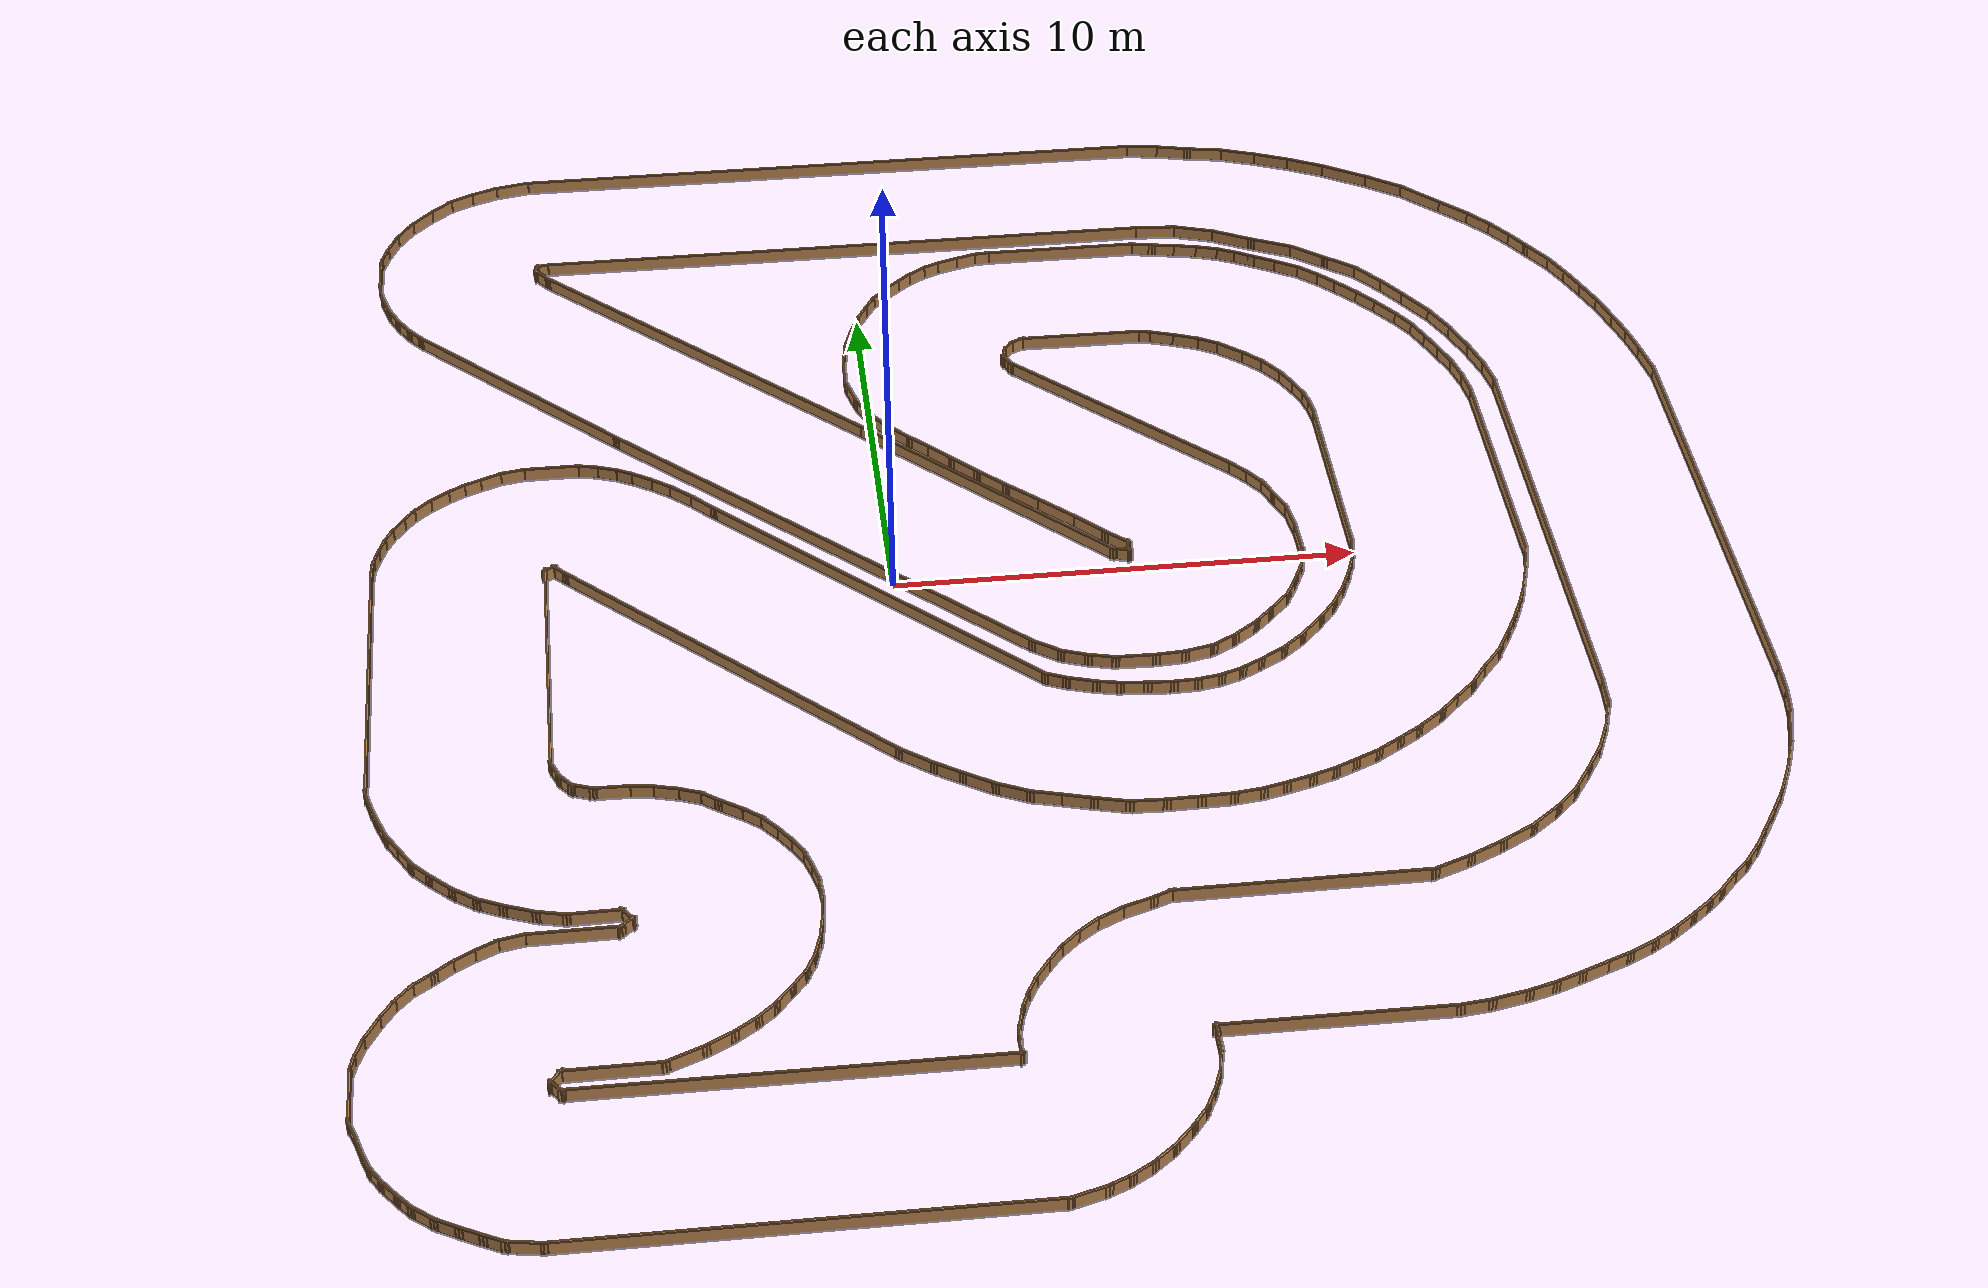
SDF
<?xml version='1.0'?>
<sdf version='1.6'>
  <model name='rover_racetrack'>
    <pose frame=''>3.369 -0.8264 0 0 -0 0</pose>
    <link name='Wall_100'>
      <collision name='Wall_100_Collision'>
        <geometry>
          <box>
            <size>0.723182 0.05 0.3</size>
          </box>
        </geometry>
        <pose frame=''>0 0 0.15 0 -0 0</pose>
      </collision>
      <visual name='Wall_100_Visual'>
        <pose frame=''>0 0 0.15 0 -0 0</pose>
        <geometry>
          <box>
            <size>0.723182 0.05 0.3</size>
          </box>
        </geometry>
        <material>
          <script>
            <uri>file://media/materials/scripts/gazebo.material</uri>
            <name>Gazebo/Wood</name>
          </script>
          <ambient>0.435294 0.796078 0.67451 1</ambient>
        </material>
      </visual>
      <pose frame=''>7.69208 -13.0933 0 0 0 -2.8578</pose>
    </link>
    <link name='Wall_101'>
      <collision name='Wall_101_Collision'>
        <geometry>
          <box>
            <size>0.912224 0.05 0.3</size>
          </box>
        </geometry>
        <pose frame=''>0 0 0.15 0 -0 0</pose>
      </collision>
      <visual name='Wall_101_Visual'>
        <pose frame=''>0 0 0.15 0 -0 0</pose>
        <geometry>
          <box>
            <size>0.912224 0.05 0.3</size>
          </box>
        </geometry>
        <material>
          <script>
            <uri>file://media/materials/scripts/gazebo.material</uri>
            <name>Gazebo/Wood</name>
          </script>
          <ambient>0.435294 0.796078 0.67451 1</ambient>
        </material>
      </visual>
      <pose frame=''>7.04439 -13.2538 0 0 0 -2.92945</pose>
    </link>
    <link name='Wall_102'>
      <collision name='Wall_102_Collision'>
        <geometry>
          <box>
            <size>0.772846 0.05 0.3</size>
          </box>
        </geometry>
        <pose frame=''>0 0 0.15 0 -0 0</pose>
      </collision>
      <visual name='Wall_102_Visual'>
        <pose frame=''>0 0 0.15 0 -0 0</pose>
        <geometry>
          <box>
            <size>0.772846 0.05 0.3</size>
          </box>
        </geometry>
        <material>
          <script>
            <uri>file://media/materials/scripts/gazebo.material</uri>
            <name>Gazebo/Wood</name>
          </script>
          <ambient>0.435294 0.796078 0.67451 1</ambient>
        </material>
      </visual>
      <pose frame=''>6.3623 -13.3684 0 0 0 -3.03093</pose>
    </link>
    <link name='Wall_103'>
      <collision name='Wall_103_Collision'>
        <geometry>
          <box>
            <size>4.76985 0.05 0.3</size>
          </box>
        </geometry>
        <pose frame=''>0 0 0.15 0 -0 0</pose>
      </collision>
      <visual name='Wall_103_Visual'>
        <pose frame=''>0 0 0.15 0 -0 0</pose>
        <geometry>
          <box>
            <size>4.76985 0.05 0.3</size>
          </box>
        </geometry>
        <material>
          <script>
            <uri>file://media/materials/scripts/gazebo.material</uri>
            <name>Gazebo/Wood</name>
          </script>
          <ambient>0.435294 0.796078 0.67451 1</ambient>
        </material>
      </visual>
      <pose frame=''>3.74286 -13.4028 0 0 -0 3.14159</pose>
    </link>
    <link name='Wall_105'>
      <collision name='Wall_105_Collision'>
        <geometry>
          <box>
            <size>0.780604 0.05 0.3</size>
          </box>
        </geometry>
        <pose frame=''>0 0 0.15 0 -0 0</pose>
      </collision>
      <visual name='Wall_105_Visual'>
        <pose frame=''>0 0 0.15 0 -0 0</pose>
        <geometry>
          <box>
            <size>0.780604 0.05 0.3</size>
          </box>
        </geometry>
        <material>
          <script>
            <uri>file://media/materials/scripts/gazebo.material</uri>
            <name>Gazebo/Wood</name>
          </script>
          <ambient>0.435294 0.796078 0.67451 1</ambient>
        </material>
      </visual>
      <pose frame=''>1.43294 -13.718 0 0 0 -1.5708</pose>
    </link>
    <link name='Wall_106'>
      <collision name='Wall_106_Collision'>
        <geometry>
          <box>
            <size>0.712069 0.05 0.3</size>
          </box>
        </geometry>
        <pose frame=''>0 0 0.15 0 -0 0</pose>
      </collision>
      <visual name='Wall_106_Visual'>
        <pose frame=''>0 0 0.15 0 -0 0</pose>
        <geometry>
          <box>
            <size>0.712069 0.05 0.3</size>
          </box>
        </geometry>
        <material>
          <script>
            <uri>file://media/materials/scripts/gazebo.material</uri>
            <name>Gazebo/Wood</name>
          </script>
          <ambient>0.435294 0.796078 0.67451 1</ambient>
        </material>
      </visual>
      <pose frame=''>1.37562 -14.3084 0 0 0 -1.77619</pose>
    </link>
    <link name='Wall_107'>
      <collision name='Wall_107_Collision'>
        <geometry>
          <box>
            <size>0.599573 0.05 0.3</size>
          </box>
        </geometry>
        <pose frame=''>0 0 0.15 0 -0 0</pose>
      </collision>
      <visual name='Wall_107_Visual'>
        <pose frame=''>0 0 0.15 0 -0 0</pose>
        <geometry>
          <box>
            <size>0.599573 0.05 0.3</size>
          </box>
        </geometry>
        <material>
          <script>
            <uri>file://media/materials/scripts/gazebo.material</uri>
            <name>Gazebo/Wood</name>
          </script>
          <ambient>0.435294 0.796078 0.67451 1</ambient>
        </material>
      </visual>
      <pose frame=''>1.24379 -14.7956 0 0 0 -1.90867</pose>
    </link>
    <link name='Wall_108'>
      <collision name='Wall_108_Collision'>
        <geometry>
          <box>
            <size>0.683275 0.05 0.3</size>
          </box>
        </geometry>
        <pose frame=''>0 0 0.15 0 -0 0</pose>
      </collision>
      <visual name='Wall_108_Visual'>
        <pose frame=''>0 0 0.15 0 -0 0</pose>
        <geometry>
          <box>
            <size>0.683275 0.05 0.3</size>
          </box>
        </geometry>
        <material>
          <script>
            <uri>file://media/materials/scripts/gazebo.material</uri>
            <name>Gazebo/Wood</name>
          </script>
          <ambient>0.435294 0.796078 0.67451 1</ambient>
        </material>
      </visual>
      <pose frame=''>1.05464 -15.2484 0 0 0 -2.01522</pose>
    </link>
    <link name='Wall_109'>
      <collision name='Wall_109_Collision'>
        <geometry>
          <box>
            <size>0.665864 0.05 0.3</size>
          </box>
        </geometry>
        <pose frame=''>0 0 0.15 0 -0 0</pose>
      </collision>
      <visual name='Wall_109_Visual'>
        <pose frame=''>0 0 0.15 0 -0 0</pose>
        <geometry>
          <box>
            <size>0.665864 0.05 0.3</size>
          </box>
        </geometry>
        <material>
          <script>
            <uri>file://media/materials/scripts/gazebo.material</uri>
            <name>Gazebo/Wood</name>
          </script>
          <ambient>0.435294 0.796078 0.67451 1</ambient>
        </material>
      </visual>
      <pose frame=''>0.78524 -15.6955 0 0 0 -2.2143</pose>
    </link>
    <link name='Wall_110'>
      <collision name='Wall_110_Collision'>
        <geometry>
          <box>
            <size>0.750721 0.05 0.3</size>
          </box>
        </geometry>
        <pose frame=''>0 0 0.15 0 -0 0</pose>
      </collision>
      <visual name='Wall_110_Visual'>
        <pose frame=''>0 0 0.15 0 -0 0</pose>
        <geometry>
          <box>
            <size>0.750721 0.05 0.3</size>
          </box>
        </geometry>
        <material>
          <script>
            <uri>file://media/materials/scripts/gazebo.material</uri>
            <name>Gazebo/Wood</name>
          </script>
          <ambient>0.435294 0.796078 0.67451 1</ambient>
        </material>
      </visual>
      <pose frame=''>0.429867 -16.1254 0 0 0 -2.30219</pose>
    </link>
    <link name='Wall_111'>
      <collision name='Wall_111_Collision'>
        <geometry>
          <box>
            <size>0.719502 0.05 0.3</size>
          </box>
        </geometry>
        <pose frame=''>0 0 0.15 0 -0 0</pose>
      </collision>
      <visual name='Wall_111_Visual'>
        <pose frame=''>0 0 0.15 0 -0 0</pose>
        <geometry>
          <box>
            <size>0.719502 0.05 0.3</size>
          </box>
        </geometry>
        <material>
          <script>
            <uri>file://media/materials/scripts/gazebo.material</uri>
            <name>Gazebo/Wood</name>
          </script>
          <ambient>0.435294 0.796078 0.67451 1</ambient>
        </material>
      </visual>
      <pose frame=''>0.011445 -16.5324 0 0 0 -2.4417</pose>
    </link>
    <link name='Wall_112'>
      <collision name='Wall_112_Collision'>
        <geometry>
          <box>
            <size>0.665226 0.05 0.3</size>
          </box>
        </geometry>
        <pose frame=''>0 0 0.15 0 -0 0</pose>
      </collision>
      <visual name='Wall_112_Visual'>
        <pose frame=''>0 0 0.15 0 -0 0</pose>
        <geometry>
          <box>
            <size>0.665226 0.05 0.3</size>
          </box>
        </geometry>
        <material>
          <script>
            <uri>file://media/materials/scripts/gazebo.material</uri>
            <name>Gazebo/Wood</name>
          </script>
          <ambient>0.435294 0.796078 0.67451 1</ambient>
        </material>
      </visual>
      <pose frame=''>-0.424174 -16.8533 0 0 0 -2.57828</pose>
    </link>
    <link name='Wall_113'>
      <collision name='Wall_113_Collision'>
        <geometry>
          <box>
            <size>0.652834 0.05 0.3</size>
          </box>
        </geometry>
        <pose frame=''>0 0 0.15 0 -0 0</pose>
      </collision>
      <visual name='Wall_113_Visual'>
        <pose frame=''>0 0 0.15 0 -0 0</pose>
        <geometry>
          <box>
            <size>0.652834 0.05 0.3</size>
          </box>
        </geometry>
        <material>
          <script>
            <uri>file://media/materials/scripts/gazebo.material</uri>
            <name>Gazebo/Wood</name>
          </script>
          <ambient>0.435294 0.796078 0.67451 1</ambient>
        </material>
      </visual>
      <pose frame=''>-0.871256 -17.0941 0 0 0 -2.71874</pose>
    </link>
    <link name='Wall_114'>
      <collision name='Wall_114_Collision'>
        <geometry>
          <box>
            <size>0.868103 0.05 0.3</size>
          </box>
        </geometry>
        <pose frame=''>0 0 0.15 0 -0 0</pose>
      </collision>
      <visual name='Wall_114_Visual'>
        <pose frame=''>0 0 0.15 0 -0 0</pose>
        <geometry>
          <box>
            <size>0.868103 0.05 0.3</size>
          </box>
        </geometry>
        <material>
          <script>
            <uri>file://media/materials/scripts/gazebo.material</uri>
            <name>Gazebo/Wood</name>
          </script>
          <ambient>0.435294 0.796078 0.67451 1</ambient>
        </material>
      </visual>
      <pose frame=''>-1.44447 -17.3004 0 0 0 -2.85032</pose>
    </link>
    <link name='Wall_116'>
      <collision name='Wall_116_Collision'>
        <geometry>
          <box>
            <size>9.45 0.05 0.3</size>
          </box>
        </geometry>
        <pose frame=''>0 0 0.15 0 -0 0</pose>
      </collision>
      <visual name='Wall_116_Visual'>
        <pose frame=''>0 0 0.15 0 -0 0</pose>
        <geometry>
          <box>
            <size>9.45 0.05 0.3</size>
          </box>
        </geometry>
        <material>
          <script>
            <uri>file://media/materials/scripts/gazebo.material</uri>
            <name>Gazebo/Wood</name>
          </script>
          <ambient>0.435294 0.796078 0.67451 1</ambient>
        </material>
      </visual>
      <pose frame=''>-6.46341 -17.4035 0 0 -0 3.14159</pose>
    </link>
    <link name='Wall_117'>
      <collision name='Wall_117_Collision'>
        <geometry>
          <box>
            <size>0.828968 0.05 0.3</size>
          </box>
        </geometry>
        <pose frame=''>0 0 0.15 0 -0 0</pose>
      </collision>
      <visual name='Wall_117_Visual'>
        <pose frame=''>0 0 0.15 0 -0 0</pose>
        <geometry>
          <box>
            <size>0.828968 0.05 0.3</size>
          </box>
        </geometry>
        <material>
          <script>
            <uri>file://media/materials/scripts/gazebo.material</uri>
            <name>Gazebo/Wood</name>
          </script>
          <ambient>0.435294 0.796078 0.67451 1</ambient>
        </material>
      </visual>
      <pose frame=''>-11.473 -17.3462 0 0 -0 2.9721</pose>
    </link>
    <link name='Wall_118'>
      <collision name='Wall_118_Collision'>
        <geometry>
          <box>
            <size>0.575547 0.05 0.3</size>
          </box>
        </geometry>
        <pose frame=''>0 0 0.15 0 -0 0</pose>
      </collision>
      <visual name='Wall_118_Visual'>
        <pose frame=''>0 0 0.15 0 -0 0</pose>
        <geometry>
          <box>
            <size>0.575547 0.05 0.3</size>
          </box>
        </geometry>
        <material>
          <script>
            <uri>file://media/materials/scripts/gazebo.material</uri>
            <name>Gazebo/Wood</name>
          </script>
          <ambient>0.435294 0.796078 0.67451 1</ambient>
        </material>
      </visual>
      <pose frame=''>-11.9967 -17.1915 0 0 -0 2.6659</pose>
    </link>
    <link name='Wall_119'>
      <collision name='Wall_119_Collision'>
        <geometry>
          <box>
            <size>0.632155 0.05 0.3</size>
          </box>
        </geometry>
        <pose frame=''>0 0 0.15 0 -0 0</pose>
      </collision>
      <visual name='Wall_119_Visual'>
        <pose frame=''>0 0 0.15 0 -0 0</pose>
        <geometry>
          <box>
            <size>0.632155 0.05 0.3</size>
          </box>
        </geometry>
        <material>
          <script>
            <uri>file://media/materials/scripts/gazebo.material</uri>
            <name>Gazebo/Wood</name>
          </script>
          <ambient>0.435294 0.796078 0.67451 1</ambient>
        </material>
      </visual>
      <pose frame=''>-12.3979 -16.9794 0 0 -0 2.64604</pose>
    </link>
    <link name='Wall_120'>
      <collision name='Wall_120_Collision'>
        <geometry>
          <box>
            <size>0.653357 0.05 0.3</size>
          </box>
        </geometry>
        <pose frame=''>0 0 0.15 0 -0 0</pose>
      </collision>
      <visual name='Wall_120_Visual'>
        <pose frame=''>0 0 0.15 0 -0 0</pose>
        <geometry>
          <box>
            <size>0.653357 0.05 0.3</size>
          </box>
        </geometry>
        <material>
          <script>
            <uri>file://media/materials/scripts/gazebo.material</uri>
            <name>Gazebo/Wood</name>
          </script>
          <ambient>0.435294 0.796078 0.67451 1</ambient>
        </material>
      </visual>
      <pose frame=''>-12.8278 -16.7387 0 0 -0 2.6168</pose>
    </link>
    <link name='Wall_121'>
      <collision name='Wall_121_Collision'>
        <geometry>
          <box>
            <size>0.67106 0.05 0.3</size>
          </box>
        </geometry>
        <pose frame=''>0 0 0.15 0 -0 0</pose>
      </collision>
      <visual name='Wall_121_Visual'>
        <pose frame=''>0 0 0.15 0 -0 0</pose>
        <geometry>
          <box>
            <size>0.67106 0.05 0.3</size>
          </box>
        </geometry>
        <material>
          <script>
            <uri>file://media/materials/scripts/gazebo.material</uri>
            <name>Gazebo/Wood</name>
          </script>
          <ambient>0.435294 0.796078 0.67451 1</ambient>
        </material>
      </visual>
      <pose frame=''>-13.2463 -16.4464 0 0 -0 2.44967</pose>
    </link>
    <link name='Wall_122'>
      <collision name='Wall_122_Collision'>
        <geometry>
          <box>
            <size>0.540437 0.05 0.3</size>
          </box>
        </geometry>
        <pose frame=''>0 0 0.15 0 -0 0</pose>
      </collision>
      <visual name='Wall_122_Visual'>
        <pose frame=''>0 0 0.15 0 -0 0</pose>
        <geometry>
          <box>
            <size>0.540437 0.05 0.3</size>
          </box>
        </geometry>
        <material>
          <script>
            <uri>file://media/materials/scripts/gazebo.material</uri>
            <name>Gazebo/Wood</name>
          </script>
          <ambient>0.435294 0.796078 0.67451 1</ambient>
        </material>
      </visual>
      <pose frame=''>-13.573 -16.1311 0 0 -0 2.27305</pose>
    </link>
    <link name='Wall_124'>
      <collision name='Wall_124_Collision'>
        <geometry>
          <box>
            <size>0.6246 0.05 0.3</size>
          </box>
        </geometry>
        <pose frame=''>0 0 0.15 0 -0 0</pose>
      </collision>
      <visual name='Wall_124_Visual'>
        <pose frame=''>0 0 0.15 0 -0 0</pose>
        <geometry>
          <box>
            <size>0.6246 0.05 0.3</size>
          </box>
        </geometry>
        <material>
          <script>
            <uri>file://media/materials/scripts/gazebo.material</uri>
            <name>Gazebo/Wood</name>
          </script>
          <ambient>0.435294 0.796078 0.67451 1</ambient>
        </material>
      </visual>
      <pose frame=''>-13.8424 -15.7929 0 0 -0 2.21913</pose>
    </link>
    <link name='Wall_125'>
      <collision name='Wall_125_Collision'>
        <geometry>
          <box>
            <size>0.592354 0.05 0.3</size>
          </box>
        </geometry>
        <pose frame=''>0 0 0.15 0 -0 0</pose>
      </collision>
      <visual name='Wall_125_Visual'>
        <pose frame=''>0 0 0.15 0 -0 0</pose>
        <geometry>
          <box>
            <size>0.592354 0.05 0.3</size>
          </box>
        </geometry>
        <material>
          <script>
            <uri>file://media/materials/scripts/gazebo.material</uri>
            <name>Gazebo/Wood</name>
          </script>
          <ambient>0.435294 0.796078 0.67451 1</ambient>
        </material>
      </visual>
      <pose frame=''>-14.1003 -15.4146 0 0 -0 2.11566</pose>
    </link>
    <link name='Wall_126'>
      <collision name='Wall_126_Collision'>
        <geometry>
          <box>
            <size>0.610405 0.05 0.3</size>
          </box>
        </geometry>
        <pose frame=''>0 0 0.15 0 -0 0</pose>
      </collision>
      <visual name='Wall_126_Visual'>
        <pose frame=''>0 0 0.15 0 -0 0</pose>
        <geometry>
          <box>
            <size>0.610405 0.05 0.3</size>
          </box>
        </geometry>
        <material>
          <script>
            <uri>file://media/materials/scripts/gazebo.material</uri>
            <name>Gazebo/Wood</name>
          </script>
          <ambient>0.435294 0.796078 0.67451 1</ambient>
        </material>
      </visual>
      <pose frame=''>-14.2894 -15.0077 0 0 -0 1.90042</pose>
    </link>
    <link name='Wall_127'>
      <collision name='Wall_127_Collision'>
        <geometry>
          <box>
            <size>0.520047 0.05 0.3</size>
          </box>
        </geometry>
        <pose frame=''>0 0 0.15 0 -0 0</pose>
      </collision>
      <visual name='Wall_127_Visual'>
        <pose frame=''>0 0 0.15 0 -0 0</pose>
        <geometry>
          <box>
            <size>0.520047 0.05 0.3</size>
          </box>
        </geometry>
        <material>
          <script>
            <uri>file://media/materials/scripts/gazebo.material</uri>
            <name>Gazebo/Wood</name>
          </script>
          <ambient>0.435294 0.796078 0.67451 1</ambient>
        </material>
      </visual>
      <pose frame=''>-14.4155 -14.6122 0 0 -0 1.85335</pose>
    </link>
    <link name='Wall_128'>
      <collision name='Wall_128_Collision'>
        <geometry>
          <box>
            <size>0.574155 0.05 0.3</size>
          </box>
        </geometry>
        <pose frame=''>0 0 0.15 0 -0 0</pose>
      </collision>
      <visual name='Wall_128_Visual'>
        <pose frame=''>0 0 0.15 0 -0 0</pose>
        <geometry>
          <box>
            <size>0.574155 0.05 0.3</size>
          </box>
        </geometry>
        <material>
          <script>
            <uri>file://media/materials/scripts/gazebo.material</uri>
            <name>Gazebo/Wood</name>
          </script>
          <ambient>0.435294 0.796078 0.67451 1</ambient>
        </material>
      </visual>
      <pose frame=''>-14.5359 -14.2339 0 0 -0 1.90109</pose>
    </link>
    <link name='Wall_129'>
      <collision name='Wall_129_Collision'>
        <geometry>
          <box>
            <size>1.46832 0.05 0.3</size>
          </box>
        </geometry>
        <pose frame=''>0 0 0.15 0 -0 0</pose>
      </collision>
      <visual name='Wall_129_Visual'>
        <pose frame=''>0 0 0.15 0 -0 0</pose>
        <geometry>
          <box>
            <size>1.46832 0.05 0.3</size>
          </box>
        </geometry>
        <material>
          <script>
            <uri>file://media/materials/scripts/gazebo.material</uri>
            <name>Gazebo/Wood</name>
          </script>
          <ambient>0.435294 0.796078 0.67451 1</ambient>
        </material>
      </visual>
      <pose frame=''>-14.6047 -13.3741 0 0 -0 1.5708</pose>
    </link>
    <link name='Wall_130'>
      <collision name='Wall_130_Collision'>
        <geometry>
          <box>
            <size>0.455888 0.05 0.3</size>
          </box>
        </geometry>
        <pose frame=''>0 0 0.15 0 -0 0</pose>
      </collision>
      <visual name='Wall_130_Visual'>
        <pose frame=''>0 0 0.15 0 -0 0</pose>
        <geometry>
          <box>
            <size>0.455888 0.05 0.3</size>
          </box>
        </geometry>
        <material>
          <script>
            <uri>file://media/materials/scripts/gazebo.material</uri>
            <name>Gazebo/Wood</name>
          </script>
          <ambient>0.435294 0.796078 0.67451 1</ambient>
        </material>
      </visual>
      <pose frame=''>-14.5703 -12.5659 0 0 -0 1.344</pose>
    </link>
    <link name='Wall_131'>
      <collision name='Wall_131_Collision'>
        <geometry>
          <box>
            <size>0.614242 0.05 0.3</size>
          </box>
        </geometry>
        <pose frame=''>0 0 0.15 0 -0 0</pose>
      </collision>
      <visual name='Wall_131_Visual'>
        <pose frame=''>0 0 0.15 0 -0 0</pose>
        <geometry>
          <box>
            <size>0.614242 0.05 0.3</size>
          </box>
        </geometry>
        <material>
          <script>
            <uri>file://media/materials/scripts/gazebo.material</uri>
            <name>Gazebo/Wood</name>
          </script>
          <ambient>0.435294 0.796078 0.67451 1</ambient>
        </material>
      </visual>
      <pose frame=''>-14.4557 -12.1991 0 0 -0 1.21781</pose>
    </link>
    <link name='Wall_133'>
      <collision name='Wall_133_Collision'>
        <geometry>
          <box>
            <size>0.760271 0.05 0.3</size>
          </box>
        </geometry>
        <pose frame=''>0 0 0.15 0 -0 0</pose>
      </collision>
      <visual name='Wall_133_Visual'>
        <pose frame=''>0 0 0.15 0 -0 0</pose>
        <geometry>
          <box>
            <size>0.760271 0.05 0.3</size>
          </box>
        </geometry>
        <material>
          <script>
            <uri>file://media/materials/scripts/gazebo.material</uri>
            <name>Gazebo/Wood</name>
          </script>
          <ambient>0.435294 0.796078 0.67451 1</ambient>
        </material>
      </visual>
      <pose frame=''>-14.2321 -11.7119 0 0 -0 1.08194</pose>
    </link>
    <link name='Wall_134'>
      <collision name='Wall_134_Collision'>
        <geometry>
          <box>
            <size>0.681052 0.05 0.3</size>
          </box>
        </geometry>
        <pose frame=''>0 0 0.15 0 -0 0</pose>
      </collision>
      <visual name='Wall_134_Visual'>
        <pose frame=''>0 0 0.15 0 -0 0</pose>
        <geometry>
          <box>
            <size>0.681052 0.05 0.3</size>
          </box>
        </geometry>
        <material>
          <script>
            <uri>file://media/materials/scripts/gazebo.material</uri>
            <name>Gazebo/Wood</name>
          </script>
          <ambient>0.435294 0.796078 0.67451 1</ambient>
        </material>
      </visual>
      <pose frame=''>-13.9455 -11.219 0 0 -0 1.00076</pose>
    </link>
    <link name='Wall_135'>
      <collision name='Wall_135_Collision'>
        <geometry>
          <box>
            <size>0.637441 0.05 0.3</size>
          </box>
        </geometry>
        <pose frame=''>0 0 0.15 0 -0 0</pose>
      </collision>
      <visual name='Wall_135_Visual'>
        <pose frame=''>0 0 0.15 0 -0 0</pose>
        <geometry>
          <box>
            <size>0.637441 0.05 0.3</size>
          </box>
        </geometry>
        <material>
          <script>
            <uri>file://media/materials/scripts/gazebo.material</uri>
            <name>Gazebo/Wood</name>
          </script>
          <ambient>0.435294 0.796078 0.67451 1</ambient>
        </material>
      </visual>
      <pose frame=''>-13.6417 -10.812 0 0 -0 0.851966</pose>
    </link>
    <link name='Wall_136'>
      <collision name='Wall_136_Collision'>
        <geometry>
          <box>
            <size>0.633787 0.05 0.3</size>
          </box>
        </geometry>
        <pose frame=''>0 0 0.15 0 -0 0</pose>
      </collision>
      <visual name='Wall_136_Visual'>
        <pose frame=''>0 0 0.15 0 -0 0</pose>
        <geometry>
          <box>
            <size>0.633787 0.05 0.3</size>
          </box>
        </geometry>
        <material>
          <script>
            <uri>file://media/materials/scripts/gazebo.material</uri>
            <name>Gazebo/Wood</name>
          </script>
          <ambient>0.435294 0.796078 0.67451 1</ambient>
        </material>
      </visual>
      <pose frame=''>-13.2864 -10.4853 0 0 -0 0.634023</pose>
    </link>
    <link name='Wall_137'>
      <collision name='Wall_137_Collision'>
        <geometry>
          <box>
            <size>0.615514 0.05 0.3</size>
          </box>
        </geometry>
        <pose frame=''>0 0 0.15 0 -0 0</pose>
      </collision>
      <visual name='Wall_137_Visual'>
        <pose frame=''>0 0 0.15 0 -0 0</pose>
        <geometry>
          <box>
            <size>0.615514 0.05 0.3</size>
          </box>
        </geometry>
        <material>
          <script>
            <uri>file://media/materials/scripts/gazebo.material</uri>
            <name>Gazebo/Wood</name>
          </script>
          <ambient>0.435294 0.796078 0.67451 1</ambient>
        </material>
      </visual>
      <pose frame=''>-12.9081 -10.1987 0 0 -0 0.663203</pose>
    </link>
    <link name='Wall_138'>
      <collision name='Wall_138_Collision'>
        <geometry>
          <box>
            <size>0.633651 0.05 0.3</size>
          </box>
        </geometry>
        <pose frame=''>0 0 0.15 0 -0 0</pose>
      </collision>
      <visual name='Wall_138_Visual'>
        <pose frame=''>0 0 0.15 0 -0 0</pose>
        <geometry>
          <box>
            <size>0.633651 0.05 0.3</size>
          </box>
        </geometry>
        <material>
          <script>
            <uri>file://media/materials/scripts/gazebo.material</uri>
            <name>Gazebo/Wood</name>
          </script>
          <ambient>0.435294 0.796078 0.67451 1</ambient>
        </material>
      </visual>
      <pose frame=''>-12.5183 -9.9293 0 0 -0 0.548549</pose>
    </link>
    <link name='Wall_139'>
      <collision name='Wall_139_Collision'>
        <geometry>
          <box>
            <size>0.652442 0.05 0.3</size>
          </box>
        </geometry>
        <pose frame=''>0 0 0.15 0 -0 0</pose>
      </collision>
      <visual name='Wall_139_Visual'>
        <pose frame=''>0 0 0.15 0 -0 0</pose>
        <geometry>
          <box>
            <size>0.652442 0.05 0.3</size>
          </box>
        </geometry>
        <material>
          <script>
            <uri>file://media/materials/scripts/gazebo.material</uri>
            <name>Gazebo/Wood</name>
          </script>
          <ambient>0.435294 0.796078 0.67451 1</ambient>
        </material>
      </visual>
      <pose frame=''>-12.0884 -9.68856 0 0 -0 0.473851</pose>
    </link>
    <link name='Wall_140'>
      <collision name='Wall_140_Collision'>
        <geometry>
          <box>
            <size>0.678448 0.05 0.3</size>
          </box>
        </geometry>
        <pose frame=''>0 0 0.15 0 -0 0</pose>
      </collision>
      <visual name='Wall_140_Visual'>
        <pose frame=''>0 0 0.15 0 -0 0</pose>
        <geometry>
          <box>
            <size>0.678448 0.05 0.3</size>
          </box>
        </geometry>
        <material>
          <script>
            <uri>file://media/materials/scripts/gazebo.material</uri>
            <name>Gazebo/Wood</name>
          </script>
          <ambient>0.435294 0.796078 0.67451 1</ambient>
        </material>
      </visual>
      <pose frame=''>-11.607 -9.51661 0 0 -0 0.218669</pose>
    </link>
    <link name='Wall_141'>
      <collision name='Wall_141_Collision'>
        <geometry>
          <box>
            <size>1.98422 0.05 0.3</size>
          </box>
        </geometry>
        <pose frame=''>0 0 0.15 0 -0 0</pose>
      </collision>
      <visual name='Wall_141_Visual'>
        <pose frame=''>0 0 0.15 0 -0 0</pose>
        <geometry>
          <box>
            <size>1.98422 0.05 0.3</size>
          </box>
        </geometry>
        <material>
          <script>
            <uri>file://media/materials/scripts/gazebo.material</uri>
            <name>Gazebo/Wood</name>
          </script>
          <ambient>0.435294 0.796078 0.67451 1</ambient>
        </material>
      </visual>
      <pose frame=''>-10.4319 -9.45356 0 0 -0 0.00625</pose>
    </link>
    <link name='Wall_142'>
      <collision name='Wall_142_Collision'>
        <geometry>
          <box>
            <size>0.458455 0.05 0.3</size>
          </box>
        </geometry>
        <pose frame=''>0 0 0.15 0 -0 0</pose>
      </collision>
      <visual name='Wall_142_Visual'>
        <pose frame=''>0 0 0.15 0 -0 0</pose>
        <geometry>
          <box>
            <size>0.458455 0.05 0.3</size>
          </box>
        </geometry>
        <material>
          <script>
            <uri>file://media/materials/scripts/gazebo.material</uri>
            <name>Gazebo/Wood</name>
          </script>
          <ambient>0.435294 0.796078 0.67451 1</ambient>
        </material>
      </visual>
      <pose frame=''>-9.4002 -9.34465 0 0 -0 0.732815</pose>
    </link>
    <link name='Wall_143'>
      <collision name='Wall_143_Collision'>
        <geometry>
          <box>
            <size>0.477868 0.05 0.3</size>
          </box>
        </geometry>
        <pose frame=''>0 0 0.15 0 -0 0</pose>
      </collision>
      <visual name='Wall_143_Visual'>
        <pose frame=''>0 0 0.15 0 -0 0</pose>
        <geometry>
          <box>
            <size>0.477868 0.05 0.3</size>
          </box>
        </geometry>
        <material>
          <script>
            <uri>file://media/materials/scripts/gazebo.material</uri>
            <name>Gazebo/Wood</name>
          </script>
          <ambient>0.435294 0.796078 0.67451 1</ambient>
        </material>
      </visual>
      <pose frame=''>-9.38301 -9.10965 0 0 -0 2.2073</pose>
    </link>
    <link name='Wall_144'>
      <collision name='Wall_144_Collision'>
        <geometry>
          <box>
            <size>1.22783 0.05 0.3</size>
          </box>
        </geometry>
        <pose frame=''>0 0 0.15 0 -0 0</pose>
      </collision>
      <visual name='Wall_144_Visual'>
        <pose frame=''>0 0 0.15 0 -0 0</pose>
        <geometry>
          <box>
            <size>1.22783 0.05 0.3</size>
          </box>
        </geometry>
        <material>
          <script>
            <uri>file://media/materials/scripts/gazebo.material</uri>
            <name>Gazebo/Wood</name>
          </script>
          <ambient>0.435294 0.796078 0.67451 1</ambient>
        </material>
      </visual>
      <pose frame=''>-10.0192 -8.98355 0 0 0 -3.13096</pose>
    </link>
    <link name='Wall_145'>
      <collision name='Wall_145_Collision'>
        <geometry>
          <box>
            <size>0.739458 0.05 0.3</size>
          </box>
        </geometry>
        <pose frame=''>0 0 0.15 0 -0 0</pose>
      </collision>
      <visual name='Wall_145_Visual'>
        <pose frame=''>0 0 0.15 0 -0 0</pose>
        <geometry>
          <box>
            <size>0.739458 0.05 0.3</size>
          </box>
        </geometry>
        <material>
          <script>
            <uri>file://media/materials/scripts/gazebo.material</uri>
            <name>Gazebo/Wood</name>
          </script>
          <ambient>0.435294 0.796078 0.67451 1</ambient>
        </material>
      </visual>
      <pose frame=''>-10.8446 -8.9205 0 0 -0 2.90605</pose>
    </link>
    <link name='Wall_146'>
      <collision name='Wall_146_Collision'>
        <geometry>
          <box>
            <size>0.829069 0.05 0.3</size>
          </box>
        </geometry>
        <pose frame=''>0 0 0.15 0 -0 0</pose>
      </collision>
      <visual name='Wall_146_Visual'>
        <pose frame=''>0 0 0.15 0 -0 0</pose>
        <geometry>
          <box>
            <size>0.829069 0.05 0.3</size>
          </box>
        </geometry>
        <material>
          <script>
            <uri>file://media/materials/scripts/gazebo.material</uri>
            <name>Gazebo/Wood</name>
          </script>
          <ambient>0.435294 0.796078 0.67451 1</ambient>
        </material>
      </visual>
      <pose frame=''>-11.4465 -8.72562 0 0 -0 2.76109</pose>
    </link>
    <link name='Wall_148'>
      <collision name='Wall_148_Collision'>
        <geometry>
          <box>
            <size>0.708904 0.05 0.3</size>
          </box>
        </geometry>
        <pose frame=''>0 0 0.15 0 -0 0</pose>
      </collision>
      <visual name='Wall_148_Visual'>
        <pose frame=''>0 0 0.15 0 -0 0</pose>
        <geometry>
          <box>
            <size>0.708904 0.05 0.3</size>
          </box>
        </geometry>
        <material>
          <script>
            <uri>file://media/materials/scripts/gazebo.material</uri>
            <name>Gazebo/Wood</name>
          </script>
          <ambient>0.435294 0.796078 0.67451 1</ambient>
        </material>
      </visual>
      <pose frame=''>-12.0139 -8.47915 0 0 -0 2.69629</pose>
    </link>
    <link name='Wall_149'>
      <collision name='Wall_149_Collision'>
        <geometry>
          <box>
            <size>0.732393 0.05 0.3</size>
          </box>
        </geometry>
        <pose frame=''>0 0 0.15 0 -0 0</pose>
      </collision>
      <visual name='Wall_149_Visual'>
        <pose frame=''>0 0 0.15 0 -0 0</pose>
        <geometry>
          <box>
            <size>0.732393 0.05 0.3</size>
          </box>
        </geometry>
        <material>
          <script>
            <uri>file://media/materials/scripts/gazebo.material</uri>
            <name>Gazebo/Wood</name>
          </script>
          <ambient>0.435294 0.796078 0.67451 1</ambient>
        </material>
      </visual>
      <pose frame=''>-12.5011 -8.18683 0 0 -0 2.5099</pose>
    </link>
    <link name='Wall_150'>
      <collision name='Wall_150_Collision'>
        <geometry>
          <box>
            <size>0.774216 0.05 0.3</size>
          </box>
        </geometry>
        <pose frame=''>0 0 0.15 0 -0 0</pose>
      </collision>
      <visual name='Wall_150_Visual'>
        <pose frame=''>0 0 0.15 0 -0 0</pose>
        <geometry>
          <box>
            <size>0.774216 0.05 0.3</size>
          </box>
        </geometry>
        <material>
          <script>
            <uri>file://media/materials/scripts/gazebo.material</uri>
            <name>Gazebo/Wood</name>
          </script>
          <ambient>0.435294 0.796078 0.67451 1</ambient>
        </material>
      </visual>
      <pose frame=''>-12.9597 -7.79706 0 0 -0 2.36918</pose>
    </link>
    <link name='Wall_151'>
      <collision name='Wall_151_Collision'>
        <geometry>
          <box>
            <size>0.677452 0.05 0.3</size>
          </box>
        </geometry>
        <pose frame=''>0 0 0.15 0 -0 0</pose>
      </collision>
      <visual name='Wall_151_Visual'>
        <pose frame=''>0 0 0.15 0 -0 0</pose>
        <geometry>
          <box>
            <size>0.677452 0.05 0.3</size>
          </box>
        </geometry>
        <material>
          <script>
            <uri>file://media/materials/scripts/gazebo.material</uri>
            <name>Gazebo/Wood</name>
          </script>
          <ambient>0.435294 0.796078 0.67451 1</ambient>
        </material>
      </visual>
      <pose frame=''>-13.3609 -7.38437 0 0 -0 2.31007</pose>
    </link>
    <link name='Wall_152'>
      <collision name='Wall_152_Collision'>
        <geometry>
          <box>
            <size>0.66331 0.05 0.3</size>
          </box>
        </geometry>
        <pose frame=''>0 0 0.15 0 -0 0</pose>
      </collision>
      <visual name='Wall_152_Visual'>
        <pose frame=''>0 0 0.15 0 -0 0</pose>
        <geometry>
          <box>
            <size>0.66331 0.05 0.3</size>
          </box>
        </geometry>
        <material>
          <script>
            <uri>file://media/materials/scripts/gazebo.material</uri>
            <name>Gazebo/Wood</name>
          </script>
          <ambient>0.435294 0.796078 0.67451 1</ambient>
        </material>
      </visual>
      <pose frame=''>-13.6647 -6.96595 0 0 -0 2.0844</pose>
    </link>
    <link name='Wall_153'>
      <collision name='Wall_153_Collision'>
        <geometry>
          <box>
            <size>0.627774 0.05 0.3</size>
          </box>
        </geometry>
        <pose frame=''>0 0 0.15 0 -0 0</pose>
      </collision>
      <visual name='Wall_153_Visual'>
        <pose frame=''>0 0 0.15 0 -0 0</pose>
        <geometry>
          <box>
            <size>0.627774 0.05 0.3</size>
          </box>
        </geometry>
        <material>
          <script>
            <uri>file://media/materials/scripts/gazebo.material</uri>
            <name>Gazebo/Wood</name>
          </script>
          <ambient>0.435294 0.796078 0.67451 1</ambient>
        </material>
      </visual>
      <pose frame=''>-13.9111 -6.53606 0 0 -0 2.09887</pose>
    </link>
    <link name='Wall_154'>
      <collision name='Wall_154_Collision'>
        <geometry>
          <box>
            <size>0.675955 0.05 0.3</size>
          </box>
        </geometry>
        <pose frame=''>0 0 0.15 0 -0 0</pose>
      </collision>
      <visual name='Wall_154_Visual'>
        <pose frame=''>0 0 0.15 0 -0 0</pose>
        <geometry>
          <box>
            <size>0.675955 0.05 0.3</size>
          </box>
        </geometry>
        <material>
          <script>
            <uri>file://media/materials/scripts/gazebo.material</uri>
            <name>Gazebo/Wood</name>
          </script>
          <ambient>0.435294 0.796078 0.67451 1</ambient>
        </material>
      </visual>
      <pose frame=''>-14.1232 -6.08325 0 0 -0 1.92702</pose>
    </link>
    <link name='Wall_155'>
      <collision name='Wall_155_Collision'>
        <geometry>
          <box>
            <size>0.606823 0.05 0.3</size>
          </box>
        </geometry>
        <pose frame=''>0 0 0.15 0 -0 0</pose>
      </collision>
      <visual name='Wall_155_Visual'>
        <pose frame=''>0 0 0.15 0 -0 0</pose>
        <geometry>
          <box>
            <size>0.606823 0.05 0.3</size>
          </box>
        </geometry>
        <material>
          <script>
            <uri>file://media/materials/scripts/gazebo.material</uri>
            <name>Gazebo/Wood</name>
          </script>
          <ambient>0.435294 0.796078 0.67451 1</ambient>
        </material>
      </visual>
      <pose frame=''>-14.2837 -5.61897 0 0 -0 1.87668</pose>
    </link>
    <link name='Wall_156'>
      <collision name='Wall_156_Collision'>
        <geometry>
          <box>
            <size>0.622658 0.05 0.3</size>
          </box>
        </geometry>
        <pose frame=''>0 0 0.15 0 -0 0</pose>
      </collision>
      <visual name='Wall_156_Visual'>
        <pose frame=''>0 0 0.15 0 -0 0</pose>
        <geometry>
          <box>
            <size>0.622658 0.05 0.3</size>
          </box>
        </geometry>
        <material>
          <script>
            <uri>file://media/materials/scripts/gazebo.material</uri>
            <name>Gazebo/Wood</name>
          </script>
          <ambient>0.435294 0.796078 0.67451 1</ambient>
        </material>
      </visual>
      <pose frame=''>-14.4098 -5.17189 0 0 -0 1.81577</pose>
    </link>
    <link name='Wall_158'>
      <collision name='Wall_158_Collision'>
        <geometry>
          <box>
            <size>7.25 0.05 0.3</size>
          </box>
        </geometry>
        <pose frame=''>0 0 0.15 0 -0 0</pose>
      </collision>
      <visual name='Wall_158_Visual'>
        <pose frame=''>0 0 0.15 0 -0 0</pose>
        <geometry>
          <box>
            <size>7.25 0.05 0.3</size>
          </box>
        </geometry>
        <material>
          <script>
            <uri>file://media/materials/scripts/gazebo.material</uri>
            <name>Gazebo/Wood</name>
          </script>
          <ambient>0.435294 0.796078 0.67451 1</ambient>
        </material>
      </visual>
      <pose frame=''>-14.4671 -1.39261 0 0 -0 1.5708</pose>
    </link>
    <link name='Wall_160'>
      <collision name='Wall_160_Collision'>
        <geometry>
          <box>
            <size>0.535083 0.05 0.3</size>
          </box>
        </geometry>
        <pose frame=''>0 0 0.15 0 -0 0</pose>
      </collision>
      <visual name='Wall_160_Visual'>
        <pose frame=''>0 0 0.15 0 -0 0</pose>
        <geometry>
          <box>
            <size>0.535083 0.05 0.3</size>
          </box>
        </geometry>
        <material>
          <script>
            <uri>file://media/materials/scripts/gazebo.material</uri>
            <name>Gazebo/Wood</name>
          </script>
          <ambient>0.435294 0.796078 0.67451 1</ambient>
        </material>
      </visual>
      <pose frame=''>-14.4492 2.34909 0 0 -0 1.47761</pose>
    </link>
    <link name='Wall_161'>
      <collision name='Wall_161_Collision'>
        <geometry>
          <box>
            <size>0.532063 0.05 0.3</size>
          </box>
        </geometry>
        <pose frame=''>0 0 0.15 0 -0 0</pose>
      </collision>
      <visual name='Wall_161_Visual'>
        <pose frame=''>0 0 0.15 0 -0 0</pose>
        <geometry>
          <box>
            <size>0.532063 0.05 0.3</size>
          </box>
        </geometry>
        <material>
          <script>
            <uri>file://media/materials/scripts/gazebo.material</uri>
            <name>Gazebo/Wood</name>
          </script>
          <ambient>0.435294 0.796078 0.67451 1</ambient>
        </material>
      </visual>
      <pose frame=''>-14.3815 2.72521 0 0 -0 1.30683</pose>
    </link>
    <link name='Wall_162'>
      <collision name='Wall_162_Collision'>
        <geometry>
          <box>
            <size>0.572452 0.05 0.3</size>
          </box>
        </geometry>
        <pose frame=''>0 0 0.15 0 -0 0</pose>
      </collision>
      <visual name='Wall_162_Visual'>
        <pose frame=''>0 0 0.15 0 -0 0</pose>
        <geometry>
          <box>
            <size>0.572452 0.05 0.3</size>
          </box>
        </geometry>
        <material>
          <script>
            <uri>file://media/materials/scripts/gazebo.material</uri>
            <name>Gazebo/Wood</name>
          </script>
          <ambient>0.435294 0.796078 0.67451 1</ambient>
        </material>
      </visual>
      <pose frame=''>-14.2618 3.109 0 0 -0 1.23412</pose>
    </link>
    <link name='Wall_163'>
      <collision name='Wall_163_Collision'>
        <geometry>
          <box>
            <size>0.50664 0.05 0.3</size>
          </box>
        </geometry>
        <pose frame=''>0 0 0.15 0 -0 0</pose>
      </collision>
      <visual name='Wall_163_Visual'>
        <pose frame=''>0 0 0.15 0 -0 0</pose>
        <geometry>
          <box>
            <size>0.50664 0.05 0.3</size>
          </box>
        </geometry>
        <material>
          <script>
            <uri>file://media/materials/scripts/gazebo.material</uri>
            <name>Gazebo/Wood</name>
          </script>
          <ambient>0.435294 0.796078 0.67451 1</ambient>
        </material>
      </visual>
      <pose frame=''>-14.1123 3.46786 0 0 -0 1.10715</pose>
    </link>
    <link name='Wall_164'>
      <collision name='Wall_164_Collision'>
        <geometry>
          <box>
            <size>0.589627 0.05 0.3</size>
          </box>
        </geometry>
        <pose frame=''>0 0 0.15 0 -0 0</pose>
      </collision>
      <visual name='Wall_164_Visual'>
        <pose frame=''>0 0 0.15 0 -0 0</pose>
        <geometry>
          <box>
            <size>0.589627 0.05 0.3</size>
          </box>
        </geometry>
        <material>
          <script>
            <uri>file://media/materials/scripts/gazebo.material</uri>
            <name>Gazebo/Wood</name>
          </script>
          <ambient>0.435294 0.796078 0.67451 1</ambient>
        </material>
      </visual>
      <pose frame=''>-13.9129 3.81177 0 0 -0 0.995372</pose>
    </link>
    <link name='Wall_165'>
      <collision name='Wall_165_Collision'>
        <geometry>
          <box>
            <size>0.520845 0.05 0.3</size>
          </box>
        </geometry>
        <pose frame=''>0 0 0.15 0 -0 0</pose>
      </collision>
      <visual name='Wall_165_Visual'>
        <pose frame=''>0 0 0.15 0 -0 0</pose>
        <geometry>
          <box>
            <size>0.520845 0.05 0.3</size>
          </box>
        </geometry>
        <material>
          <script>
            <uri>file://media/materials/scripts/gazebo.material</uri>
            <name>Gazebo/Wood</name>
          </script>
          <ambient>0.435294 0.796078 0.67451 1</ambient>
        </material>
      </visual>
      <pose frame=''>-13.6837 4.14571 0 0 -0 0.938048</pose>
    </link>
    <link name='Wall_166'>
      <collision name='Wall_166_Collision'>
        <geometry>
          <box>
            <size>0.636412 0.05 0.3</size>
          </box>
        </geometry>
        <pose frame=''>0 0 0.15 0 -0 0</pose>
      </collision>
      <visual name='Wall_166_Visual'>
        <pose frame=''>0 0 0.15 0 -0 0</pose>
        <geometry>
          <box>
            <size>0.636412 0.05 0.3</size>
          </box>
        </geometry>
        <material>
          <script>
            <uri>file://media/materials/scripts/gazebo.material</uri>
            <name>Gazebo/Wood</name>
          </script>
          <ambient>0.435294 0.796078 0.67451 1</ambient>
        </material>
      </visual>
      <pose frame=''>-13.3996 4.46469 0 0 -0 0.770906</pose>
    </link>
    <link name='Wall_167'>
      <collision name='Wall_167_Collision'>
        <geometry>
          <box>
            <size>0.628586 0.05 0.3</size>
          </box>
        </geometry>
        <pose frame=''>0 0 0.15 0 -0 0</pose>
      </collision>
      <visual name='Wall_167_Visual'>
        <pose frame=''>0 0 0.15 0 -0 0</pose>
        <geometry>
          <box>
            <size>0.628586 0.05 0.3</size>
          </box>
        </geometry>
        <material>
          <script>
            <uri>file://media/materials/scripts/gazebo.material</uri>
            <name>Gazebo/Wood</name>
          </script>
          <ambient>0.435294 0.796078 0.67451 1</ambient>
        </material>
      </visual>
      <pose frame=''>-13.0307 4.77372 0 0 -0 0.622671</pose>
    </link>
    <link name='Wall_169'>
      <collision name='Wall_169_Collision'>
        <geometry>
          <box>
            <size>0.556876 0.05 0.3</size>
          </box>
        </geometry>
        <pose frame=''>0 0 0.15 0 -0 0</pose>
      </collision>
      <visual name='Wall_169_Visual'>
        <pose frame=''>0 0 0.15 0 -0 0</pose>
        <geometry>
          <box>
            <size>0.556876 0.05 0.3</size>
          </box>
        </geometry>
        <material>
          <script>
            <uri>file://media/materials/scripts/gazebo.material</uri>
            <name>Gazebo/Wood</name>
          </script>
          <ambient>0.435294 0.796078 0.67451 1</ambient>
        </material>
      </visual>
      <pose frame=''>-12.6619 5.01794 0 0 -0 0.54042</pose>
    </link>
    <link name='Wall_170'>
      <collision name='Wall_170_Collision'>
        <geometry>
          <box>
            <size>0.529585 0.05 0.3</size>
          </box>
        </geometry>
        <pose frame=''>0 0 0.15 0 -0 0</pose>
      </collision>
      <visual name='Wall_170_Visual'>
        <pose frame=''>0 0 0.15 0 -0 0</pose>
        <geometry>
          <box>
            <size>0.529585 0.05 0.3</size>
          </box>
        </geometry>
        <material>
          <script>
            <uri>file://media/materials/scripts/gazebo.material</uri>
            <name>Gazebo/Wood</name>
          </script>
          <ambient>0.435294 0.796078 0.67451 1</ambient>
        </material>
      </visual>
      <pose frame=''>-12.313 5.19737 0 0 -0 0.404892</pose>
    </link>
    <link name='Wall_171'>
      <collision name='Wall_171_Collision'>
        <geometry>
          <box>
            <size>0.636923 0.05 0.3</size>
          </box>
        </geometry>
        <pose frame=''>0 0 0.15 0 -0 0</pose>
      </collision>
      <visual name='Wall_171_Visual'>
        <pose frame=''>0 0 0.15 0 -0 0</pose>
        <geometry>
          <box>
            <size>0.636923 0.05 0.3</size>
          </box>
        </geometry>
        <material>
          <script>
            <uri>file://media/materials/scripts/gazebo.material</uri>
            <name>Gazebo/Wood</name>
          </script>
          <ambient>0.435294 0.796078 0.67451 1</ambient>
        </material>
      </visual>
      <pose frame=''>-11.9143 5.36683 0 0 -0 0.399515</pose>
    </link>
    <link name='Wall_172'>
      <collision name='Wall_172_Collision'>
        <geometry>
          <box>
            <size>0.677854 0.05 0.3</size>
          </box>
        </geometry>
        <pose frame=''>0 0 0.15 0 -0 0</pose>
      </collision>
      <visual name='Wall_172_Visual'>
        <pose frame=''>0 0 0.15 0 -0 0</pose>
        <geometry>
          <box>
            <size>0.677854 0.05 0.3</size>
          </box>
        </geometry>
        <material>
          <script>
            <uri>file://media/materials/scripts/gazebo.material</uri>
            <name>Gazebo/Wood</name>
          </script>
          <ambient>0.435294 0.796078 0.67451 1</ambient>
        </material>
      </visual>
      <pose frame=''>-11.4308 5.51137 0 0 -0 0.189988</pose>
    </link>
    <link name='Wall_173'>
      <collision name='Wall_173_Collision'>
        <geometry>
          <box>
            <size>1.34625 0.05 0.3</size>
          </box>
        </geometry>
        <pose frame=''>0 0 0.15 0 -0 0</pose>
      </collision>
      <visual name='Wall_173_Visual'>
        <pose frame=''>0 0 0.15 0 -0 0</pose>
        <geometry>
          <box>
            <size>1.34625 0.05 0.3</size>
          </box>
        </geometry>
        <material>
          <script>
            <uri>file://media/materials/scripts/gazebo.material</uri>
            <name>Gazebo/Wood</name>
          </script>
          <ambient>0.435294 0.796078 0.67451 1</ambient>
        </material>
      </visual>
      <pose frame=''>-10.5735 5.56122 0 0 -0 0</pose>
    </link>
    <link name='Wall_174'>
      <collision name='Wall_174_Collision'>
        <geometry>
          <box>
            <size>0.590079 0.05 0.3</size>
          </box>
        </geometry>
        <pose frame=''>0 0 0.15 0 -0 0</pose>
      </collision>
      <visual name='Wall_174_Visual'>
        <pose frame=''>0 0 0.15 0 -0 0</pose>
        <geometry>
          <box>
            <size>0.590079 0.05 0.3</size>
          </box>
        </geometry>
        <material>
          <script>
            <uri>file://media/materials/scripts/gazebo.material</uri>
            <name>Gazebo/Wood</name>
          </script>
          <ambient>0.435294 0.796078 0.67451 1</ambient>
        </material>
      </visual>
      <pose frame=''>-9.76111 5.51137 0 0 0 -0.228497</pose>
    </link>
    <link name='Wall_175'>
      <collision name='Wall_175_Collision'>
        <geometry>
          <box>
            <size>0.585197 0.05 0.3</size>
          </box>
        </geometry>
        <pose frame=''>0 0 0.15 0 -0 0</pose>
      </collision>
      <visual name='Wall_175_Visual'>
        <pose frame=''>0 0 0.15 0 -0 0</pose>
        <geometry>
          <box>
            <size>0.585197 0.05 0.3</size>
          </box>
        </geometry>
        <material>
          <script>
            <uri>file://media/materials/scripts/gazebo.material</uri>
            <name>Gazebo/Wood</name>
          </script>
          <ambient>0.435294 0.796078 0.67451 1</ambient>
        </material>
      </visual>
      <pose frame=''>-9.34244 5.38677 0 0 0 -0.350728</pose>
    </link>
    <link name='Wall_176'>
      <collision name='Wall_176_Collision'>
        <geometry>
          <box>
            <size>0.533491 0.05 0.3</size>
          </box>
        </geometry>
        <pose frame=''>0 0 0.15 0 -0 0</pose>
      </collision>
      <visual name='Wall_176_Visual'>
        <pose frame=''>0 0 0.15 0 -0 0</pose>
        <geometry>
          <box>
            <size>0.533491 0.05 0.3</size>
          </box>
        </geometry>
        <material>
          <script>
            <uri>file://media/materials/scripts/gazebo.material</uri>
            <name>Gazebo/Wood</name>
          </script>
          <ambient>0.435294 0.796078 0.67451 1</ambient>
        </material>
      </visual>
      <pose frame=''>-8.96862 5.22229 0 0 0 -0.486899</pose>
    </link>
    <link name='Wall_177'>
      <collision name='Wall_177_Collision'>
        <geometry>
          <box>
            <size>0.661505 0.05 0.3</size>
          </box>
        </geometry>
        <pose frame=''>0 0 0.15 0 -0 0</pose>
      </collision>
      <visual name='Wall_177_Visual'>
        <pose frame=''>0 0 0.15 0 -0 0</pose>
        <geometry>
          <box>
            <size>0.661505 0.05 0.3</size>
          </box>
        </geometry>
        <material>
          <script>
            <uri>file://media/materials/scripts/gazebo.material</uri>
            <name>Gazebo/Wood</name>
          </script>
          <ambient>0.435294 0.796078 0.67451 1</ambient>
        </material>
      </visual>
      <pose frame=''>-8.58484 4.99302 0 0 0 -0.577192</pose>
    </link>
    <link name='Wall_178'>
      <collision name='Wall_178_Collision'>
        <geometry>
          <box>
            <size>0.634467 0.05 0.3</size>
          </box>
        </geometry>
        <pose frame=''>0 0 0.15 0 -0 0</pose>
      </collision>
      <visual name='Wall_178_Visual'>
        <pose frame=''>0 0 0.15 0 -0 0</pose>
        <geometry>
          <box>
            <size>0.634467 0.05 0.3</size>
          </box>
        </geometry>
        <material>
          <script>
            <uri>file://media/materials/scripts/gazebo.material</uri>
            <name>Gazebo/Wood</name>
          </script>
          <ambient>0.435294 0.796078 0.67451 1</ambient>
        </material>
      </visual>
      <pose frame=''>-8.17614 4.70892 0 0 0 -0.639386</pose>
    </link>
    <link name='Wall_179'>
      <collision name='Wall_179_Collision'>
        <geometry>
          <box>
            <size>0.742763 0.05 0.3</size>
          </box>
        </geometry>
        <pose frame=''>0 0 0.15 0 -0 0</pose>
      </collision>
      <visual name='Wall_179_Visual'>
        <pose frame=''>0 0 0.15 0 -0 0</pose>
        <geometry>
          <box>
            <size>0.742763 0.05 0.3</size>
          </box>
        </geometry>
        <material>
          <script>
            <uri>file://media/materials/scripts/gazebo.material</uri>
            <name>Gazebo/Wood</name>
          </script>
          <ambient>0.435294 0.796078 0.67451 1</ambient>
        </material>
      </visual>
      <pose frame=''>-7.76245 4.36501 0 0 0 -0.737815</pose>
    </link>
    <link name='Wall_180'>
      <collision name='Wall_180_Collision'>
        <geometry>
          <box>
            <size>0.848143 0.05 0.3</size>
          </box>
        </geometry>
        <pose frame=''>0 0 0.15 0 -0 0</pose>
      </collision>
      <visual name='Wall_180_Visual'>
        <pose frame=''>0 0 0.15 0 -0 0</pose>
        <geometry>
          <box>
            <size>0.848143 0.05 0.3</size>
          </box>
        </geometry>
        <material>
          <script>
            <uri>file://media/materials/scripts/gazebo.material</uri>
            <name>Gazebo/Wood</name>
          </script>
          <ambient>0.435294 0.796078 0.67451 1</ambient>
        </material>
      </visual>
      <pose frame=''>-7.30391 3.91145 0 0 0 -0.815692</pose>
    </link>
    <link name='Wall_182'>
      <collision name='Wall_182_Collision'>
        <geometry>
          <box>
            <size>9.3305 0.05 0.3</size>
          </box>
        </geometry>
        <pose frame=''>0 0 0.15 0 -0 0</pose>
      </collision>
      <visual name='Wall_182_Visual'>
        <pose frame=''>0 0 0.15 0 -0 0</pose>
        <geometry>
          <box>
            <size>9.3305 0.05 0.3</size>
          </box>
        </geometry>
        <material>
          <script>
            <uri>file://media/materials/scripts/gazebo.material</uri>
            <name>Gazebo/Wood</name>
          </script>
          <ambient>0.435294 0.796078 0.67451 1</ambient>
        </material>
      </visual>
      <pose frame=''>-3.80314 0.427186 0 0 0 -0.780553</pose>
    </link>
    <link name='Wall_184'>
      <collision name='Wall_184_Collision'>
        <geometry>
          <box>
            <size>0.605225 0.05 0.3</size>
          </box>
        </geometry>
        <pose frame=''>0 0 0.15 0 -0 0</pose>
      </collision>
      <visual name='Wall_184_Visual'>
        <pose frame=''>0 0 0.15 0 -0 0</pose>
        <geometry>
          <box>
            <size>0.605225 0.05 0.3</size>
          </box>
        </geometry>
        <material>
          <script>
            <uri>file://media/materials/scripts/gazebo.material</uri>
            <name>Gazebo/Wood</name>
          </script>
          <ambient>0.435294 0.796078 0.67451 1</ambient>
        </material>
      </visual>
      <pose frame=''>-0.33455 -2.89739 0 0 0 -0.428151</pose>
    </link>
    <link name='Wall_185'>
      <collision name='Wall_185_Collision'>
        <geometry>
          <box>
            <size>0.789644 0.05 0.3</size>
          </box>
        </geometry>
        <pose frame=''>0 0 0.15 0 -0 0</pose>
      </collision>
      <visual name='Wall_185_Visual'>
        <pose frame=''>0 0 0.15 0 -0 0</pose>
        <geometry>
          <box>
            <size>0.789644 0.05 0.3</size>
          </box>
        </geometry>
        <material>
          <script>
            <uri>file://media/materials/scripts/gazebo.material</uri>
            <name>Gazebo/Wood</name>
          </script>
          <ambient>0.435294 0.796078 0.67451 1</ambient>
        </material>
      </visual>
      <pose frame=''>0.177626 -3.08778 0 0 0 -0.304511</pose>
    </link>
    <link name='Wall_186'>
      <collision name='Wall_186_Collision'>
        <geometry>
          <box>
            <size>0.649256 0.05 0.3</size>
          </box>
        </geometry>
        <pose frame=''>0 0 0.15 0 -0 0</pose>
      </collision>
      <visual name='Wall_186_Visual'>
        <pose frame=''>0 0 0.15 0 -0 0</pose>
        <geometry>
          <box>
            <size>0.649256 0.05 0.3</size>
          </box>
        </geometry>
        <material>
          <script>
            <uri>file://media/materials/scripts/gazebo.material</uri>
            <name>Gazebo/Wood</name>
          </script>
          <ambient>0.435294 0.796078 0.67451 1</ambient>
        </material>
      </visual>
      <pose frame=''>0.726821 -3.23597 0 0 0 -0.211093</pose>
    </link>
    <link name='Wall_187'>
      <collision name='Wall_187_Collision'>
        <geometry>
          <box>
            <size>0.710359 0.05 0.3</size>
          </box>
        </geometry>
        <pose frame=''>0 0 0.15 0 -0 0</pose>
      </collision>
      <visual name='Wall_187_Visual'>
        <pose frame=''>0 0 0.15 0 -0 0</pose>
        <geometry>
          <box>
            <size>0.710359 0.05 0.3</size>
          </box>
        </geometry>
        <material>
          <script>
            <uri>file://media/materials/scripts/gazebo.material</uri>
            <name>Gazebo/Wood</name>
          </script>
          <ambient>0.435294 0.796078 0.67451 1</ambient>
        </material>
      </visual>
      <pose frame=''>1.24986 -3.31443 0 0 0 -0.093477</pose>
    </link>
    <link name='Wall_188'>
      <collision name='Wall_188_Collision'>
        <geometry>
          <box>
            <size>0.691601 0.05 0.3</size>
          </box>
        </geometry>
        <pose frame=''>0 0 0.15 0 -0 0</pose>
      </collision>
      <visual name='Wall_188_Visual'>
        <pose frame=''>0 0 0.15 0 -0 0</pose>
        <geometry>
          <box>
            <size>0.691601 0.05 0.3</size>
          </box>
        </geometry>
        <material>
          <script>
            <uri>file://media/materials/scripts/gazebo.material</uri>
            <name>Gazebo/Wood</name>
          </script>
          <ambient>0.435294 0.796078 0.67451 1</ambient>
        </material>
      </visual>
      <pose frame=''>1.79906 -3.35802 0 0 0 -0.064427</pose>
    </link>
    <link name='Wall_189'>
      <collision name='Wall_189_Collision'>
        <geometry>
          <box>
            <size>0.655909 0.05 0.3</size>
          </box>
        </geometry>
        <pose frame=''>0 0 0.15 0 -0 0</pose>
      </collision>
      <visual name='Wall_189_Visual'>
        <pose frame=''>0 0 0.15 0 -0 0</pose>
        <geometry>
          <box>
            <size>0.655909 0.05 0.3</size>
          </box>
        </geometry>
        <material>
          <script>
            <uri>file://media/materials/scripts/gazebo.material</uri>
            <name>Gazebo/Wood</name>
          </script>
          <ambient>0.435294 0.796078 0.67451 1</ambient>
        </material>
      </visual>
      <pose frame=''>2.3221 -3.36674 0 0 -0 0.034469</pose>
    </link>
    <link name='Wall_190'>
      <collision name='Wall_190_Collision'>
        <geometry>
          <box>
            <size>0.663068 0.05 0.3</size>
          </box>
        </geometry>
        <pose frame=''>0 0 0.15 0 -0 0</pose>
      </collision>
      <visual name='Wall_190_Visual'>
        <pose frame=''>0 0 0.15 0 -0 0</pose>
        <geometry>
          <box>
            <size>0.663068 0.05 0.3</size>
          </box>
        </geometry>
        <material>
          <script>
            <uri>file://media/materials/scripts/gazebo.material</uri>
            <name>Gazebo/Wood</name>
          </script>
          <ambient>0.435294 0.796078 0.67451 1</ambient>
        </material>
      </visual>
      <pose frame=''>2.82771 -3.31443 0 0 -0 0.170735</pose>
    </link>
    <link name='Wall_191'>
      <collision name='Wall_191_Collision'>
        <geometry>
          <box>
            <size>0.651988 0.05 0.3</size>
          </box>
        </geometry>
        <pose frame=''>0 0 0.15 0 -0 0</pose>
      </collision>
      <visual name='Wall_191_Visual'>
        <pose frame=''>0 0 0.15 0 -0 0</pose>
        <geometry>
          <box>
            <size>0.651988 0.05 0.3</size>
          </box>
        </geometry>
        <material>
          <script>
            <uri>file://media/materials/scripts/gazebo.material</uri>
            <name>Gazebo/Wood</name>
          </script>
          <ambient>0.435294 0.796078 0.67451 1</ambient>
        </material>
      </visual>
      <pose frame=''>3.31588 -3.18367 0 0 -0 0.354706</pose>
    </link>
    <link name='Wall_192'>
      <collision name='Wall_192_Collision'>
        <geometry>
          <box>
            <size>0.625876 0.05 0.3</size>
          </box>
        </geometry>
        <pose frame=''>0 0 0.15 0 -0 0</pose>
      </collision>
      <visual name='Wall_192_Visual'>
        <pose frame=''>0 0 0.15 0 -0 0</pose>
        <geometry>
          <box>
            <size>0.625876 0.05 0.3</size>
          </box>
        </geometry>
        <material>
          <script>
            <uri>file://media/materials/scripts/gazebo.material</uri>
            <name>Gazebo/Wood</name>
          </script>
          <ambient>0.435294 0.796078 0.67451 1</ambient>
        </material>
      </visual>
      <pose frame=''>3.76047 -2.98317 0 0 -0 0.496423</pose>
    </link>
    <link name='Wall_193'>
      <collision name='Wall_193_Collision'>
        <geometry>
          <box>
            <size>0.783916 0.05 0.3</size>
          </box>
        </geometry>
        <pose frame=''>0 0 0.15 0 -0 0</pose>
      </collision>
      <visual name='Wall_193_Visual'>
        <pose frame=''>0 0 0.15 0 -0 0</pose>
        <geometry>
          <box>
            <size>0.783916 0.05 0.3</size>
          </box>
        </geometry>
        <material>
          <script>
            <uri>file://media/materials/scripts/gazebo.material</uri>
            <name>Gazebo/Wood</name>
          </script>
          <ambient>0.435294 0.796078 0.67451 1</ambient>
        </material>
      </visual>
      <pose frame=''>4.23993 -2.70422 0 0 -0 0.549853</pose>
    </link>
    <link name='Wall_194'>
      <collision name='Wall_194_Collision'>
        <geometry>
          <box>
            <size>0.743807 0.05 0.3</size>
          </box>
        </geometry>
        <pose frame=''>0 0 0.15 0 -0 0</pose>
      </collision>
      <visual name='Wall_194_Visual'>
        <pose frame=''>0 0 0.15 0 -0 0</pose>
        <geometry>
          <box>
            <size>0.743807 0.05 0.3</size>
          </box>
        </geometry>
        <material>
          <script>
            <uri>file://media/materials/scripts/gazebo.material</uri>
            <name>Gazebo/Wood</name>
          </script>
          <ambient>0.435294 0.796078 0.67451 1</ambient>
        </material>
      </visual>
      <pose frame=''>4.73681 -2.3468 0 0 -0 0.702257</pose>
    </link>
    <link name='Wall_195'>
      <collision name='Wall_195_Collision'>
        <geometry>
          <box>
            <size>0.865463 0.05 0.3</size>
          </box>
        </geometry>
        <pose frame=''>0 0 0.15 0 -0 0</pose>
      </collision>
      <visual name='Wall_195_Visual'>
        <pose frame=''>0 0 0.15 0 -0 0</pose>
        <geometry>
          <box>
            <size>0.865463 0.05 0.3</size>
          </box>
        </geometry>
        <material>
          <script>
            <uri>file://media/materials/scripts/gazebo.material</uri>
            <name>Gazebo/Wood</name>
          </script>
          <ambient>0.435294 0.796078 0.67451 1</ambient>
        </material>
      </visual>
      <pose frame=''>5.20756 -1.8935 0 0 -0 0.819867</pose>
    </link>
    <link name='Wall_196'>
      <collision name='Wall_196_Collision'>
        <geometry>
          <box>
            <size>0.746361 0.05 0.3</size>
          </box>
        </geometry>
        <pose frame=''>0 0 0.15 0 -0 0</pose>
      </collision>
      <visual name='Wall_196_Visual'>
        <pose frame=''>0 0 0.15 0 -0 0</pose>
        <geometry>
          <box>
            <size>0.746361 0.05 0.3</size>
          </box>
        </geometry>
        <material>
          <script>
            <uri>file://media/materials/scripts/gazebo.material</uri>
            <name>Gazebo/Wood</name>
          </script>
          <ambient>0.435294 0.796078 0.67451 1</ambient>
        </material>
      </visual>
      <pose frame=''>5.63471 -1.39661 0 0 -0 0.909753</pose>
    </link>
    <link name='Wall_197'>
      <collision name='Wall_197_Collision'>
        <geometry>
          <box>
            <size>0.712254 0.05 0.3</size>
          </box>
        </geometry>
        <pose frame=''>0 0 0.15 0 -0 0</pose>
      </collision>
      <visual name='Wall_197_Visual'>
        <pose frame=''>0 0 0.15 0 -0 0</pose>
        <geometry>
          <box>
            <size>0.712254 0.05 0.3</size>
          </box>
        </geometry>
        <material>
          <script>
            <uri>file://media/materials/scripts/gazebo.material</uri>
            <name>Gazebo/Wood</name>
          </script>
          <ambient>0.435294 0.796078 0.67451 1</ambient>
        </material>
      </visual>
      <pose frame=''>5.95725 -0.917152 0 0 -0 1.05165</pose>
    </link>
    <link name='Wall_198'>
      <collision name='Wall_198_Collision'>
        <geometry>
          <box>
            <size>0.720039 0.05 0.3</size>
          </box>
        </geometry>
        <pose frame=''>0 0 0.15 0 -0 0</pose>
      </collision>
      <visual name='Wall_198_Visual'>
        <pose frame=''>0 0 0.15 0 -0 0</pose>
        <geometry>
          <box>
            <size>0.720039 0.05 0.3</size>
          </box>
        </geometry>
        <material>
          <script>
            <uri>file://media/materials/scripts/gazebo.material</uri>
            <name>Gazebo/Wood</name>
          </script>
          <ambient>0.435294 0.796078 0.67451 1</ambient>
        </material>
      </visual>
      <pose frame=''>6.21005 -0.411544 0 0 -0 1.16189</pose>
    </link>
    <link name='Wall_199'>
      <collision name='Wall_199_Collision'>
        <geometry>
          <box>
            <size>0.684824 0.05 0.3</size>
          </box>
        </geometry>
        <pose frame=''>0 0 0.15 0 -0 0</pose>
      </collision>
      <visual name='Wall_199_Visual'>
        <pose frame=''>0 0 0.15 0 -0 0</pose>
        <geometry>
          <box>
            <size>0.684824 0.05 0.3</size>
          </box>
        </geometry>
        <material>
          <script>
            <uri>file://media/materials/scripts/gazebo.material</uri>
            <name>Gazebo/Wood</name>
          </script>
          <ambient>0.435294 0.796078 0.67451 1</ambient>
        </material>
      </visual>
      <pose frame=''>6.41055 0.102782 0 0 -0 1.23874</pose>
    </link>
    <link name='Wall_200'>
      <collision name='Wall_200_Collision'>
        <geometry>
          <box>
            <size>0.697463 0.05 0.3</size>
          </box>
        </geometry>
        <pose frame=''>0 0 0.15 0 -0 0</pose>
      </collision>
      <visual name='Wall_200_Visual'>
        <pose frame=''>0 0 0.15 0 -0 0</pose>
        <geometry>
          <box>
            <size>0.697463 0.05 0.3</size>
          </box>
        </geometry>
        <material>
          <script>
            <uri>file://media/materials/scripts/gazebo.material</uri>
            <name>Gazebo/Wood</name>
          </script>
          <ambient>0.435294 0.796078 0.67451 1</ambient>
        </material>
      </visual>
      <pose frame=''>6.54131 0.625825 0 0 -0 1.41088</pose>
    </link>
    <link name='Wall_202'>
      <collision name='Wall_202_Collision'>
        <geometry>
          <box>
            <size>5 0.05 0.3</size>
          </box>
        </geometry>
        <pose frame=''>0 0 0.15 0 -0 0</pose>
      </collision>
      <visual name='Wall_202_Visual'>
        <pose frame=''>0 0 0.15 0 -0 0</pose>
        <geometry>
          <box>
            <size>5 0.05 0.3</size>
          </box>
        </geometry>
        <material>
          <script>
            <uri>file://media/materials/scripts/gazebo.material</uri>
            <name>Gazebo/Wood</name>
          </script>
          <ambient>0.435294 0.796078 0.67451 1</ambient>
        </material>
      </visual>
      <pose frame=''>6.5849 3.32106 0 0 -0 1.5708</pose>
    </link>
    <link name='Wall_203'>
      <collision name='Wall_203_Collision'>
        <geometry>
          <box>
            <size>0.565031 0.05 0.3</size>
          </box>
        </geometry>
        <pose frame=''>0 0 0.15 0 -0 0</pose>
      </collision>
      <visual name='Wall_203_Visual'>
        <pose frame=''>0 0 0.15 0 -0 0</pose>
        <geometry>
          <box>
            <size>0.565031 0.05 0.3</size>
          </box>
        </geometry>
        <material>
          <script>
            <uri>file://media/materials/scripts/gazebo.material</uri>
            <name>Gazebo/Wood</name>
          </script>
          <ambient>0.435294 0.796078 0.67451 1</ambient>
        </material>
      </visual>
      <pose frame=''>6.56018 5.9521 0 0 -0 1.69023</pose>
    </link>
    <link name='Wall_204'>
      <collision name='Wall_204_Collision'>
        <geometry>
          <box>
            <size>0.500158 0.05 0.3</size>
          </box>
        </geometry>
        <pose frame=''>0 0 0.15 0 -0 0</pose>
      </collision>
      <visual name='Wall_204_Visual'>
        <pose frame=''>0 0 0.15 0 -0 0</pose>
        <geometry>
          <box>
            <size>0.500158 0.05 0.3</size>
          </box>
        </geometry>
        <material>
          <script>
            <uri>file://media/materials/scripts/gazebo.material</uri>
            <name>Gazebo/Wood</name>
          </script>
          <ambient>0.435294 0.796078 0.67451 1</ambient>
        </material>
      </visual>
      <pose frame=''>6.49535 6.32856 0 0 -0 1.80189</pose>
    </link>
    <link name='Wall_205'>
      <collision name='Wall_205_Collision'>
        <geometry>
          <box>
            <size>0.58189 0.05 0.3</size>
          </box>
        </geometry>
        <pose frame=''>0 0 0.15 0 -0 0</pose>
      </collision>
      <visual name='Wall_205_Visual'>
        <pose frame=''>0 0 0.15 0 -0 0</pose>
        <geometry>
          <box>
            <size>0.58189 0.05 0.3</size>
          </box>
        </geometry>
        <material>
          <script>
            <uri>file://media/materials/scripts/gazebo.material</uri>
            <name>Gazebo/Wood</name>
          </script>
          <ambient>0.435294 0.796078 0.67451 1</ambient>
        </material>
      </visual>
      <pose frame=''>6.37505 6.69949 0 0 -0 1.9513</pose>
    </link>
    <link name='Wall_206'>
      <collision name='Wall_206_Collision'>
        <geometry>
          <box>
            <size>0.661176 0.05 0.3</size>
          </box>
        </geometry>
        <pose frame=''>0 0 0.15 0 -0 0</pose>
      </collision>
      <visual name='Wall_206_Visual'>
        <pose frame=''>0 0 0.15 0 -0 0</pose>
        <geometry>
          <box>
            <size>0.661176 0.05 0.3</size>
          </box>
        </geometry>
        <material>
          <script>
            <uri>file://media/materials/scripts/gazebo.material</uri>
            <name>Gazebo/Wood</name>
          </script>
          <ambient>0.435294 0.796078 0.67451 1</ambient>
        </material>
      </visual>
      <pose frame=''>6.18457 7.13056 0 0 -0 2.0169</pose>
    </link>
    <link name='Wall_207'>
      <collision name='Wall_207_Collision'>
        <geometry>
          <box>
            <size>0.739687 0.05 0.3</size>
          </box>
        </geometry>
        <pose frame=''>0 0 0.15 0 -0 0</pose>
      </collision>
      <visual name='Wall_207_Visual'>
        <pose frame=''>0 0 0.15 0 -0 0</pose>
        <geometry>
          <box>
            <size>0.739687 0.05 0.3</size>
          </box>
        </geometry>
        <material>
          <script>
            <uri>file://media/materials/scripts/gazebo.material</uri>
            <name>Gazebo/Wood</name>
          </script>
          <ambient>0.435294 0.796078 0.67451 1</ambient>
        </material>
      </visual>
      <pose frame=''>5.90388 7.60174 0 0 -0 2.18709</pose>
    </link>
    <link name='Wall_208'>
      <collision name='Wall_208_Collision'>
        <geometry>
          <box>
            <size>0.688744 0.05 0.3</size>
          </box>
        </geometry>
        <pose frame=''>0 0 0.15 0 -0 0</pose>
      </collision>
      <visual name='Wall_208_Visual'>
        <pose frame=''>0 0 0.15 0 -0 0</pose>
        <geometry>
          <box>
            <size>0.688744 0.05 0.3</size>
          </box>
        </geometry>
        <material>
          <script>
            <uri>file://media/materials/scripts/gazebo.material</uri>
            <name>Gazebo/Wood</name>
          </script>
          <ambient>0.435294 0.796078 0.67451 1</ambient>
        </material>
      </visual>
      <pose frame=''>5.54298 8.03281 0 0 -0 2.35619</pose>
    </link>
    <link name='Wall_209'>
      <collision name='Wall_209_Collision'>
        <geometry>
          <box>
            <size>0.832878 0.05 0.3</size>
          </box>
        </geometry>
        <pose frame=''>0 0 0.15 0 -0 0</pose>
      </collision>
      <visual name='Wall_209_Visual'>
        <pose frame=''>0 0 0.15 0 -0 0</pose>
        <geometry>
          <box>
            <size>0.832878 0.05 0.3</size>
          </box>
        </geometry>
        <material>
          <script>
            <uri>file://media/materials/scripts/gazebo.material</uri>
            <name>Gazebo/Wood</name>
          </script>
          <ambient>0.435294 0.796078 0.67451 1</ambient>
        </material>
      </visual>
      <pose frame=''>5.09185 8.44383 0 0 -0 2.43934</pose>
    </link>
    <link name='Wall_210'>
      <collision name='Wall_210_Collision'>
        <geometry>
          <box>
            <size>0.634944 0.05 0.3</size>
          </box>
        </geometry>
        <pose frame=''>0 0 0.15 0 -0 0</pose>
      </collision>
      <visual name='Wall_210_Visual'>
        <pose frame=''>0 0 0.15 0 -0 0</pose>
        <geometry>
          <box>
            <size>0.634944 0.05 0.3</size>
          </box>
        </geometry>
        <material>
          <script>
            <uri>file://media/materials/scripts/gazebo.material</uri>
            <name>Gazebo/Wood</name>
          </script>
          <ambient>0.435294 0.796078 0.67451 1</ambient>
        </material>
      </visual>
      <pose frame=''>4.62068 8.78468 0 0 -0 2.62245</pose>
    </link>
    <link name='Wall_211'>
      <collision name='Wall_211_Collision'>
        <geometry>
          <box>
            <size>0.753168 0.05 0.3</size>
          </box>
        </geometry>
        <pose frame=''>0 0 0.15 0 -0 0</pose>
      </collision>
      <visual name='Wall_211_Visual'>
        <pose frame=''>0 0 0.15 0 -0 0</pose>
        <geometry>
          <box>
            <size>0.753168 0.05 0.3</size>
          </box>
        </geometry>
        <material>
          <script>
            <uri>file://media/materials/scripts/gazebo.material</uri>
            <name>Gazebo/Wood</name>
          </script>
          <ambient>0.435294 0.796078 0.67451 1</ambient>
        </material>
      </visual>
      <pose frame=''>4.12945 9.01526 0 0 -0 2.76726</pose>
    </link>
    <link name='Wall_212'>
      <collision name='Wall_212_Collision'>
        <geometry>
          <box>
            <size>0.676288 0.05 0.3</size>
          </box>
        </geometry>
        <pose frame=''>0 0 0.15 0 -0 0</pose>
      </collision>
      <visual name='Wall_212_Visual'>
        <pose frame=''>0 0 0.15 0 -0 0</pose>
        <geometry>
          <box>
            <size>0.676288 0.05 0.3</size>
          </box>
        </geometry>
        <material>
          <script>
            <uri>file://media/materials/scripts/gazebo.material</uri>
            <name>Gazebo/Wood</name>
          </script>
          <ambient>0.435294 0.796078 0.67451 1</ambient>
        </material>
      </visual>
      <pose frame=''>3.59813 9.20573 0 0 -0 2.83189</pose>
    </link>
    <link name='Wall_213'>
      <collision name='Wall_213_Collision'>
        <geometry>
          <box>
            <size>0.4175 0.05 0.3</size>
          </box>
        </geometry>
        <pose frame=''>0 0 0.15 0 -0 0</pose>
      </collision>
      <visual name='Wall_213_Visual'>
        <pose frame=''>0 0 0.15 0 -0 0</pose>
        <geometry>
          <box>
            <size>0.4175 0.05 0.3</size>
          </box>
        </geometry>
        <material>
          <script>
            <uri>file://media/materials/scripts/gazebo.material</uri>
            <name>Gazebo/Wood</name>
          </script>
          <ambient>0.435294 0.796078 0.67451 1</ambient>
        </material>
      </visual>
      <pose frame=''>3.21718 9.31601 0 0 -0 2.91479</pose>
    </link>
    <link name='Wall_214'>
      <collision name='Wall_214_Collision'>
        <geometry>
          <box>
            <size>2.87687 0.05 0.3</size>
          </box>
        </geometry>
        <pose frame=''>0 0 0.15 0 -0 0</pose>
      </collision>
      <visual name='Wall_214_Visual'>
        <pose frame=''>0 0 0.15 0 -0 0</pose>
        <geometry>
          <box>
            <size>2.87687 0.05 0.3</size>
          </box>
        </geometry>
        <material>
          <script>
            <uri>file://media/materials/scripts/gazebo.material</uri>
            <name>Gazebo/Wood</name>
          </script>
          <ambient>0.435294 0.796078 0.67451 1</ambient>
        </material>
      </visual>
      <pose frame=''>1.72345 9.35611 0 0 -0 3.13424</pose>
    </link>
    <link name='Wall_215'>
      <collision name='Wall_215_Collision'>
        <geometry>
          <box>
            <size>0.446034 0.05 0.3</size>
          </box>
        </geometry>
        <pose frame=''>0 0 0.15 0 -0 0</pose>
      </collision>
      <visual name='Wall_215_Visual'>
        <pose frame=''>0 0 0.15 0 -0 0</pose>
        <geometry>
          <box>
            <size>0.446034 0.05 0.3</size>
          </box>
        </geometry>
        <material>
          <script>
            <uri>file://media/materials/scripts/gazebo.material</uri>
            <name>Gazebo/Wood</name>
          </script>
          <ambient>0.435294 0.796078 0.67451 1</ambient>
        </material>
      </visual>
      <pose frame=''>0.229733 9.29596 0 0 0 -2.64765</pose>
    </link>
    <link name='Wall_216'>
      <collision name='Wall_216_Collision'>
        <geometry>
          <box>
            <size>0.45075 0.05 0.3</size>
          </box>
        </geometry>
        <pose frame=''>0 0 0.15 0 -0 0</pose>
      </collision>
      <visual name='Wall_216_Visual'>
        <pose frame=''>0 0 0.15 0 -0 0</pose>
        <geometry>
          <box>
            <size>0.45075 0.05 0.3</size>
          </box>
        </geometry>
        <material>
          <script>
            <uri>file://media/materials/scripts/gazebo.material</uri>
            <name>Gazebo/Wood</name>
          </script>
          <ambient>0.435294 0.796078 0.67451 1</ambient>
        </material>
      </visual>
      <pose frame=''>0.009183 9.10548 0 0 0 -2.2143</pose>
    </link>
    <link name='Wall_217'>
      <collision name='Wall_217_Collision'>
        <geometry>
          <box>
            <size>0.437072 0.05 0.3</size>
          </box>
        </geometry>
        <pose frame=''>0 0 0.15 0 -0 0</pose>
      </collision>
      <visual name='Wall_217_Visual'>
        <pose frame=''>0 0 0.15 0 -0 0</pose>
        <geometry>
          <box>
            <size>0.437072 0.05 0.3</size>
          </box>
        </geometry>
        <material>
          <script>
            <uri>file://media/materials/scripts/gazebo.material</uri>
            <name>Gazebo/Wood</name>
          </script>
          <ambient>0.435294 0.796078 0.67451 1</ambient>
        </material>
      </visual>
      <pose frame=''>-0.111117 8.84483 0 0 0 -1.78189</pose>
    </link>
    <link name='Wall_218'>
      <collision name='Wall_218_Collision'>
        <geometry>
          <box>
            <size>0.481886 0.05 0.3</size>
          </box>
        </geometry>
        <pose frame=''>0 0 0.15 0 -0 0</pose>
      </collision>
      <visual name='Wall_218_Visual'>
        <pose frame=''>0 0 0.15 0 -0 0</pose>
        <geometry>
          <box>
            <size>0.481886 0.05 0.3</size>
          </box>
        </geometry>
        <material>
          <script>
            <uri>file://media/materials/scripts/gazebo.material</uri>
            <name>Gazebo/Wood</name>
          </script>
          <ambient>0.435294 0.796078 0.67451 1</ambient>
        </material>
      </visual>
      <pose frame=''>-0.071017 8.55411 0 0 0 -1.13417</pose>
    </link>
    <link name='Wall_219'>
      <collision name='Wall_219_Collision'>
        <geometry>
          <box>
            <size>6.34557 0.05 0.3</size>
          </box>
        </geometry>
        <pose frame=''>0 0 0.15 0 -0 0</pose>
      </collision>
      <visual name='Wall_219_Visual'>
        <pose frame=''>0 0 0.15 0 -0 0</pose>
        <geometry>
          <box>
            <size>6.34557 0.05 0.3</size>
          </box>
        </geometry>
        <material>
          <script>
            <uri>file://media/materials/scripts/gazebo.material</uri>
            <name>Gazebo/Wood</name>
          </script>
          <ambient>0.435294 0.796078 0.67451 1</ambient>
        </material>
      </visual>
      <pose frame=''>2.19463 6.21829 0 0 0 -0.78311</pose>
    </link>
    <link name='Wall_220'>
      <collision name='Wall_220_Collision'>
        <geometry>
          <box>
            <size>0.648031 0.05 0.3</size>
          </box>
        </geometry>
        <pose frame=''>0 0 0.15 0 -0 0</pose>
      </collision>
      <visual name='Wall_220_Visual'>
        <pose frame=''>0 0 0.15 0 -0 0</pose>
        <geometry>
          <box>
            <size>0.648031 0.05 0.3</size>
          </box>
        </geometry>
        <material>
          <script>
            <uri>file://media/materials/scripts/gazebo.material</uri>
            <name>Gazebo/Wood</name>
          </script>
          <ambient>0.435294 0.796078 0.67451 1</ambient>
        </material>
      </visual>
      <pose frame=''>4.5505 3.84237 0 0 0 -0.870903</pose>
    </link>
    <link name='Wall_221'>
      <collision name='Wall_221_Collision'>
        <geometry>
          <box>
            <size>0.639482 0.05 0.3</size>
          </box>
        </geometry>
        <pose frame=''>0 0 0.15 0 -0 0</pose>
      </collision>
      <visual name='Wall_221_Visual'>
        <pose frame=''>0 0 0.15 0 -0 0</pose>
        <geometry>
          <box>
            <size>0.639482 0.05 0.3</size>
          </box>
        </geometry>
        <material>
          <script>
            <uri>file://media/materials/scripts/gazebo.material</uri>
            <name>Gazebo/Wood</name>
          </script>
          <ambient>0.435294 0.796078 0.67451 1</ambient>
        </material>
      </visual>
      <pose frame=''>4.85125 3.45139 0 0 0 -0.96007</pose>
    </link>
    <link name='Wall_222'>
      <collision name='Wall_222_Collision'>
        <geometry>
          <box>
            <size>0.645198 0.05 0.3</size>
          </box>
        </geometry>
        <pose frame=''>0 0 0.15 0 -0 0</pose>
      </collision>
      <visual name='Wall_222_Visual'>
        <pose frame=''>0 0 0.15 0 -0 0</pose>
        <geometry>
          <box>
            <size>0.645198 0.05 0.3</size>
          </box>
        </geometry>
        <material>
          <script>
            <uri>file://media/materials/scripts/gazebo.material</uri>
            <name>Gazebo/Wood</name>
          </script>
          <ambient>0.435294 0.796078 0.67451 1</ambient>
        </material>
      </visual>
      <pose frame=''>5.08183 3.02032 0 0 0 -1.19781</pose>
    </link>
    <link name='Wall_223'>
      <collision name='Wall_223_Collision'>
        <geometry>
          <box>
            <size>0.689862 0.05 0.3</size>
          </box>
        </geometry>
        <pose frame=''>0 0 0.15 0 -0 0</pose>
      </collision>
      <visual name='Wall_223_Visual'>
        <pose frame=''>0 0 0.15 0 -0 0</pose>
        <geometry>
          <box>
            <size>0.689862 0.05 0.3</size>
          </box>
        </geometry>
        <material>
          <script>
            <uri>file://media/materials/scripts/gazebo.material</uri>
            <name>Gazebo/Wood</name>
          </script>
          <ambient>0.435294 0.796078 0.67451 1</ambient>
        </material>
      </visual>
      <pose frame=''>5.2723 2.53912 0 0 0 -1.19029</pose>
    </link>
    <link name='Wall_224'>
      <collision name='Wall_224_Collision'>
        <geometry>
          <box>
            <size>0.796592 0.05 0.3</size>
          </box>
        </geometry>
        <pose frame=''>0 0 0.15 0 -0 0</pose>
      </collision>
      <visual name='Wall_224_Visual'>
        <pose frame=''>0 0 0.15 0 -0 0</pose>
        <geometry>
          <box>
            <size>0.796592 0.05 0.3</size>
          </box>
        </geometry>
        <material>
          <script>
            <uri>file://media/materials/scripts/gazebo.material</uri>
            <name>Gazebo/Wood</name>
          </script>
          <ambient>0.435294 0.796078 0.67451 1</ambient>
        </material>
      </visual>
      <pose frame=''>5.41265 1.96769 0 0 0 -1.44644</pose>
    </link>
    <link name='Wall_228'>
      <collision name='Wall_228_Collision'>
        <geometry>
          <box>
            <size>1.11261 0.05 0.3</size>
          </box>
        </geometry>
        <pose frame=''>0 0 0.15 0 -0 0</pose>
      </collision>
      <visual name='Wall_228_Visual'>
        <pose frame=''>0 0 0.15 0 -0 0</pose>
        <geometry>
          <box>
            <size>1.11261 0.05 0.3</size>
          </box>
        </geometry>
        <material>
          <script>
            <uri>file://media/materials/scripts/gazebo.material</uri>
            <name>Gazebo/Wood</name>
          </script>
          <ambient>0.435294 0.796078 0.67451 1</ambient>
        </material>
      </visual>
      <pose frame=''>5.46278 1.16569 0 0 0 -1.54997</pose>
    </link>
    <link name='Wall_229'>
      <collision name='Wall_229_Collision'>
        <geometry>
          <box>
            <size>0.602348 0.05 0.3</size>
          </box>
        </geometry>
        <pose frame=''>0 0 0.15 0 -0 0</pose>
      </collision>
      <visual name='Wall_229_Visual'>
        <pose frame=''>0 0 0.15 0 -0 0</pose>
        <geometry>
          <box>
            <size>0.602348 0.05 0.3</size>
          </box>
        </geometry>
        <material>
          <script>
            <uri>file://media/materials/scripts/gazebo.material</uri>
            <name>Gazebo/Wood</name>
          </script>
          <ambient>0.435294 0.796078 0.67451 1</ambient>
        </material>
      </visual>
      <pose frame=''>5.42268 0.463944 0 0 0 -1.79427</pose>
    </link>
    <link name='Wall_230'>
      <collision name='Wall_230_Collision'>
        <geometry>
          <box>
            <size>0.742408 0.05 0.3</size>
          </box>
        </geometry>
        <pose frame=''>0 0 0.15 0 -0 0</pose>
      </collision>
      <visual name='Wall_230_Visual'>
        <pose frame=''>0 0 0.15 0 -0 0</pose>
        <geometry>
          <box>
            <size>0.742408 0.05 0.3</size>
          </box>
        </geometry>
        <material>
          <script>
            <uri>file://media/materials/scripts/gazebo.material</uri>
            <name>Gazebo/Wood</name>
          </script>
          <ambient>0.435294 0.796078 0.67451 1</ambient>
        </material>
      </visual>
      <pose frame=''>5.25225 -0.02728 0 0 0 -1.98902</pose>
    </link>
    <link name='Wall_231'>
      <collision name='Wall_231_Collision'>
        <geometry>
          <box>
            <size>0.670141 0.05 0.3</size>
          </box>
        </geometry>
        <pose frame=''>0 0 0.15 0 -0 0</pose>
      </collision>
      <visual name='Wall_231_Visual'>
        <pose frame=''>0 0 0.15 0 -0 0</pose>
        <geometry>
          <box>
            <size>0.670141 0.05 0.3</size>
          </box>
        </geometry>
        <material>
          <script>
            <uri>file://media/materials/scripts/gazebo.material</uri>
            <name>Gazebo/Wood</name>
          </script>
          <ambient>0.435294 0.796078 0.67451 1</ambient>
        </material>
      </visual>
      <pose frame=''>5.01165 -0.528529 0 0 0 -2.05168</pose>
    </link>
    <link name='Wall_232'>
      <collision name='Wall_232_Collision'>
        <geometry>
          <box>
            <size>0.831109 0.05 0.3</size>
          </box>
        </geometry>
        <pose frame=''>0 0 0.15 0 -0 0</pose>
      </collision>
      <visual name='Wall_232_Visual'>
        <pose frame=''>0 0 0.15 0 -0 0</pose>
        <geometry>
          <box>
            <size>0.831109 0.05 0.3</size>
          </box>
        </geometry>
        <material>
          <script>
            <uri>file://media/materials/scripts/gazebo.material</uri>
            <name>Gazebo/Wood</name>
          </script>
          <ambient>0.435294 0.796078 0.67451 1</ambient>
        </material>
      </visual>
      <pose frame=''>4.66078 -1.00973 0 0 0 -2.31455</pose>
    </link>
    <link name='Wall_233'>
      <collision name='Wall_233_Collision'>
        <geometry>
          <box>
            <size>0.660389 0.05 0.3</size>
          </box>
        </geometry>
        <pose frame=''>0 0 0.15 0 -0 0</pose>
      </collision>
      <visual name='Wall_233_Visual'>
        <pose frame=''>0 0 0.15 0 -0 0</pose>
        <geometry>
          <box>
            <size>0.660389 0.05 0.3</size>
          </box>
        </geometry>
        <material>
          <script>
            <uri>file://media/materials/scripts/gazebo.material</uri>
            <name>Gazebo/Wood</name>
          </script>
          <ambient>0.435294 0.796078 0.67451 1</ambient>
        </material>
      </visual>
      <pose frame=''>4.24975 -1.4408 0 0 0 -2.35619</pose>
    </link>
    <link name='Wall_234'>
      <collision name='Wall_234_Collision'>
        <geometry>
          <box>
            <size>0.779582 0.05 0.3</size>
          </box>
        </geometry>
        <pose frame=''>0 0 0.15 0 -0 0</pose>
      </collision>
      <visual name='Wall_234_Visual'>
        <pose frame=''>0 0 0.15 0 -0 0</pose>
        <geometry>
          <box>
            <size>0.779582 0.05 0.3</size>
          </box>
        </geometry>
        <material>
          <script>
            <uri>file://media/materials/scripts/gazebo.material</uri>
            <name>Gazebo/Wood</name>
          </script>
          <ambient>0.435294 0.796078 0.67451 1</ambient>
        </material>
      </visual>
      <pose frame=''>3.81868 -1.81173 0 0 0 -2.49172</pose>
    </link>
    <link name='Wall_235'>
      <collision name='Wall_235_Collision'>
        <geometry>
          <box>
            <size>0.724494 0.05 0.3</size>
          </box>
        </geometry>
        <pose frame=''>0 0 0.15 0 -0 0</pose>
      </collision>
      <visual name='Wall_235_Visual'>
        <pose frame=''>0 0 0.15 0 -0 0</pose>
        <geometry>
          <box>
            <size>0.724494 0.05 0.3</size>
          </box>
        </geometry>
        <material>
          <script>
            <uri>file://media/materials/scripts/gazebo.material</uri>
            <name>Gazebo/Wood</name>
          </script>
          <ambient>0.435294 0.796078 0.67451 1</ambient>
        </material>
      </visual>
      <pose frame=''>3.31743 -2.14255 0 0 0 -2.6311</pose>
    </link>
    <link name='Wall_236'>
      <collision name='Wall_236_Collision'>
        <geometry>
          <box>
            <size>0.787198 0.05 0.3</size>
          </box>
        </geometry>
        <pose frame=''>0 0 0.15 0 -0 0</pose>
      </collision>
      <visual name='Wall_236_Visual'>
        <pose frame=''>0 0 0.15 0 -0 0</pose>
        <geometry>
          <box>
            <size>0.787198 0.05 0.3</size>
          </box>
        </geometry>
        <material>
          <script>
            <uri>file://media/materials/scripts/gazebo.material</uri>
            <name>Gazebo/Wood</name>
          </script>
          <ambient>0.435294 0.796078 0.67451 1</ambient>
        </material>
      </visual>
      <pose frame=''>2.75603 -2.35308 0 0 0 -2.91951</pose>
    </link>
    <link name='Wall_237'>
      <collision name='Wall_237_Collision'>
        <geometry>
          <box>
            <size>0.772841 0.05 0.3</size>
          </box>
        </geometry>
        <pose frame=''>0 0 0.15 0 -0 0</pose>
      </collision>
      <visual name='Wall_237_Visual'>
        <pose frame=''>0 0 0.15 0 -0 0</pose>
        <geometry>
          <box>
            <size>0.772841 0.05 0.3</size>
          </box>
        </geometry>
        <material>
          <script>
            <uri>file://media/materials/scripts/gazebo.material</uri>
            <name>Gazebo/Wood</name>
          </script>
          <ambient>0.435294 0.796078 0.67451 1</ambient>
        </material>
      </visual>
      <pose frame=''>2.13448 -2.4433 0 0 0 -3.07717</pose>
    </link>
    <link name='Wall_238'>
      <collision name='Wall_238_Collision'>
        <geometry>
          <box>
            <size>0.992099 0.05 0.3</size>
          </box>
        </geometry>
        <pose frame=''>0 0 0.15 0 -0 0</pose>
      </collision>
      <visual name='Wall_238_Visual'>
        <pose frame=''>0 0 0.15 0 -0 0</pose>
        <geometry>
          <box>
            <size>0.992099 0.05 0.3</size>
          </box>
        </geometry>
        <material>
          <script>
            <uri>file://media/materials/scripts/gazebo.material</uri>
            <name>Gazebo/Wood</name>
          </script>
          <ambient>0.435294 0.796078 0.67451 1</ambient>
        </material>
      </visual>
      <pose frame=''>1.40266 -2.45333 0 0 -0 3.11779</pose>
    </link>
    <link name='Wall_239'>
      <collision name='Wall_239_Collision'>
        <geometry>
          <box>
            <size>0.728677 0.05 0.3</size>
          </box>
        </geometry>
        <pose frame=''>0 0 0.15 0 -0 0</pose>
      </collision>
      <visual name='Wall_239_Visual'>
        <pose frame=''>0 0 0.15 0 -0 0</pose>
        <geometry>
          <box>
            <size>0.728677 0.05 0.3</size>
          </box>
        </geometry>
        <material>
          <script>
            <uri>file://media/materials/scripts/gazebo.material</uri>
            <name>Gazebo/Wood</name>
          </script>
          <ambient>0.435294 0.796078 0.67451 1</ambient>
        </material>
      </visual>
      <pose frame=''>0.700907 -2.37313 0 0 -0 2.89661</pose>
    </link>
    <link name='Wall_240'>
      <collision name='Wall_240_Collision'>
        <geometry>
          <box>
            <size>0.727286 0.05 0.3</size>
          </box>
        </geometry>
        <pose frame=''>0 0 0.15 0 -0 0</pose>
      </collision>
      <visual name='Wall_240_Visual'>
        <pose frame=''>0 0 0.15 0 -0 0</pose>
        <geometry>
          <box>
            <size>0.727286 0.05 0.3</size>
          </box>
        </geometry>
        <material>
          <script>
            <uri>file://media/materials/scripts/gazebo.material</uri>
            <name>Gazebo/Wood</name>
          </script>
          <ambient>0.435294 0.796078 0.67451 1</ambient>
        </material>
      </visual>
      <pose frame=''>0.149532 -2.2027 0 0 -0 2.78689</pose>
    </link>
    <link name='Wall_241'>
      <collision name='Wall_241_Collision'>
        <geometry>
          <box>
            <size>0.839906 0.05 0.3</size>
          </box>
        </geometry>
        <pose frame=''>0 0 0.15 0 -0 0</pose>
      </collision>
      <visual name='Wall_241_Visual'>
        <pose frame=''>0 0 0.15 0 -0 0</pose>
        <geometry>
          <box>
            <size>0.839906 0.05 0.3</size>
          </box>
        </geometry>
        <material>
          <script>
            <uri>file://media/materials/scripts/gazebo.material</uri>
            <name>Gazebo/Wood</name>
          </script>
          <ambient>0.435294 0.796078 0.67451 1</ambient>
        </material>
      </visual>
      <pose frame=''>-0.401842 -1.90195 0 0 -0 2.52134</pose>
    </link>
    <link name='Wall_242'>
      <collision name='Wall_242_Collision'>
        <geometry>
          <box>
            <size>11.9322 0.05 0.3</size>
          </box>
        </geometry>
        <pose frame=''>0 0 0.15 0 -0 0</pose>
      </collision>
      <visual name='Wall_242_Visual'>
        <pose frame=''>0 0 0.15 0 -0 0</pose>
        <geometry>
          <box>
            <size>11.9322 0.05 0.3</size>
          </box>
        </geometry>
        <material>
          <script>
            <uri>file://media/materials/scripts/gazebo.material</uri>
            <name>Gazebo/Wood</name>
          </script>
          <ambient>0.435294 0.796078 0.67451 1</ambient>
        </material>
      </visual>
      <pose frame=''>-4.89304 2.41882 0 0 -0 2.36702</pose>
    </link>
    <link name='Wall_244'>
      <collision name='Wall_244_Collision'>
        <geometry>
          <box>
            <size>6.3767 0.05 0.3</size>
          </box>
        </geometry>
        <pose frame=''>0 0 0.15 0 -0 0</pose>
      </collision>
      <visual name='Wall_244_Visual'>
        <pose frame=''>0 0 0.15 0 -0 0</pose>
        <geometry>
          <box>
            <size>6.3767 0.05 0.3</size>
          </box>
        </geometry>
        <material>
          <script>
            <uri>file://media/materials/scripts/gazebo.material</uri>
            <name>Gazebo/Wood</name>
          </script>
          <ambient>0.435294 0.796078 0.67451 1</ambient>
        </material>
      </visual>
      <pose frame=''>-11.2879 8.75753 0 0 -0 2.34846</pose>
    </link>
    <link name='Wall_246'>
      <collision name='Wall_246_Collision'>
        <geometry>
          <box>
            <size>0.561974 0.05 0.3</size>
          </box>
        </geometry>
        <pose frame=''>0 0 0.15 0 -0 0</pose>
      </collision>
      <visual name='Wall_246_Visual'>
        <pose frame=''>0 0 0.15 0 -0 0</pose>
        <geometry>
          <box>
            <size>0.561974 0.05 0.3</size>
          </box>
        </geometry>
        <material>
          <script>
            <uri>file://media/materials/scripts/gazebo.material</uri>
            <name>Gazebo/Wood</name>
          </script>
          <ambient>0.435294 0.796078 0.67451 1</ambient>
        </material>
      </visual>
      <pose frame=''>-13.6021 11.1359 0 0 -0 2.25272</pose>
    </link>
    <link name='Wall_247'>
      <collision name='Wall_247_Collision'>
        <geometry>
          <box>
            <size>0.68226 0.05 0.3</size>
          </box>
        </geometry>
        <pose frame=''>0 0 0.15 0 -0 0</pose>
      </collision>
      <visual name='Wall_247_Visual'>
        <pose frame=''>0 0 0.15 0 -0 0</pose>
        <geometry>
          <box>
            <size>0.68226 0.05 0.3</size>
          </box>
        </geometry>
        <material>
          <script>
            <uri>file://media/materials/scripts/gazebo.material</uri>
            <name>Gazebo/Wood</name>
          </script>
          <ambient>0.435294 0.796078 0.67451 1</ambient>
        </material>
      </visual>
      <pose frame=''>-13.8714 11.5225 0 0 -0 2.12245</pose>
    </link>
    <link name='Wall_248'>
      <collision name='Wall_248_Collision'>
        <geometry>
          <box>
            <size>0.665137 0.05 0.3</size>
          </box>
        </geometry>
        <pose frame=''>0 0 0.15 0 -0 0</pose>
      </collision>
      <visual name='Wall_248_Visual'>
        <pose frame=''>0 0 0.15 0 -0 0</pose>
        <geometry>
          <box>
            <size>0.665137 0.05 0.3</size>
          </box>
        </geometry>
        <material>
          <script>
            <uri>file://media/materials/scripts/gazebo.material</uri>
            <name>Gazebo/Wood</name>
          </script>
          <ambient>0.435294 0.796078 0.67451 1</ambient>
        </material>
      </visual>
      <pose frame=''>-14.1155 11.9845 0 0 -0 1.98902</pose>
    </link>
    <link name='Wall_249'>
      <collision name='Wall_249_Collision'>
        <geometry>
          <box>
            <size>0.712795 0.05 0.3</size>
          </box>
        </geometry>
        <pose frame=''>0 0 0.15 0 -0 0</pose>
      </collision>
      <visual name='Wall_249_Visual'>
        <pose frame=''>0 0 0.15 0 -0 0</pose>
        <geometry>
          <box>
            <size>0.712795 0.05 0.3</size>
          </box>
        </geometry>
        <material>
          <script>
            <uri>file://media/materials/scripts/gazebo.material</uri>
            <name>Gazebo/Wood</name>
          </script>
          <ambient>0.435294 0.796078 0.67451 1</ambient>
        </material>
      </visual>
      <pose frame=''>-14.2986 12.4901 0 0 -0 1.85335</pose>
    </link>
    <link name='Wall_250'>
      <collision name='Wall_250_Collision'>
        <geometry>
          <box>
            <size>0.694958 0.05 0.3</size>
          </box>
        </geometry>
        <pose frame=''>0 0 0.15 0 -0 0</pose>
      </collision>
      <visual name='Wall_250_Visual'>
        <pose frame=''>0 0 0.15 0 -0 0</pose>
        <geometry>
          <box>
            <size>0.694958 0.05 0.3</size>
          </box>
        </geometry>
        <material>
          <script>
            <uri>file://media/materials/scripts/gazebo.material</uri>
            <name>Gazebo/Wood</name>
          </script>
          <ambient>0.435294 0.796078 0.67451 1</ambient>
        </material>
      </visual>
      <pose frame=''>-14.4119 13.0306 0 0 -0 1.69912</pose>
    </link>
    <link name='Wall_251'>
      <collision name='Wall_251_Collision'>
        <geometry>
          <box>
            <size>1.16182 0.05 0.3</size>
          </box>
        </geometry>
        <pose frame=''>0 0 0.15 0 -0 0</pose>
      </collision>
      <visual name='Wall_251_Visual'>
        <pose frame=''>0 0 0.15 0 -0 0</pose>
        <geometry>
          <box>
            <size>1.16182 0.05 0.3</size>
          </box>
        </geometry>
        <material>
          <script>
            <uri>file://media/materials/scripts/gazebo.material</uri>
            <name>Gazebo/Wood</name>
          </script>
          <ambient>0.435294 0.796078 0.67451 1</ambient>
        </material>
      </visual>
      <pose frame=''>-14.438 13.8064 0 0 -0 1.55356</pose>
    </link>
    <link name='Wall_252'>
      <collision name='Wall_252_Collision'>
        <geometry>
          <box>
            <size>0.640967 0.05 0.3</size>
          </box>
        </geometry>
        <pose frame=''>0 0 0.15 0 -0 0</pose>
      </collision>
      <visual name='Wall_252_Visual'>
        <pose frame=''>0 0 0.15 0 -0 0</pose>
        <geometry>
          <box>
            <size>0.640967 0.05 0.3</size>
          </box>
        </geometry>
        <material>
          <script>
            <uri>file://media/materials/scripts/gazebo.material</uri>
            <name>Gazebo/Wood</name>
          </script>
          <ambient>0.435294 0.796078 0.67451 1</ambient>
        </material>
      </visual>
      <pose frame=''>-14.3596 14.5474 0 0 -0 1.28274</pose>
    </link>
    <link name='Wall_253'>
      <collision name='Wall_253_Collision'>
        <geometry>
          <box>
            <size>0.736078 0.05 0.3</size>
          </box>
        </geometry>
        <pose frame=''>0 0 0.15 0 -0 0</pose>
      </collision>
      <visual name='Wall_253_Visual'>
        <pose frame=''>0 0 0.15 0 -0 0</pose>
        <geometry>
          <box>
            <size>0.736078 0.05 0.3</size>
          </box>
        </geometry>
        <material>
          <script>
            <uri>file://media/materials/scripts/gazebo.material</uri>
            <name>Gazebo/Wood</name>
          </script>
          <ambient>0.435294 0.796078 0.67451 1</ambient>
        </material>
      </visual>
      <pose frame=''>-14.1765 15.053 0 0 -0 1.17372</pose>
    </link>
    <link name='Wall_254'>
      <collision name='Wall_254_Collision'>
        <geometry>
          <box>
            <size>0.793199 0.05 0.3</size>
          </box>
        </geometry>
        <pose frame=''>0 0 0.15 0 -0 0</pose>
      </collision>
      <visual name='Wall_254_Visual'>
        <pose frame=''>0 0 0.15 0 -0 0</pose>
        <geometry>
          <box>
            <size>0.793199 0.05 0.3</size>
          </box>
        </geometry>
        <material>
          <script>
            <uri>file://media/materials/scripts/gazebo.material</uri>
            <name>Gazebo/Wood</name>
          </script>
          <ambient>0.435294 0.796078 0.67451 1</ambient>
        </material>
      </visual>
      <pose frame=''>-13.8888 15.5935 0 0 -0 0.99783</pose>
    </link>
    <link name='Wall_256'>
      <collision name='Wall_256_Collision'>
        <geometry>
          <box>
            <size>0.816181 0.05 0.3</size>
          </box>
        </geometry>
        <pose frame=''>0 0 0.15 0 -0 0</pose>
      </collision>
      <visual name='Wall_256_Visual'>
        <pose frame=''>0 0 0.15 0 -0 0</pose>
        <geometry>
          <box>
            <size>0.816181 0.05 0.3</size>
          </box>
        </geometry>
        <material>
          <script>
            <uri>file://media/materials/scripts/gazebo.material</uri>
            <name>Gazebo/Wood</name>
          </script>
          <ambient>0.435294 0.796078 0.67451 1</ambient>
        </material>
      </visual>
      <pose frame=''>-13.4878 16.1078 0 0 -0 0.822418</pose>
    </link>
    <link name='Wall_257'>
      <collision name='Wall_257_Collision'>
        <geometry>
          <box>
            <size>0.779827 0.05 0.3</size>
          </box>
        </geometry>
        <pose frame=''>0 0 0.15 0 -0 0</pose>
      </collision>
      <visual name='Wall_257_Visual'>
        <pose frame=''>0 0 0.15 0 -0 0</pose>
        <geometry>
          <box>
            <size>0.779827 0.05 0.3</size>
          </box>
        </geometry>
        <material>
          <script>
            <uri>file://media/materials/scripts/gazebo.material</uri>
            <name>Gazebo/Wood</name>
          </script>
          <ambient>0.435294 0.796078 0.67451 1</ambient>
        </material>
      </visual>
      <pose frame=''>-13.0258 16.5611 0 0 -0 0.726642</pose>
    </link>
    <link name='Wall_258'>
      <collision name='Wall_258_Collision'>
        <geometry>
          <box>
            <size>0.719239 0.05 0.3</size>
          </box>
        </geometry>
        <pose frame=''>0 0 0.15 0 -0 0</pose>
      </collision>
      <visual name='Wall_258_Visual'>
        <pose frame=''>0 0 0.15 0 -0 0</pose>
        <geometry>
          <box>
            <size>0.719239 0.05 0.3</size>
          </box>
        </geometry>
        <material>
          <script>
            <uri>file://media/materials/scripts/gazebo.material</uri>
            <name>Gazebo/Wood</name>
          </script>
          <ambient>0.435294 0.796078 0.67451 1</ambient>
        </material>
      </visual>
      <pose frame=''>-12.5376 16.9011 0 0 -0 0.477345</pose>
    </link>
    <link name='Wall_259'>
      <collision name='Wall_259_Collision'>
        <geometry>
          <box>
            <size>0.784635 0.05 0.3</size>
          </box>
        </geometry>
        <pose frame=''>0 0 0.15 0 -0 0</pose>
      </collision>
      <visual name='Wall_259_Visual'>
        <pose frame=''>0 0 0.15 0 -0 0</pose>
        <geometry>
          <box>
            <size>0.784635 0.05 0.3</size>
          </box>
        </geometry>
        <material>
          <script>
            <uri>file://media/materials/scripts/gazebo.material</uri>
            <name>Gazebo/Wood</name>
          </script>
          <ambient>0.435294 0.796078 0.67451 1</ambient>
        </material>
      </visual>
      <pose frame=''>-11.9885 17.1452 0 0 -0 0.365201</pose>
    </link>
    <link name='Wall_260'>
      <collision name='Wall_260_Collision'>
        <geometry>
          <box>
            <size>0.861202 0.05 0.3</size>
          </box>
        </geometry>
        <pose frame=''>0 0 0.15 0 -0 0</pose>
      </collision>
      <visual name='Wall_260_Visual'>
        <pose frame=''>0 0 0.15 0 -0 0</pose>
        <geometry>
          <box>
            <size>0.861202 0.05 0.3</size>
          </box>
        </geometry>
        <material>
          <script>
            <uri>file://media/materials/scripts/gazebo.material</uri>
            <name>Gazebo/Wood</name>
          </script>
          <ambient>0.435294 0.796078 0.67451 1</ambient>
        </material>
      </visual>
      <pose frame=''>-11.3434 17.3282 0 0 -0 0.197396</pose>
    </link>
    <link name='Wall_262'>
      <collision name='Wall_262_Collision'>
        <geometry>
          <box>
            <size>14.25 0.05 0.3</size>
          </box>
        </geometry>
        <pose frame=''>0 0 0.15 0 -0 0</pose>
      </collision>
      <visual name='Wall_262_Visual'>
        <pose frame=''>0 0 0.15 0 -0 0</pose>
        <geometry>
          <box>
            <size>14.25 0.05 0.3</size>
          </box>
        </geometry>
        <material>
          <script>
            <uri>file://media/materials/scripts/gazebo.material</uri>
            <name>Gazebo/Wood</name>
          </script>
          <ambient>0.435294 0.796078 0.67451 1</ambient>
        </material>
      </visual>
      <pose frame=''>-3.43877 13.7203 0 0 -0 0</pose>
    </link>
    <link name='Wall_263'>
      <collision name='Wall_263_Collision'>
        <geometry>
          <box>
            <size>1.0787 0.05 0.3</size>
          </box>
        </geometry>
        <pose frame=''>0 0 0.15 0 -0 0</pose>
      </collision>
      <visual name='Wall_263_Visual'>
        <pose frame=''>0 0 0.15 0 -0 0</pose>
        <geometry>
          <box>
            <size>1.0787 0.05 0.3</size>
          </box>
        </geometry>
        <material>
          <script>
            <uri>file://media/materials/scripts/gazebo.material</uri>
            <name>Gazebo/Wood</name>
          </script>
          <ambient>0.435294 0.796078 0.67451 1</ambient>
        </material>
      </visual>
      <pose frame=''>4.07428 13.6855 0 0 0 -0.074977</pose>
    </link>
    <link name='Wall_264'>
      <collision name='Wall_264_Collision'>
        <geometry>
          <box>
            <size>1.07405 0.05 0.3</size>
          </box>
        </geometry>
        <pose frame=''>0 0 0.15 0 -0 0</pose>
      </collision>
      <visual name='Wall_264_Visual'>
        <pose frame=''>0 0 0.15 0 -0 0</pose>
        <geometry>
          <box>
            <size>1.07405 0.05 0.3</size>
          </box>
        </geometry>
        <material>
          <script>
            <uri>file://media/materials/scripts/gazebo.material</uri>
            <name>Gazebo/Wood</name>
          </script>
          <ambient>0.435294 0.796078 0.67451 1</ambient>
        </material>
      </visual>
      <pose frame=''>4.9779 13.5116 0 0 0 -0.305879</pose>
    </link>
    <link name='Wall_265'>
      <collision name='Wall_265_Collision'>
        <geometry>
          <box>
            <size>1.14575 0.05 0.3</size>
          </box>
        </geometry>
        <pose frame=''>0 0 0.15 0 -0 0</pose>
      </collision>
      <visual name='Wall_265_Visual'>
        <pose frame=''>0 0 0.15 0 -0 0</pose>
        <geometry>
          <box>
            <size>1.14575 0.05 0.3</size>
          </box>
        </geometry>
        <material>
          <script>
            <uri>file://media/materials/scripts/gazebo.material</uri>
            <name>Gazebo/Wood</name>
          </script>
          <ambient>0.435294 0.796078 0.67451 1</ambient>
        </material>
      </visual>
      <pose frame=''>5.85906 13.1406 0 0 0 -0.484478</pose>
    </link>
    <link name='Wall_266'>
      <collision name='Wall_266_Collision'>
        <geometry>
          <box>
            <size>1.12502 0.05 0.3</size>
          </box>
        </geometry>
        <pose frame=''>0 0 0.15 0 -0 0</pose>
      </collision>
      <visual name='Wall_266_Visual'>
        <pose frame=''>0 0 0.15 0 -0 0</pose>
        <geometry>
          <box>
            <size>1.12502 0.05 0.3</size>
          </box>
        </geometry>
        <material>
          <script>
            <uri>file://media/materials/scripts/gazebo.material</uri>
            <name>Gazebo/Wood</name>
          </script>
          <ambient>0.435294 0.796078 0.67451 1</ambient>
        </material>
      </visual>
      <pose frame=''>6.74022 12.7 0 0 0 -0.442374</pose>
    </link>
    <link name='Wall_267'>
      <collision name='Wall_267_Collision'>
        <geometry>
          <box>
            <size>1.09163 0.05 0.3</size>
          </box>
        </geometry>
        <pose frame=''>0 0 0.15 0 -0 0</pose>
      </collision>
      <visual name='Wall_267_Visual'>
        <pose frame=''>0 0 0.15 0 -0 0</pose>
        <geometry>
          <box>
            <size>1.09163 0.05 0.3</size>
          </box>
        </geometry>
        <material>
          <script>
            <uri>file://media/materials/scripts/gazebo.material</uri>
            <name>Gazebo/Wood</name>
          </script>
          <ambient>0.435294 0.796078 0.67451 1</ambient>
        </material>
      </visual>
      <pose frame=''>7.55181 12.2014 0 0 0 -0.663203</pose>
    </link>
    <link name='Wall_268'>
      <collision name='Wall_268_Collision'>
        <geometry>
          <box>
            <size>0.943166 0.05 0.3</size>
          </box>
        </geometry>
        <pose frame=''>0 0 0.15 0 -0 0</pose>
      </collision>
      <visual name='Wall_268_Visual'>
        <pose frame=''>0 0 0.15 0 -0 0</pose>
        <geometry>
          <box>
            <size>0.943166 0.05 0.3</size>
          </box>
        </geometry>
        <material>
          <script>
            <uri>file://media/materials/scripts/gazebo.material</uri>
            <name>Gazebo/Wood</name>
          </script>
          <ambient>0.435294 0.796078 0.67451 1</ambient>
        </material>
      </visual>
      <pose frame=''>8.23587 11.6681 0 0 0 -0.661043</pose>
    </link>
    <link name='Wall_269'>
      <collision name='Wall_269_Collision'>
        <geometry>
          <box>
            <size>0.975716 0.05 0.3</size>
          </box>
        </geometry>
        <pose frame=''>0 0 0.15 0 -0 0</pose>
      </collision>
      <visual name='Wall_269_Visual'>
        <pose frame=''>0 0 0.15 0 -0 0</pose>
        <geometry>
          <box>
            <size>0.975716 0.05 0.3</size>
          </box>
        </geometry>
        <material>
          <script>
            <uri>file://media/materials/scripts/gazebo.material</uri>
            <name>Gazebo/Wood</name>
          </script>
          <ambient>0.435294 0.796078 0.67451 1</ambient>
        </material>
      </visual>
      <pose frame=''>8.80399 11.1 0 0 0 -0.904827</pose>
    </link>
    <link name='Wall_270'>
      <collision name='Wall_270_Collision'>
        <geometry>
          <box>
            <size>0.851042 0.05 0.3</size>
          </box>
        </geometry>
        <pose frame=''>0 0 0.15 0 -0 0</pose>
      </collision>
      <visual name='Wall_270_Visual'>
        <pose frame=''>0 0 0.15 0 -0 0</pose>
        <geometry>
          <box>
            <size>0.851042 0.05 0.3</size>
          </box>
        </geometry>
        <material>
          <script>
            <uri>file://media/materials/scripts/gazebo.material</uri>
            <name>Gazebo/Wood</name>
          </script>
          <ambient>0.435294 0.796078 0.67451 1</ambient>
        </material>
      </visual>
      <pose frame=''>9.25616 10.4855 0 0 0 -0.97362</pose>
    </link>
    <link name='Wall_271'>
      <collision name='Wall_271_Collision'>
        <geometry>
          <box>
            <size>1.05702 0.05 0.3</size>
          </box>
        </geometry>
        <pose frame=''>0 0 0.15 0 -0 0</pose>
      </collision>
      <visual name='Wall_271_Visual'>
        <pose frame=''>0 0 0.15 0 -0 0</pose>
        <geometry>
          <box>
            <size>1.05702 0.05 0.3</size>
          </box>
        </geometry>
        <material>
          <script>
            <uri>file://media/materials/scripts/gazebo.material</uri>
            <name>Gazebo/Wood</name>
          </script>
          <ambient>0.435294 0.796078 0.67451 1</ambient>
        </material>
      </visual>
      <pose frame=''>9.69674 9.81302 0 0 0 -1.00407</pose>
    </link>
    <link name='Wall_272'>
      <collision name='Wall_272_Collision'>
        <geometry>
          <box>
            <size>0.969506 0.05 0.3</size>
          </box>
        </geometry>
        <pose frame=''>0 0 0.15 0 -0 0</pose>
      </collision>
      <visual name='Wall_272_Visual'>
        <pose frame=''>0 0 0.15 0 -0 0</pose>
        <geometry>
          <box>
            <size>0.969506 0.05 0.3</size>
          </box>
        </geometry>
        <material>
          <script>
            <uri>file://media/materials/scripts/gazebo.material</uri>
            <name>Gazebo/Wood</name>
          </script>
          <ambient>0.435294 0.796078 0.67451 1</ambient>
        </material>
      </visual>
      <pose frame=''>10.1141 9.0594 0 0 0 -1.13246</pose>
    </link>
    <link name='Wall_273'>
      <collision name='Wall_273_Collision'>
        <geometry>
          <box>
            <size>0.98607 0.05 0.3</size>
          </box>
        </geometry>
        <pose frame=''>0 0 0.15 0 -0 0</pose>
      </collision>
      <visual name='Wall_273_Visual'>
        <pose frame=''>0 0 0.15 0 -0 0</pose>
        <geometry>
          <box>
            <size>0.98607 0.05 0.3</size>
          </box>
        </geometry>
        <material>
          <script>
            <uri>file://media/materials/scripts/gazebo.material</uri>
            <name>Gazebo/Wood</name>
          </script>
          <ambient>0.435294 0.796078 0.67451 1</ambient>
        </material>
      </visual>
      <pose frame=''>10.4272 8.29418 0 0 0 -1.2315</pose>
    </link>
    <link name='Wall_274'>
      <collision name='Wall_274_Collision'>
        <geometry>
          <box>
            <size>0.898522 0.05 0.3</size>
          </box>
        </geometry>
        <pose frame=''>0 0 0.15 0 -0 0</pose>
      </collision>
      <visual name='Wall_274_Visual'>
        <pose frame=''>0 0 0.15 0 -0 0</pose>
        <geometry>
          <box>
            <size>0.898522 0.05 0.3</size>
          </box>
        </geometry>
        <material>
          <script>
            <uri>file://media/materials/scripts/gazebo.material</uri>
            <name>Gazebo/Wood</name>
          </script>
          <ambient>0.435294 0.796078 0.67451 1</ambient>
        </material>
      </visual>
      <pose frame=''>10.6707 7.54056 0 0 0 -1.28824</pose>
    </link>
    <link name='Wall_276'>
      <collision name='Wall_276_Collision'>
        <geometry>
          <box>
            <size>0.832386 0.05 0.3</size>
          </box>
        </geometry>
        <pose frame=''>0 0 0.15 0 -0 0</pose>
      </collision>
      <visual name='Wall_276_Visual'>
        <pose frame=''>0 0 0.15 0 -0 0</pose>
        <geometry>
          <box>
            <size>0.832386 0.05 0.3</size>
          </box>
        </geometry>
        <material>
          <script>
            <uri>file://media/materials/scripts/gazebo.material</uri>
            <name>Gazebo/Wood</name>
          </script>
          <ambient>0.435294 0.796078 0.67451 1</ambient>
        </material>
      </visual>
      <pose frame=''>10.833 6.8449 0 0 0 -1.40006</pose>
    </link>
    <link name='Wall_278'>
      <collision name='Wall_278_Collision'>
        <geometry>
          <box>
            <size>11 0.05 0.3</size>
          </box>
        </geometry>
        <pose frame=''>0 0 0.15 0 -0 0</pose>
      </collision>
      <visual name='Wall_278_Visual'>
        <pose frame=''>0 0 0.15 0 -0 0</pose>
        <geometry>
          <box>
            <size>11 0.05 0.3</size>
          </box>
        </geometry>
        <material>
          <script>
            <uri>file://media/materials/scripts/gazebo.material</uri>
            <name>Gazebo/Wood</name>
          </script>
          <ambient>0.435294 0.796078 0.67451 1</ambient>
        </material>
      </visual>
      <pose frame=''>10.8909 1.08367 0 0 0 -1.5708</pose>
    </link>
    <link name='Wall_280'>
      <collision name='Wall_280_Collision'>
        <geometry>
          <box>
            <size>0.872504 0.05 0.3</size>
          </box>
        </geometry>
        <pose frame=''>0 0 0.15 0 -0 0</pose>
      </collision>
      <visual name='Wall_280_Visual'>
        <pose frame=''>0 0 0.15 0 -0 0</pose>
        <geometry>
          <box>
            <size>0.872504 0.05 0.3</size>
          </box>
        </geometry>
        <material>
          <script>
            <uri>file://media/materials/scripts/gazebo.material</uri>
            <name>Gazebo/Wood</name>
          </script>
          <ambient>0.435294 0.796078 0.67451 1</ambient>
        </material>
      </visual>
      <pose frame=''>10.8678 -4.70183 0 0 0 -1.63503</pose>
    </link>
    <link name='Wall_281'>
      <collision name='Wall_281_Collision'>
        <geometry>
          <box>
            <size>0.802991 0.05 0.3</size>
          </box>
        </geometry>
        <pose frame=''>0 0 0.15 0 -0 0</pose>
      </collision>
      <visual name='Wall_281_Visual'>
        <pose frame=''>0 0 0.15 0 -0 0</pose>
        <geometry>
          <box>
            <size>0.802991 0.05 0.3</size>
          </box>
        </geometry>
        <material>
          <script>
            <uri>file://media/materials/scripts/gazebo.material</uri>
            <name>Gazebo/Wood</name>
          </script>
          <ambient>0.435294 0.796078 0.67451 1</ambient>
        </material>
      </visual>
      <pose frame=''>10.7518 -5.37539 0 0 0 -1.85885</pose>
    </link>
    <link name='Wall_282'>
      <collision name='Wall_282_Collision'>
        <geometry>
          <box>
            <size>0.929489 0.05 0.3</size>
          </box>
        </geometry>
        <pose frame=''>0 0 0.15 0 -0 0</pose>
      </collision>
      <visual name='Wall_282_Visual'>
        <pose frame=''>0 0 0.15 0 -0 0</pose>
        <geometry>
          <box>
            <size>0.929489 0.05 0.3</size>
          </box>
        </geometry>
        <material>
          <script>
            <uri>file://media/materials/scripts/gazebo.material</uri>
            <name>Gazebo/Wood</name>
          </script>
          <ambient>0.435294 0.796078 0.67451 1</ambient>
        </material>
      </visual>
      <pose frame=''>10.5083 -6.04785 0 0 0 -1.96788</pose>
    </link>
    <link name='Wall_283'>
      <collision name='Wall_283_Collision'>
        <geometry>
          <box>
            <size>0.857911 0.05 0.3</size>
          </box>
        </geometry>
        <pose frame=''>0 0 0.15 0 -0 0</pose>
      </collision>
      <visual name='Wall_283_Visual'>
        <pose frame=''>0 0 0.15 0 -0 0</pose>
        <geometry>
          <box>
            <size>0.857911 0.05 0.3</size>
          </box>
        </geometry>
        <material>
          <script>
            <uri>file://media/materials/scripts/gazebo.material</uri>
            <name>Gazebo/Wood</name>
          </script>
          <ambient>0.435294 0.796078 0.67451 1</ambient>
        </material>
      </visual>
      <pose frame=''>10.1721 -6.70872 0 0 0 -2.12245</pose>
    </link>
    <link name='Wall_284'>
      <collision name='Wall_284_Collision'>
        <geometry>
          <box>
            <size>0.902463 0.05 0.3</size>
          </box>
        </geometry>
        <pose frame=''>0 0 0.15 0 -0 0</pose>
      </collision>
      <visual name='Wall_284_Visual'>
        <pose frame=''>0 0 0.15 0 -0 0</pose>
        <geometry>
          <box>
            <size>0.902463 0.05 0.3</size>
          </box>
        </geometry>
        <material>
          <script>
            <uri>file://media/materials/scripts/gazebo.material</uri>
            <name>Gazebo/Wood</name>
          </script>
          <ambient>0.435294 0.796078 0.67451 1</ambient>
        </material>
      </visual>
      <pose frame=''>9.7779 -7.32321 0 0 0 -2.1588</pose>
    </link>
    <link name='Wall_285'>
      <collision name='Wall_285_Collision'>
        <geometry>
          <box>
            <size>0.805867 0.05 0.3</size>
          </box>
        </geometry>
        <pose frame=''>0 0 0.15 0 -0 0</pose>
      </collision>
      <visual name='Wall_285_Visual'>
        <pose frame=''>0 0 0.15 0 -0 0</pose>
        <geometry>
          <box>
            <size>0.805867 0.05 0.3</size>
          </box>
        </geometry>
        <material>
          <script>
            <uri>file://media/materials/scripts/gazebo.material</uri>
            <name>Gazebo/Wood</name>
          </script>
          <ambient>0.435294 0.796078 0.67451 1</ambient>
        </material>
      </visual>
      <pose frame=''>9.33732 -7.86814 0 0 0 -2.35619</pose>
    </link>
    <link name='Wall_286'>
      <collision name='Wall_286_Collision'>
        <geometry>
          <box>
            <size>0.924992 0.05 0.3</size>
          </box>
        </geometry>
        <pose frame=''>0 0 0.15 0 -0 0</pose>
      </collision>
      <visual name='Wall_286_Visual'>
        <pose frame=''>0 0 0.15 0 -0 0</pose>
        <geometry>
          <box>
            <size>0.924992 0.05 0.3</size>
          </box>
        </geometry>
        <material>
          <script>
            <uri>file://media/materials/scripts/gazebo.material</uri>
            <name>Gazebo/Wood</name>
          </script>
          <ambient>0.435294 0.796078 0.67451 1</ambient>
        </material>
      </visual>
      <pose frame=''>8.80399 -8.3435 0 0 0 -2.46218</pose>
    </link>
    <link name='Wall_287'>
      <collision name='Wall_287_Collision'>
        <geometry>
          <box>
            <size>0.94958 0.05 0.3</size>
          </box>
        </geometry>
        <pose frame=''>0 0 0.15 0 -0 0</pose>
      </collision>
      <visual name='Wall_287_Visual'>
        <pose frame=''>0 0 0.15 0 -0 0</pose>
        <geometry>
          <box>
            <size>0.94958 0.05 0.3</size>
          </box>
        </geometry>
        <material>
          <script>
            <uri>file://media/materials/scripts/gazebo.material</uri>
            <name>Gazebo/Wood</name>
          </script>
          <ambient>0.435294 0.796078 0.67451 1</ambient>
        </material>
      </visual>
      <pose frame=''>8.15471 -8.78408 0 0 0 -2.62604</pose>
    </link>
    <link name='Wall_288'>
      <collision name='Wall_288_Collision'>
        <geometry>
          <box>
            <size>0.94857 0.05 0.3</size>
          </box>
        </geometry>
        <pose frame=''>0 0 0.15 0 -0 0</pose>
      </collision>
      <visual name='Wall_288_Visual'>
        <pose frame=''>0 0 0.15 0 -0 0</pose>
        <geometry>
          <box>
            <size>0.94857 0.05 0.3</size>
          </box>
        </geometry>
        <material>
          <script>
            <uri>file://media/materials/scripts/gazebo.material</uri>
            <name>Gazebo/Wood</name>
          </script>
          <ambient>0.435294 0.796078 0.67451 1</ambient>
        </material>
      </visual>
      <pose frame=''>7.44747 -9.1551 0 0 0 -2.69093</pose>
    </link>
    <link name='Wall_289'>
      <collision name='Wall_289_Collision'>
        <geometry>
          <box>
            <size>0.972453 0.05 0.3</size>
          </box>
        </geometry>
        <pose frame=''>0 0 0.15 0 -0 0</pose>
      </collision>
      <visual name='Wall_289_Visual'>
        <pose frame=''>0 0 0.15 0 -0 0</pose>
        <geometry>
          <box>
            <size>0.972453 0.05 0.3</size>
          </box>
        </geometry>
        <material>
          <script>
            <uri>file://media/materials/scripts/gazebo.material</uri>
            <name>Gazebo/Wood</name>
          </script>
          <ambient>0.435294 0.796078 0.67451 1</ambient>
        </material>
      </visual>
      <pose frame=''>6.70544 -9.47973 0 0 0 -2.76632</pose>
    </link>
    <link name='Wall_290'>
      <collision name='Wall_290_Collision'>
        <geometry>
          <box>
            <size>5.34467 0.05 0.3</size>
          </box>
        </geometry>
        <pose frame=''>0 0 0.15 0 -0 0</pose>
      </collision>
      <visual name='Wall_290_Visual'>
        <pose frame=''>0 0 0.15 0 -0 0</pose>
        <geometry>
          <box>
            <size>5.34467 0.05 0.3</size>
          </box>
        </geometry>
        <material>
          <script>
            <uri>file://media/materials/scripts/gazebo.material</uri>
            <name>Gazebo/Wood</name>
          </script>
          <ambient>0.435294 0.796078 0.67451 1</ambient>
        </material>
      </visual>
      <pose frame=''>3.72573 -9.64205 0 0 0 -3.13713</pose>
    </link>
    <link name='Wall_297'>
      <collision name='Wall_297_Collision'>
        <geometry>
          <box>
            <size>0.571092 0.05 0.3</size>
          </box>
        </geometry>
        <pose frame=''>0 0 0.15 0 -0 0</pose>
      </collision>
      <visual name='Wall_297_Visual'>
        <pose frame=''>0 0 0.15 0 -0 0</pose>
        <geometry>
          <box>
            <size>0.571092 0.05 0.3</size>
          </box>
        </geometry>
        <material>
          <script>
            <uri>file://media/materials/scripts/gazebo.material</uri>
            <name>Gazebo/Wood</name>
          </script>
          <ambient>0.435294 0.796078 0.67451 1</ambient>
        </material>
      </visual>
      <pose frame=''>0.933079 -9.7317 0 0 0 -2.76183</pose>
    </link>
    <link name='Wall_298'>
      <collision name='Wall_298_Collision'>
        <geometry>
          <box>
            <size>0.795709 0.05 0.3</size>
          </box>
        </geometry>
        <pose frame=''>0 0 0.15 0 -0 0</pose>
      </collision>
      <visual name='Wall_298_Visual'>
        <pose frame=''>0 0 0.15 0 -0 0</pose>
        <geometry>
          <box>
            <size>0.795709 0.05 0.3</size>
          </box>
        </geometry>
        <material>
          <script>
            <uri>file://media/materials/scripts/gazebo.material</uri>
            <name>Gazebo/Wood</name>
          </script>
          <ambient>0.435294 0.796078 0.67451 1</ambient>
        </material>
      </visual>
      <pose frame=''>0.432599 -9.91581 0 0 0 -2.80686</pose>
    </link>
    <link name='Wall_299'>
      <collision name='Wall_299_Collision'>
        <geometry>
          <box>
            <size>0.760734 0.05 0.3</size>
          </box>
        </geometry>
        <pose frame=''>0 0 0.15 0 -0 0</pose>
      </collision>
      <visual name='Wall_299_Visual'>
        <pose frame=''>0 0 0.15 0 -0 0</pose>
        <geometry>
          <box>
            <size>0.760734 0.05 0.3</size>
          </box>
        </geometry>
        <material>
          <script>
            <uri>file://media/materials/scripts/gazebo.material</uri>
            <name>Gazebo/Wood</name>
          </script>
          <ambient>0.435294 0.796078 0.67451 1</ambient>
        </material>
      </visual>
      <pose frame=''>-0.144126 -10.1611 0 0 0 -2.66824</pose>
    </link>
    <link name='Wall_300'>
      <collision name='Wall_300_Collision'>
        <geometry>
          <box>
            <size>0.669776 0.05 0.3</size>
          </box>
        </geometry>
        <pose frame=''>0 0 0.15 0 -0 0</pose>
      </collision>
      <visual name='Wall_300_Visual'>
        <pose frame=''>0 0 0.15 0 -0 0</pose>
        <geometry>
          <box>
            <size>0.669776 0.05 0.3</size>
          </box>
        </geometry>
        <material>
          <script>
            <uri>file://media/materials/scripts/gazebo.material</uri>
            <name>Gazebo/Wood</name>
          </script>
          <ambient>0.435294 0.796078 0.67451 1</ambient>
        </material>
      </visual>
      <pose frame=''>-0.621416 -10.4594 0 0 0 -2.48279</pose>
    </link>
    <link name='Wall_301'>
      <collision name='Wall_301_Collision'>
        <geometry>
          <box>
            <size>0.666383 0.05 0.3</size>
          </box>
        </geometry>
        <pose frame=''>0 0 0.15 0 -0 0</pose>
      </collision>
      <visual name='Wall_301_Visual'>
        <pose frame=''>0 0 0.15 0 -0 0</pose>
        <geometry>
          <box>
            <size>0.666383 0.05 0.3</size>
          </box>
        </geometry>
        <material>
          <script>
            <uri>file://media/materials/scripts/gazebo.material</uri>
            <name>Gazebo/Wood</name>
          </script>
          <ambient>0.435294 0.796078 0.67451 1</ambient>
        </material>
      </visual>
      <pose frame=''>-1.01253 -10.7975 0 0 0 -2.37437</pose>
    </link>
    <link name='Wall_302'>
      <collision name='Wall_302_Collision'>
        <geometry>
          <box>
            <size>0.6326 0.05 0.3</size>
          </box>
        </geometry>
        <pose frame=''>0 0 0.15 0 -0 0</pose>
      </collision>
      <visual name='Wall_302_Visual'>
        <pose frame=''>0 0 0.15 0 -0 0</pose>
        <geometry>
          <box>
            <size>0.6326 0.05 0.3</size>
          </box>
        </geometry>
        <material>
          <script>
            <uri>file://media/materials/scripts/gazebo.material</uri>
            <name>Gazebo/Wood</name>
          </script>
          <ambient>0.435294 0.796078 0.67451 1</ambient>
        </material>
      </visual>
      <pose frame=''>-1.34398 -11.1687 0 0 0 -2.21979</pose>
    </link>
    <link name='Wall_304'>
      <collision name='Wall_304_Collision'>
        <geometry>
          <box>
            <size>0.617052 0.05 0.3</size>
          </box>
        </geometry>
        <pose frame=''>0 0 0.15 0 -0 0</pose>
      </collision>
      <visual name='Wall_304_Visual'>
        <pose frame=''>0 0 0.15 0 -0 0</pose>
        <geometry>
          <box>
            <size>0.617052 0.05 0.3</size>
          </box>
        </geometry>
        <material>
          <script>
            <uri>file://media/materials/scripts/gazebo.material</uri>
            <name>Gazebo/Wood</name>
          </script>
          <ambient>0.435294 0.796078 0.67451 1</ambient>
        </material>
      </visual>
      <pose frame=''>-1.6224 -11.5532 0 0 0 -2.17455</pose>
    </link>
    <link name='Wall_305'>
      <collision name='Wall_305_Collision'>
        <geometry>
          <box>
            <size>0.612514 0.05 0.3</size>
          </box>
        </geometry>
        <pose frame=''>0 0 0.15 0 -0 0</pose>
      </collision>
      <visual name='Wall_305_Visual'>
        <pose frame=''>0 0 0.15 0 -0 0</pose>
        <geometry>
          <box>
            <size>0.612514 0.05 0.3</size>
          </box>
        </geometry>
        <material>
          <script>
            <uri>file://media/materials/scripts/gazebo.material</uri>
            <name>Gazebo/Wood</name>
          </script>
          <ambient>0.435294 0.796078 0.67451 1</ambient>
        </material>
      </visual>
      <pose frame=''>-1.86104 -11.9509 0 0 0 -2.04726</pose>
    </link>
    <link name='Wall_306'>
      <collision name='Wall_306_Collision'>
        <geometry>
          <box>
            <size>0.561213 0.05 0.3</size>
          </box>
        </geometry>
        <pose frame=''>0 0 0.15 0 -0 0</pose>
      </collision>
      <visual name='Wall_306_Visual'>
        <pose frame=''>0 0 0.15 0 -0 0</pose>
        <geometry>
          <box>
            <size>0.561213 0.05 0.3</size>
          </box>
        </geometry>
        <material>
          <script>
            <uri>file://media/materials/scripts/gazebo.material</uri>
            <name>Gazebo/Wood</name>
          </script>
          <ambient>0.435294 0.796078 0.67451 1</ambient>
        </material>
      </visual>
      <pose frame=''>-2.04003 -12.3487 0 0 0 -1.93334</pose>
    </link>
    <link name='Wall_307'>
      <collision name='Wall_307_Collision'>
        <geometry>
          <box>
            <size>0.680653 0.05 0.3</size>
          </box>
        </geometry>
        <pose frame=''>0 0 0.15 0 -0 0</pose>
      </collision>
      <visual name='Wall_307_Visual'>
        <pose frame=''>0 0 0.15 0 -0 0</pose>
        <geometry>
          <box>
            <size>0.680653 0.05 0.3</size>
          </box>
        </geometry>
        <material>
          <script>
            <uri>file://media/materials/scripts/gazebo.material</uri>
            <name>Gazebo/Wood</name>
          </script>
          <ambient>0.435294 0.796078 0.67451 1</ambient>
        </material>
      </visual>
      <pose frame=''>-2.17261 -12.7994 0 0 0 -1.7976</pose>
    </link>
    <link name='Wall_308'>
      <collision name='Wall_308_Collision'>
        <geometry>
          <box>
            <size>0.800861 0.05 0.3</size>
          </box>
        </geometry>
        <pose frame=''>0 0 0.15 0 -0 0</pose>
      </collision>
      <visual name='Wall_308_Visual'>
        <pose frame=''>0 0 0.15 0 -0 0</pose>
        <geometry>
          <box>
            <size>0.800861 0.05 0.3</size>
          </box>
        </geometry>
        <material>
          <script>
            <uri>file://media/materials/scripts/gazebo.material</uri>
            <name>Gazebo/Wood</name>
          </script>
          <ambient>0.435294 0.796078 0.67451 1</ambient>
        </material>
      </visual>
      <pose frame=''>-2.24553 -13.3828 0 0 0 -1.61159</pose>
    </link>
    <link name='Wall_309'>
      <collision name='Wall_309_Collision'>
        <geometry>
          <box>
            <size>8.63516 0.05 0.3</size>
          </box>
        </geometry>
        <pose frame=''>0 0 0.15 0 -0 0</pose>
      </collision>
      <visual name='Wall_309_Visual'>
        <pose frame=''>0 0 0.15 0 -0 0</pose>
        <geometry>
          <box>
            <size>8.63516 0.05 0.3</size>
          </box>
        </geometry>
        <material>
          <script>
            <uri>file://media/materials/scripts/gazebo.material</uri>
            <name>Gazebo/Wood</name>
          </script>
          <ambient>0.435294 0.796078 0.67451 1</ambient>
        </material>
      </visual>
      <pose frame=''>-6.50136 -13.701 0 0 -0 3.14003</pose>
    </link>
    <link name='Wall_310'>
      <collision name='Wall_310_Collision'>
        <geometry>
          <box>
            <size>0.441978 0.05 0.3</size>
          </box>
        </geometry>
        <pose frame=''>0 0 0.15 0 -0 0</pose>
      </collision>
      <visual name='Wall_310_Visual'>
        <pose frame=''>0 0 0.15 0 -0 0</pose>
        <geometry>
          <box>
            <size>0.441978 0.05 0.3</size>
          </box>
        </geometry>
        <material>
          <script>
            <uri>file://media/materials/scripts/gazebo.material</uri>
            <name>Gazebo/Wood</name>
          </script>
          <ambient>0.435294 0.796078 0.67451 1</ambient>
        </material>
      </visual>
      <pose frame=''>-10.8367 -13.5817 0 0 -0 2.25972</pose>
    </link>
    <link name='Wall_311'>
      <collision name='Wall_311_Collision'>
        <geometry>
          <box>
            <size>0.47367 0.05 0.3</size>
          </box>
        </geometry>
        <pose frame=''>0 0 0.15 0 -0 0</pose>
      </collision>
      <visual name='Wall_311_Visual'>
        <pose frame=''>0 0 0.15 0 -0 0</pose>
        <geometry>
          <box>
            <size>0.47367 0.05 0.3</size>
          </box>
        </geometry>
        <material>
          <script>
            <uri>file://media/materials/scripts/gazebo.material</uri>
            <name>Gazebo/Wood</name>
          </script>
          <ambient>0.435294 0.796078 0.67451 1</ambient>
        </material>
      </visual>
      <pose frame=''>-10.8367 -13.3364 0 0 -0 0.96007</pose>
    </link>
    <link name='Wall_312'>
      <collision name='Wall_312_Collision'>
        <geometry>
          <box>
            <size>2.07246 0.05 0.3</size>
          </box>
        </geometry>
        <pose frame=''>0 0 0.15 0 -0 0</pose>
      </collision>
      <visual name='Wall_312_Visual'>
        <pose frame=''>0 0 0.15 0 -0 0</pose>
        <geometry>
          <box>
            <size>2.07246 0.05 0.3</size>
          </box>
        </geometry>
        <material>
          <script>
            <uri>file://media/materials/scripts/gazebo.material</uri>
            <name>Gazebo/Wood</name>
          </script>
          <ambient>0.435294 0.796078 0.67451 1</ambient>
        </material>
      </visual>
      <pose frame=''>-9.78272 -13.1972 0 0 -0 0.006896</pose>
    </link>
    <link name='Wall_313'>
      <collision name='Wall_313_Collision'>
        <geometry>
          <box>
            <size>0.9752 0.05 0.3</size>
          </box>
        </geometry>
        <pose frame=''>0 0 0.15 0 -0 0</pose>
      </collision>
      <visual name='Wall_313_Visual'>
        <pose frame=''>0 0 0.15 0 -0 0</pose>
        <geometry>
          <box>
            <size>0.9752 0.05 0.3</size>
          </box>
        </geometry>
        <material>
          <script>
            <uri>file://media/materials/scripts/gazebo.material</uri>
            <name>Gazebo/Wood</name>
          </script>
          <ambient>0.435294 0.796078 0.67451 1</ambient>
        </material>
      </visual>
      <pose frame=''>-8.44366 -13.0248 0 0 -0 0.41333</pose>
    </link>
    <link name='Wall_314'>
      <collision name='Wall_314_Collision'>
        <geometry>
          <box>
            <size>0.773269 0.05 0.3</size>
          </box>
        </geometry>
        <pose frame=''>0 0 0.15 0 -0 0</pose>
      </collision>
      <visual name='Wall_314_Visual'>
        <pose frame=''>0 0 0.15 0 -0 0</pose>
        <geometry>
          <box>
            <size>0.773269 0.05 0.3</size>
          </box>
        </geometry>
        <material>
          <script>
            <uri>file://media/materials/scripts/gazebo.material</uri>
            <name>Gazebo/Wood</name>
          </script>
          <ambient>0.435294 0.796078 0.67451 1</ambient>
        </material>
      </visual>
      <pose frame=''>-7.79402 -12.7066 0 0 -0 0.511231</pose>
    </link>
    <link name='Wall_315'>
      <collision name='Wall_315_Collision'>
        <geometry>
          <box>
            <size>0.72025 0.05 0.3</size>
          </box>
        </geometry>
        <pose frame=''>0 0 0.15 0 -0 0</pose>
      </collision>
      <visual name='Wall_315_Visual'>
        <pose frame=''>0 0 0.15 0 -0 0</pose>
        <geometry>
          <box>
            <size>0.72025 0.05 0.3</size>
          </box>
        </geometry>
        <material>
          <script>
            <uri>file://media/materials/scripts/gazebo.material</uri>
            <name>Gazebo/Wood</name>
          </script>
          <ambient>0.435294 0.796078 0.67451 1</ambient>
        </material>
      </visual>
      <pose frame=''>-7.29021 -12.3884 0 0 -0 0.620249</pose>
    </link>
    <link name='Wall_316'>
      <collision name='Wall_316_Collision'>
        <geometry>
          <box>
            <size>0.637853 0.05 0.3</size>
          </box>
        </geometry>
        <pose frame=''>0 0 0.15 0 -0 0</pose>
      </collision>
      <visual name='Wall_316_Visual'>
        <pose frame=''>0 0 0.15 0 -0 0</pose>
        <geometry>
          <box>
            <size>0.637853 0.05 0.3</size>
          </box>
        </geometry>
        <material>
          <script>
            <uri>file://media/materials/scripts/gazebo.material</uri>
            <name>Gazebo/Wood</name>
          </script>
          <ambient>0.435294 0.796078 0.67451 1</ambient>
        </material>
      </visual>
      <pose frame=''>-6.87921 -12.057 0 0 -0 0.746956</pose>
    </link>
    <link name='Wall_317'>
      <collision name='Wall_317_Collision'>
        <geometry>
          <box>
            <size>0.677997 0.05 0.3</size>
          </box>
        </geometry>
        <pose frame=''>0 0 0.15 0 -0 0</pose>
      </collision>
      <visual name='Wall_317_Visual'>
        <pose frame=''>0 0 0.15 0 -0 0</pose>
        <geometry>
          <box>
            <size>0.677997 0.05 0.3</size>
          </box>
        </geometry>
        <material>
          <script>
            <uri>file://media/materials/scripts/gazebo.material</uri>
            <name>Gazebo/Wood</name>
          </script>
          <ambient>0.435294 0.796078 0.67451 1</ambient>
        </material>
      </visual>
      <pose frame=''>-6.5345 -11.6858 0 0 -0 0.892134</pose>
    </link>
    <link name='Wall_318'>
      <collision name='Wall_318_Collision'>
        <geometry>
          <box>
            <size>0.661767 0.05 0.3</size>
          </box>
        </geometry>
        <pose frame=''>0 0 0.15 0 -0 0</pose>
      </collision>
      <visual name='Wall_318_Visual'>
        <pose frame=''>0 0 0.15 0 -0 0</pose>
        <geometry>
          <box>
            <size>0.661767 0.05 0.3</size>
          </box>
        </geometry>
        <material>
          <script>
            <uri>file://media/materials/scripts/gazebo.material</uri>
            <name>Gazebo/Wood</name>
          </script>
          <ambient>0.435294 0.796078 0.67451 1</ambient>
        </material>
      </visual>
      <pose frame=''>-6.21631 -11.2748 0 0 -0 0.932477</pose>
    </link>
    <link name='Wall_319'>
      <collision name='Wall_319_Collision'>
        <geometry>
          <box>
            <size>0.588919 0.05 0.3</size>
          </box>
        </geometry>
        <pose frame=''>0 0 0.15 0 -0 0</pose>
      </collision>
      <visual name='Wall_319_Visual'>
        <pose frame=''>0 0 0.15 0 -0 0</pose>
        <geometry>
          <box>
            <size>0.588919 0.05 0.3</size>
          </box>
        </geometry>
        <material>
          <script>
            <uri>file://media/materials/scripts/gazebo.material</uri>
            <name>Gazebo/Wood</name>
          </script>
          <ambient>0.435294 0.796078 0.67451 1</ambient>
        </material>
      </visual>
      <pose frame=''>-5.97104 -10.8704 0 0 -0 1.13417</pose>
    </link>
    <link name='Wall_320'>
      <collision name='Wall_320_Collision'>
        <geometry>
          <box>
            <size>0.687237 0.05 0.3</size>
          </box>
        </geometry>
        <pose frame=''>0 0 0.15 0 -0 0</pose>
      </collision>
      <visual name='Wall_320_Visual'>
        <pose frame=''>0 0 0.15 0 -0 0</pose>
        <geometry>
          <box>
            <size>0.687237 0.05 0.3</size>
          </box>
        </geometry>
        <material>
          <script>
            <uri>file://media/materials/scripts/gazebo.material</uri>
            <name>Gazebo/Wood</name>
          </script>
          <ambient>0.435294 0.796078 0.67451 1</ambient>
        </material>
      </visual>
      <pose frame=''>-5.80531 -10.413 0 0 -0 1.29589</pose>
    </link>
    <link name='Wall_321'>
      <collision name='Wall_321_Collision'>
        <geometry>
          <box>
            <size>0.660047 0.05 0.3</size>
          </box>
        </geometry>
        <pose frame=''>0 0 0.15 0 -0 0</pose>
      </collision>
      <visual name='Wall_321_Visual'>
        <pose frame=''>0 0 0.15 0 -0 0</pose>
        <geometry>
          <box>
            <size>0.660047 0.05 0.3</size>
          </box>
        </geometry>
        <material>
          <script>
            <uri>file://media/materials/scripts/gazebo.material</uri>
            <name>Gazebo/Wood</name>
          </script>
          <ambient>0.435294 0.796078 0.67451 1</ambient>
        </material>
      </visual>
      <pose frame=''>-5.69262 -9.90255 0 0 -0 1.41419</pose>
    </link>
    <link name='Wall_323'>
      <collision name='Wall_323_Collision'>
        <geometry>
          <box>
            <size>0.853177 0.05 0.3</size>
          </box>
        </geometry>
        <pose frame=''>0 0 0.15 0 -0 0</pose>
      </collision>
      <visual name='Wall_323_Visual'>
        <pose frame=''>0 0 0.15 0 -0 0</pose>
        <geometry>
          <box>
            <size>0.853177 0.05 0.3</size>
          </box>
        </geometry>
        <material>
          <script>
            <uri>file://media/materials/scripts/gazebo.material</uri>
            <name>Gazebo/Wood</name>
          </script>
          <ambient>0.435294 0.796078 0.67451 1</ambient>
        </material>
      </visual>
      <pose frame=''>-5.63296 -9.29931 0 0 -0 1.51425</pose>
    </link>
    <link name='Wall_324'>
      <collision name='Wall_324_Collision'>
        <geometry>
          <box>
            <size>0.535397 0.05 0.3</size>
          </box>
        </geometry>
        <pose frame=''>0 0 0.15 0 -0 0</pose>
      </collision>
      <visual name='Wall_324_Visual'>
        <pose frame=''>0 0 0.15 0 -0 0</pose>
        <geometry>
          <box>
            <size>0.535397 0.05 0.3</size>
          </box>
        </geometry>
        <material>
          <script>
            <uri>file://media/materials/scripts/gazebo.material</uri>
            <name>Gazebo/Wood</name>
          </script>
          <ambient>0.435294 0.796078 0.67451 1</ambient>
        </material>
      </visual>
      <pose frame=''>-5.62633 -8.75573 0 0 -0 1.63965</pose>
    </link>
    <link name='Wall_325'>
      <collision name='Wall_325_Collision'>
        <geometry>
          <box>
            <size>0.587315 0.05 0.3</size>
          </box>
        </geometry>
        <pose frame=''>0 0 0.15 0 -0 0</pose>
      </collision>
      <visual name='Wall_325_Visual'>
        <pose frame=''>0 0 0.15 0 -0 0</pose>
        <geometry>
          <box>
            <size>0.587315 0.05 0.3</size>
          </box>
        </geometry>
        <material>
          <script>
            <uri>file://media/materials/scripts/gazebo.material</uri>
            <name>Gazebo/Wood</name>
          </script>
          <ambient>0.435294 0.796078 0.67451 1</ambient>
        </material>
      </visual>
      <pose frame=''>-5.69262 -8.35136 0 0 -0 1.81577</pose>
    </link>
    <link name='Wall_326'>
      <collision name='Wall_326_Collision'>
        <geometry>
          <box>
            <size>0.581854 0.05 0.3</size>
          </box>
        </geometry>
        <pose frame=''>0 0 0.15 0 -0 0</pose>
      </collision>
      <visual name='Wall_326_Visual'>
        <pose frame=''>0 0 0.15 0 -0 0</pose>
        <geometry>
          <box>
            <size>0.581854 0.05 0.3</size>
          </box>
        </geometry>
        <material>
          <script>
            <uri>file://media/materials/scripts/gazebo.material</uri>
            <name>Gazebo/Wood</name>
          </script>
          <ambient>0.435294 0.796078 0.67451 1</ambient>
        </material>
      </visual>
      <pose frame=''>-5.81194 -7.93373 0 0 -0 1.88284</pose>
    </link>
    <link name='Wall_327'>
      <collision name='Wall_327_Collision'>
        <geometry>
          <box>
            <size>0.577559 0.05 0.3</size>
          </box>
        </geometry>
        <pose frame=''>0 0 0.15 0 -0 0</pose>
      </collision>
      <visual name='Wall_327_Visual'>
        <pose frame=''>0 0 0.15 0 -0 0</pose>
        <geometry>
          <box>
            <size>0.577559 0.05 0.3</size>
          </box>
        </geometry>
        <material>
          <script>
            <uri>file://media/materials/scripts/gazebo.material</uri>
            <name>Gazebo/Wood</name>
          </script>
          <ambient>0.435294 0.796078 0.67451 1</ambient>
        </material>
      </visual>
      <pose frame=''>-5.9843 -7.54262 0 0 -0 2.08994</pose>
    </link>
    <link name='Wall_328'>
      <collision name='Wall_328_Collision'>
        <geometry>
          <box>
            <size>0.598624 0.05 0.3</size>
          </box>
        </geometry>
        <pose frame=''>0 0 0.15 0 -0 0</pose>
      </collision>
      <visual name='Wall_328_Visual'>
        <pose frame=''>0 0 0.15 0 -0 0</pose>
        <geometry>
          <box>
            <size>0.598624 0.05 0.3</size>
          </box>
        </geometry>
        <material>
          <script>
            <uri>file://media/materials/scripts/gazebo.material</uri>
            <name>Gazebo/Wood</name>
          </script>
          <ambient>0.435294 0.796078 0.67451 1</ambient>
        </material>
      </visual>
      <pose frame=''>-6.21631 -7.1714 0 0 -0 2.167</pose>
    </link>
    <link name='Wall_329'>
      <collision name='Wall_329_Collision'>
        <geometry>
          <box>
            <size>0.640727 0.05 0.3</size>
          </box>
        </geometry>
        <pose frame=''>0 0 0.15 0 -0 0</pose>
      </collision>
      <visual name='Wall_329_Visual'>
        <pose frame=''>0 0 0.15 0 -0 0</pose>
        <geometry>
          <box>
            <size>0.640727 0.05 0.3</size>
          </box>
        </geometry>
        <material>
          <script>
            <uri>file://media/materials/scripts/gazebo.material</uri>
            <name>Gazebo/Wood</name>
          </script>
          <ambient>0.435294 0.796078 0.67451 1</ambient>
        </material>
      </visual>
      <pose frame=''>-6.49473 -6.79354 0 0 -0 2.24132</pose>
    </link>
    <link name='Wall_330'>
      <collision name='Wall_330_Collision'>
        <geometry>
          <box>
            <size>0.611753 0.05 0.3</size>
          </box>
        </geometry>
        <pose frame=''>0 0 0.15 0 -0 0</pose>
      </collision>
      <visual name='Wall_330_Visual'>
        <pose frame=''>0 0 0.15 0 -0 0</pose>
        <geometry>
          <box>
            <size>0.611753 0.05 0.3</size>
          </box>
        </geometry>
        <material>
          <script>
            <uri>file://media/materials/scripts/gazebo.material</uri>
            <name>Gazebo/Wood</name>
          </script>
          <ambient>0.435294 0.796078 0.67451 1</ambient>
        </material>
      </visual>
      <pose frame=''>-6.82618 -6.45546 0 0 -0 2.45788</pose>
    </link>
    <link name='Wall_331'>
      <collision name='Wall_331_Collision'>
        <geometry>
          <box>
            <size>0.712647 0.05 0.3</size>
          </box>
        </geometry>
        <pose frame=''>0 0 0.15 0 -0 0</pose>
      </collision>
      <visual name='Wall_331_Visual'>
        <pose frame=''>0 0 0.15 0 -0 0</pose>
        <geometry>
          <box>
            <size>0.712647 0.05 0.3</size>
          </box>
        </geometry>
        <material>
          <script>
            <uri>file://media/materials/scripts/gazebo.material</uri>
            <name>Gazebo/Wood</name>
          </script>
          <ambient>0.435294 0.796078 0.67451 1</ambient>
        </material>
      </visual>
      <pose frame=''>-7.23718 -6.15053 0 0 -0 2.54052</pose>
    </link>
    <link name='Wall_332'>
      <collision name='Wall_332_Collision'>
        <geometry>
          <box>
            <size>0.566311 0.05 0.3</size>
          </box>
        </geometry>
        <pose frame=''>0 0 0.15 0 -0 0</pose>
      </collision>
      <visual name='Wall_332_Visual'>
        <pose frame=''>0 0 0.15 0 -0 0</pose>
        <geometry>
          <box>
            <size>0.566311 0.05 0.3</size>
          </box>
        </geometry>
        <material>
          <script>
            <uri>file://media/materials/scripts/gazebo.material</uri>
            <name>Gazebo/Wood</name>
          </script>
          <ambient>0.435294 0.796078 0.67451 1</ambient>
        </material>
      </visual>
      <pose frame=''>-7.63492 -5.86548 0 0 -0 2.49172</pose>
    </link>
    <link name='Wall_333'>
      <collision name='Wall_333_Collision'>
        <geometry>
          <box>
            <size>0.62024 0.05 0.3</size>
          </box>
        </geometry>
        <pose frame=''>0 0 0.15 0 -0 0</pose>
      </collision>
      <visual name='Wall_333_Visual'>
        <pose frame=''>0 0 0.15 0 -0 0</pose>
        <geometry>
          <box>
            <size>0.62024 0.05 0.3</size>
          </box>
        </geometry>
        <material>
          <script>
            <uri>file://media/materials/scripts/gazebo.material</uri>
            <name>Gazebo/Wood</name>
          </script>
          <ambient>0.435294 0.796078 0.67451 1</ambient>
        </material>
      </visual>
      <pose frame=''>-8.01941 -5.65335 0 0 -0 2.76632</pose>
    </link>
    <link name='Wall_334'>
      <collision name='Wall_334_Collision'>
        <geometry>
          <box>
            <size>0.670959 0.05 0.3</size>
          </box>
        </geometry>
        <pose frame=''>0 0 0.15 0 -0 0</pose>
      </collision>
      <visual name='Wall_334_Visual'>
        <pose frame=''>0 0 0.15 0 -0 0</pose>
        <geometry>
          <box>
            <size>0.670959 0.05 0.3</size>
          </box>
        </geometry>
        <material>
          <script>
            <uri>file://media/materials/scripts/gazebo.material</uri>
            <name>Gazebo/Wood</name>
          </script>
          <ambient>0.435294 0.796078 0.67451 1</ambient>
        </material>
      </visual>
      <pose frame=''>-8.49007 -5.50088 0 0 -0 2.88427</pose>
    </link>
    <link name='Wall_335'>
      <collision name='Wall_335_Collision'>
        <geometry>
          <box>
            <size>0.618743 0.05 0.3</size>
          </box>
        </geometry>
        <pose frame=''>0 0 0.15 0 -0 0</pose>
      </collision>
      <visual name='Wall_335_Visual'>
        <pose frame=''>0 0 0.15 0 -0 0</pose>
        <geometry>
          <box>
            <size>0.618743 0.05 0.3</size>
          </box>
        </geometry>
        <material>
          <script>
            <uri>file://media/materials/scripts/gazebo.material</uri>
            <name>Gazebo/Wood</name>
          </script>
          <ambient>0.435294 0.796078 0.67451 1</ambient>
        </material>
      </visual>
      <pose frame=''>-8.97399 -5.40145 0 0 -0 2.9997</pose>
    </link>
    <link name='Wall_336'>
      <collision name='Wall_336_Collision'>
        <geometry>
          <box>
            <size>0.892569 0.05 0.3</size>
          </box>
        </geometry>
        <pose frame=''>0 0 0.15 0 -0 0</pose>
      </collision>
      <visual name='Wall_336_Visual'>
        <pose frame=''>0 0 0.15 0 -0 0</pose>
        <geometry>
          <box>
            <size>0.892569 0.05 0.3</size>
          </box>
        </geometry>
        <material>
          <script>
            <uri>file://media/materials/scripts/gazebo.material</uri>
            <name>Gazebo/Wood</name>
          </script>
          <ambient>0.435294 0.796078 0.67451 1</ambient>
        </material>
      </visual>
      <pose frame=''>-9.57723 -5.36167 0 0 -0 3.12374</pose>
    </link>
    <link name='Wall_338'>
      <collision name='Wall_338_Collision'>
        <geometry>
          <box>
            <size>0.603107 0.05 0.3</size>
          </box>
        </geometry>
        <pose frame=''>0 0 0.15 0 -0 0</pose>
      </collision>
      <visual name='Wall_338_Visual'>
        <pose frame=''>0 0 0.15 0 -0 0</pose>
        <geometry>
          <box>
            <size>0.603107 0.05 0.3</size>
          </box>
        </geometry>
        <material>
          <script>
            <uri>file://media/materials/scripts/gazebo.material</uri>
            <name>Gazebo/Wood</name>
          </script>
          <ambient>0.435294 0.796078 0.67451 1</ambient>
        </material>
      </visual>
      <pose frame=''>-10.1606 -5.2755 0 0 -0 2.78282</pose>
    </link>
    <link name='Wall_339'>
      <collision name='Wall_339_Collision'>
        <geometry>
          <box>
            <size>0.537217 0.05 0.3</size>
          </box>
        </geometry>
        <pose frame=''>0 0 0.15 0 -0 0</pose>
      </collision>
      <visual name='Wall_339_Visual'>
        <pose frame=''>0 0 0.15 0 -0 0</pose>
        <geometry>
          <box>
            <size>0.537217 0.05 0.3</size>
          </box>
        </geometry>
        <material>
          <script>
            <uri>file://media/materials/scripts/gazebo.material</uri>
            <name>Gazebo/Wood</name>
          </script>
          <ambient>0.435294 0.796078 0.67451 1</ambient>
        </material>
      </visual>
      <pose frame=''>-10.492 -5.04348 0 0 -0 2.23484</pose>
    </link>
    <link name='Wall_340'>
      <collision name='Wall_340_Collision'>
        <geometry>
          <box>
            <size>0.590718 0.05 0.3</size>
          </box>
        </geometry>
        <pose frame=''>0 0 0.15 0 -0 0</pose>
      </collision>
      <visual name='Wall_340_Visual'>
        <pose frame=''>0 0 0.15 0 -0 0</pose>
        <geometry>
          <box>
            <size>0.590718 0.05 0.3</size>
          </box>
        </geometry>
        <material>
          <script>
            <uri>file://media/materials/scripts/gazebo.material</uri>
            <name>Gazebo/Wood</name>
          </script>
          <ambient>0.435294 0.796078 0.67451 1</ambient>
        </material>
      </visual>
      <pose frame=''>-10.6909 -4.68551 0 0 -0 1.94013</pose>
    </link>
    <link name='Wall_342'>
      <collision name='Wall_342_Collision'>
        <geometry>
          <box>
            <size>6.5 0.05 0.3</size>
          </box>
        </geometry>
        <pose frame=''>0 0 0.15 0 -0 0</pose>
      </collision>
      <visual name='Wall_342_Visual'>
        <pose frame=''>0 0 0.15 0 -0 0</pose>
        <geometry>
          <box>
            <size>6.5 0.05 0.3</size>
          </box>
        </geometry>
        <material>
          <script>
            <uri>file://media/materials/scripts/gazebo.material</uri>
            <name>Gazebo/Wood</name>
          </script>
          <ambient>0.435294 0.796078 0.67451 1</ambient>
        </material>
      </visual>
      <pose frame=''>-10.7705 -1.30501 0 0 -0 1.5708</pose>
    </link>
    <link name='Wall_343'>
      <collision name='Wall_343_Collision'>
        <geometry>
          <box>
            <size>0.365372 0.05 0.3</size>
          </box>
        </geometry>
        <pose frame=''>0 0 0.15 0 -0 0</pose>
      </collision>
      <visual name='Wall_343_Visual'>
        <pose frame=''>0 0 0.15 0 -0 0</pose>
        <geometry>
          <box>
            <size>0.365372 0.05 0.3</size>
          </box>
        </geometry>
        <material>
          <script>
            <uri>file://media/materials/scripts/gazebo.material</uri>
            <name>Gazebo/Wood</name>
          </script>
          <ambient>0.435294 0.796078 0.67451 1</ambient>
        </material>
      </visual>
      <pose frame=''>-10.6734 1.9167 0 0 -0 0.448639</pose>
    </link>
    <link name='Wall_344'>
      <collision name='Wall_344_Collision'>
        <geometry>
          <box>
            <size>0.505939 0.05 0.3</size>
          </box>
        </geometry>
        <pose frame=''>0 0 0.15 0 -0 0</pose>
      </collision>
      <visual name='Wall_344_Visual'>
        <pose frame=''>0 0 0.15 0 -0 0</pose>
        <geometry>
          <box>
            <size>0.505939 0.05 0.3</size>
          </box>
        </geometry>
        <material>
          <script>
            <uri>file://media/materials/scripts/gazebo.material</uri>
            <name>Gazebo/Wood</name>
          </script>
          <ambient>0.435294 0.796078 0.67451 1</ambient>
        </material>
      </visual>
      <pose frame=''>-10.4544 1.83381 0 0 0 -0.815692</pose>
    </link>
    <link name='Wall_346'>
      <collision name='Wall_346_Collision'>
        <geometry>
          <box>
            <size>9.42835 0.05 0.3</size>
          </box>
        </geometry>
        <pose frame=''>0 0 0.15 0 -0 0</pose>
      </collision>
      <visual name='Wall_346_Visual'>
        <pose frame=''>0 0 0.15 0 -0 0</pose>
        <geometry>
          <box>
            <size>9.42835 0.05 0.3</size>
          </box>
        </geometry>
        <material>
          <script>
            <uri>file://media/materials/scripts/gazebo.material</uri>
            <name>Gazebo/Wood</name>
          </script>
          <ambient>0.435294 0.796078 0.67451 1</ambient>
        </material>
      </visual>
      <pose frame=''>-7.04535 -1.56947 0 0 0 -0.783353</pose>
    </link>
    <link name='Wall_348'>
      <collision name='Wall_348_Collision'>
        <geometry>
          <box>
            <size>0.990622 0.05 0.3</size>
          </box>
        </geometry>
        <pose frame=''>0 0 0.15 0 -0 0</pose>
      </collision>
      <visual name='Wall_348_Visual'>
        <pose frame=''>0 0 0.15 0 -0 0</pose>
        <geometry>
          <box>
            <size>0.990622 0.05 0.3</size>
          </box>
        </geometry>
        <material>
          <script>
            <uri>file://media/materials/scripts/gazebo.material</uri>
            <name>Gazebo/Wood</name>
          </script>
          <ambient>0.435294 0.796078 0.67451 1</ambient>
        </material>
      </visual>
      <pose frame=''>-3.42727 -5.1022 0 0 0 -0.6641</pose>
    </link>
    <link name='Wall_349'>
      <collision name='Wall_349_Collision'>
        <geometry>
          <box>
            <size>0.814529 0.05 0.3</size>
          </box>
        </geometry>
        <pose frame=''>0 0 0.15 0 -0 0</pose>
      </collision>
      <visual name='Wall_349_Visual'>
        <pose frame=''>0 0 0.15 0 -0 0</pose>
        <geometry>
          <box>
            <size>0.814529 0.05 0.3</size>
          </box>
        </geometry>
        <material>
          <script>
            <uri>file://media/materials/scripts/gazebo.material</uri>
            <name>Gazebo/Wood</name>
          </script>
          <ambient>0.435294 0.796078 0.67451 1</ambient>
        </material>
      </visual>
      <pose frame=''>-2.8206 -5.54672 0 0 0 -0.592187</pose>
    </link>
    <link name='Wall_350'>
      <collision name='Wall_350_Collision'>
        <geometry>
          <box>
            <size>0.889678 0.05 0.3</size>
          </box>
        </geometry>
        <pose frame=''>0 0 0.15 0 -0 0</pose>
      </collision>
      <visual name='Wall_350_Visual'>
        <pose frame=''>0 0 0.15 0 -0 0</pose>
        <geometry>
          <box>
            <size>0.889678 0.05 0.3</size>
          </box>
        </geometry>
        <material>
          <script>
            <uri>file://media/materials/scripts/gazebo.material</uri>
            <name>Gazebo/Wood</name>
          </script>
          <ambient>0.435294 0.796078 0.67451 1</ambient>
        </material>
      </visual>
      <pose frame=''>-2.23414 -5.93268 0 0 0 -0.572966</pose>
    </link>
    <link name='Wall_351'>
      <collision name='Wall_351_Collision'>
        <geometry>
          <box>
            <size>0.871938 0.05 0.3</size>
          </box>
        </geometry>
        <pose frame=''>0 0 0.15 0 -0 0</pose>
      </collision>
      <visual name='Wall_351_Visual'>
        <pose frame=''>0 0 0.15 0 -0 0</pose>
        <geometry>
          <box>
            <size>0.871938 0.05 0.3</size>
          </box>
        </geometry>
        <material>
          <script>
            <uri>file://media/materials/scripts/gazebo.material</uri>
            <name>Gazebo/Wood</name>
          </script>
          <ambient>0.435294 0.796078 0.67451 1</ambient>
        </material>
      </visual>
      <pose frame=''>-1.59755 -6.28857 0 0 0 -0.445016</pose>
    </link>
    <link name='Wall_352'>
      <collision name='Wall_352_Collision'>
        <geometry>
          <box>
            <size>0.784828 0.05 0.3</size>
          </box>
        </geometry>
        <pose frame=''>0 0 0.15 0 -0 0</pose>
      </collision>
      <visual name='Wall_352_Visual'>
        <pose frame=''>0 0 0.15 0 -0 0</pose>
        <geometry>
          <box>
            <size>0.784828 0.05 0.3</size>
          </box>
        </geometry>
        <material>
          <script>
            <uri>file://media/materials/scripts/gazebo.material</uri>
            <name>Gazebo/Wood</name>
          </script>
          <ambient>0.435294 0.796078 0.67451 1</ambient>
        </material>
      </visual>
      <pose frame=''>-0.965977 -6.52917 0 0 0 -0.271792</pose>
    </link>
    <link name='Wall_353'>
      <collision name='Wall_353_Collision'>
        <geometry>
          <box>
            <size>0.806847 0.05 0.3</size>
          </box>
        </geometry>
        <pose frame=''>0 0 0.15 0 -0 0</pose>
      </collision>
      <visual name='Wall_353_Visual'>
        <pose frame=''>0 0 0.15 0 -0 0</pose>
        <geometry>
          <box>
            <size>0.806847 0.05 0.3</size>
          </box>
        </geometry>
        <material>
          <script>
            <uri>file://media/materials/scripts/gazebo.material</uri>
            <name>Gazebo/Wood</name>
          </script>
          <ambient>0.435294 0.796078 0.67451 1</ambient>
        </material>
      </visual>
      <pose frame=''>-0.344428 -6.70461 0 0 0 -0.2783</pose>
    </link>
    <link name='Wall_354'>
      <collision name='Wall_354_Collision'>
        <geometry>
          <box>
            <size>0.864874 0.05 0.3</size>
          </box>
        </geometry>
        <pose frame=''>0 0 0.15 0 -0 0</pose>
      </collision>
      <visual name='Wall_354_Visual'>
        <pose frame=''>0 0 0.15 0 -0 0</pose>
        <geometry>
          <box>
            <size>0.864874 0.05 0.3</size>
          </box>
        </geometry>
        <material>
          <script>
            <uri>file://media/materials/scripts/gazebo.material</uri>
            <name>Gazebo/Wood</name>
          </script>
          <ambient>0.435294 0.796078 0.67451 1</ambient>
        </material>
      </visual>
      <pose frame=''>0.317221 -6.88506 0 0 0 -0.255182</pose>
    </link>
    <link name='Wall_356'>
      <collision name='Wall_356_Collision'>
        <geometry>
          <box>
            <size>0.892932 0.05 0.3</size>
          </box>
        </geometry>
        <pose frame=''>0 0 0.15 0 -0 0</pose>
      </collision>
      <visual name='Wall_356_Visual'>
        <pose frame=''>0 0 0.15 0 -0 0</pose>
        <geometry>
          <box>
            <size>0.892932 0.05 0.3</size>
          </box>
        </geometry>
        <material>
          <script>
            <uri>file://media/materials/scripts/gazebo.material</uri>
            <name>Gazebo/Wood</name>
          </script>
          <ambient>0.435294 0.796078 0.67451 1</ambient>
        </material>
      </visual>
      <pose frame=''>1.03401 -6.99032 0 0 0 -0.040518</pose>
    </link>
    <link name='Wall_357'>
      <collision name='Wall_357_Collision'>
        <geometry>
          <box>
            <size>0.852036 0.05 0.3</size>
          </box>
        </geometry>
        <pose frame=''>0 0 0.15 0 -0 0</pose>
      </collision>
      <visual name='Wall_357_Visual'>
        <pose frame=''>0 0 0.15 0 -0 0</pose>
        <geometry>
          <box>
            <size>0.852036 0.05 0.3</size>
          </box>
        </geometry>
        <material>
          <script>
            <uri>file://media/materials/scripts/gazebo.material</uri>
            <name>Gazebo/Wood</name>
          </script>
          <ambient>0.435294 0.796078 0.67451 1</ambient>
        </material>
      </visual>
      <pose frame=''>1.75581 -7.00035 0 0 -0 0.014285</pose>
    </link>
    <link name='Wall_358'>
      <collision name='Wall_358_Collision'>
        <geometry>
          <box>
            <size>0.811953 0.05 0.3</size>
          </box>
        </geometry>
        <pose frame=''>0 0 0.15 0 -0 0</pose>
      </collision>
      <visual name='Wall_358_Visual'>
        <pose frame=''>0 0 0.15 0 -0 0</pose>
        <geometry>
          <box>
            <size>0.811953 0.05 0.3</size>
          </box>
        </geometry>
        <material>
          <script>
            <uri>file://media/materials/scripts/gazebo.material</uri>
            <name>Gazebo/Wood</name>
          </script>
          <ambient>0.435294 0.796078 0.67451 1</ambient>
        </material>
      </visual>
      <pose frame=''>2.43751 -6.98531 0 0 -0 0.030294</pose>
    </link>
    <link name='Wall_359'>
      <collision name='Wall_359_Collision'>
        <geometry>
          <box>
            <size>0.766761 0.05 0.3</size>
          </box>
        </geometry>
        <pose frame=''>0 0 0.15 0 -0 0</pose>
      </collision>
      <visual name='Wall_359_Visual'>
        <pose frame=''>0 0 0.15 0 -0 0</pose>
        <geometry>
          <box>
            <size>0.766761 0.05 0.3</size>
          </box>
        </geometry>
        <material>
          <script>
            <uri>file://media/materials/scripts/gazebo.material</uri>
            <name>Gazebo/Wood</name>
          </script>
          <ambient>0.435294 0.796078 0.67451 1</ambient>
        </material>
      </visual>
      <pose frame=''>3.07409 -6.93518 0 0 -0 0.130403</pose>
    </link>
    <link name='Wall_360'>
      <collision name='Wall_360_Collision'>
        <geometry>
          <box>
            <size>0.646009 0.05 0.3</size>
          </box>
        </geometry>
        <pose frame=''>0 0 0.15 0 -0 0</pose>
      </collision>
      <visual name='Wall_360_Visual'>
        <pose frame=''>0 0 0.15 0 -0 0</pose>
        <geometry>
          <box>
            <size>0.646009 0.05 0.3</size>
          </box>
        </geometry>
        <material>
          <script>
            <uri>file://media/materials/scripts/gazebo.material</uri>
            <name>Gazebo/Wood</name>
          </script>
          <ambient>0.435294 0.796078 0.67451 1</ambient>
        </material>
      </visual>
      <pose frame=''>3.62046 -6.83493 0 0 -0 0.244979</pose>
    </link>
    <link name='Wall_361'>
      <collision name='Wall_361_Collision'>
        <geometry>
          <box>
            <size>0.733864 0.05 0.3</size>
          </box>
        </geometry>
        <pose frame=''>0 0 0.15 0 -0 0</pose>
      </collision>
      <visual name='Wall_361_Visual'>
        <pose frame=''>0 0 0.15 0 -0 0</pose>
        <geometry>
          <box>
            <size>0.733864 0.05 0.3</size>
          </box>
        </geometry>
        <material>
          <script>
            <uri>file://media/materials/scripts/gazebo.material</uri>
            <name>Gazebo/Wood</name>
          </script>
          <ambient>0.435294 0.796078 0.67451 1</ambient>
        </material>
      </visual>
      <pose frame=''>4.14175 -6.69458 0 0 -0 0.2783</pose>
    </link>
    <link name='Wall_362'>
      <collision name='Wall_362_Collision'>
        <geometry>
          <box>
            <size>0.679429 0.05 0.3</size>
          </box>
        </geometry>
        <pose frame=''>0 0 0.15 0 -0 0</pose>
      </collision>
      <visual name='Wall_362_Visual'>
        <pose frame=''>0 0 0.15 0 -0 0</pose>
        <geometry>
          <box>
            <size>0.679429 0.05 0.3</size>
          </box>
        </geometry>
        <material>
          <script>
            <uri>file://media/materials/scripts/gazebo.material</uri>
            <name>Gazebo/Wood</name>
          </script>
          <ambient>0.435294 0.796078 0.67451 1</ambient>
        </material>
      </visual>
      <pose frame=''>4.67308 -6.52917 0 0 -0 0.327739</pose>
    </link>
    <link name='Wall_363'>
      <collision name='Wall_363_Collision'>
        <geometry>
          <box>
            <size>0.63453 0.05 0.3</size>
          </box>
        </geometry>
        <pose frame=''>0 0 0.15 0 -0 0</pose>
      </collision>
      <visual name='Wall_363_Visual'>
        <pose frame=''>0 0 0.15 0 -0 0</pose>
        <geometry>
          <box>
            <size>0.63453 0.05 0.3</size>
          </box>
        </geometry>
        <material>
          <script>
            <uri>file://media/materials/scripts/gazebo.material</uri>
            <name>Gazebo/Wood</name>
          </script>
          <ambient>0.435294 0.796078 0.67451 1</ambient>
        </material>
      </visual>
      <pose frame=''>5.14425 -6.34371 0 0 -0 0.426628</pose>
    </link>
    <link name='Wall_364'>
      <collision name='Wall_364_Collision'>
        <geometry>
          <box>
            <size>0.715057 0.05 0.3</size>
          </box>
        </geometry>
        <pose frame=''>0 0 0.15 0 -0 0</pose>
      </collision>
      <visual name='Wall_364_Visual'>
        <pose frame=''>0 0 0.15 0 -0 0</pose>
        <geometry>
          <box>
            <size>0.715057 0.05 0.3</size>
          </box>
        </geometry>
        <material>
          <script>
            <uri>file://media/materials/scripts/gazebo.material</uri>
            <name>Gazebo/Wood</name>
          </script>
          <ambient>0.435294 0.796078 0.67451 1</ambient>
        </material>
      </visual>
      <pose frame=''>5.62044 -6.12316 0 0 -0 0.439843</pose>
    </link>
    <link name='Wall_365'>
      <collision name='Wall_365_Collision'>
        <geometry>
          <box>
            <size>0.745116 0.05 0.3</size>
          </box>
        </geometry>
        <pose frame=''>0 0 0.15 0 -0 0</pose>
      </collision>
      <visual name='Wall_365_Visual'>
        <pose frame=''>0 0 0.15 0 -0 0</pose>
        <geometry>
          <box>
            <size>0.745116 0.05 0.3</size>
          </box>
        </geometry>
        <material>
          <script>
            <uri>file://media/materials/scripts/gazebo.material</uri>
            <name>Gazebo/Wood</name>
          </script>
          <ambient>0.435294 0.796078 0.67451 1</ambient>
        </material>
      </visual>
      <pose frame=''>6.1267 -5.84246 0 0 -0 0.569313</pose>
    </link>
    <link name='Wall_366'>
      <collision name='Wall_366_Collision'>
        <geometry>
          <box>
            <size>0.678289 0.05 0.3</size>
          </box>
        </geometry>
        <pose frame=''>0 0 0.15 0 -0 0</pose>
      </collision>
      <visual name='Wall_366_Visual'>
        <pose frame=''>0 0 0.15 0 -0 0</pose>
        <geometry>
          <box>
            <size>0.678289 0.05 0.3</size>
          </box>
        </geometry>
        <material>
          <script>
            <uri>file://media/materials/scripts/gazebo.material</uri>
            <name>Gazebo/Wood</name>
          </script>
          <ambient>0.435294 0.796078 0.67451 1</ambient>
        </material>
      </visual>
      <pose frame=''>6.59788 -5.5367 0 0 -0 0.582739</pose>
    </link>
    <link name='Wall_367'>
      <collision name='Wall_367_Collision'>
        <geometry>
          <box>
            <size>0.878038 0.05 0.3</size>
          </box>
        </geometry>
        <pose frame=''>0 0 0.15 0 -0 0</pose>
      </collision>
      <visual name='Wall_367_Visual'>
        <pose frame=''>0 0 0.15 0 -0 0</pose>
        <geometry>
          <box>
            <size>0.878038 0.05 0.3</size>
          </box>
        </geometry>
        <material>
          <script>
            <uri>file://media/materials/scripts/gazebo.material</uri>
            <name>Gazebo/Wood</name>
          </script>
          <ambient>0.435294 0.796078 0.67451 1</ambient>
        </material>
      </visual>
      <pose frame=''>7.10414 -5.16577 0 0 -0 0.668289</pose>
    </link>
    <link name='Wall_368'>
      <collision name='Wall_368_Collision'>
        <geometry>
          <box>
            <size>0.695879 0.05 0.3</size>
          </box>
        </geometry>
        <pose frame=''>0 0 0.15 0 -0 0</pose>
      </collision>
      <visual name='Wall_368_Visual'>
        <pose frame=''>0 0 0.15 0 -0 0</pose>
        <geometry>
          <box>
            <size>0.695879 0.05 0.3</size>
          </box>
        </geometry>
        <material>
          <script>
            <uri>file://media/materials/scripts/gazebo.material</uri>
            <name>Gazebo/Wood</name>
          </script>
          <ambient>0.435294 0.796078 0.67451 1</ambient>
        </material>
      </visual>
      <pose frame=''>7.58033 -4.74472 0 0 -0 0.798384</pose>
    </link>
    <link name='Wall_369'>
      <collision name='Wall_369_Collision'>
        <geometry>
          <box>
            <size>0.752584 0.05 0.3</size>
          </box>
        </geometry>
        <pose frame=''>0 0 0.15 0 -0 0</pose>
      </collision>
      <visual name='Wall_369_Visual'>
        <pose frame=''>0 0 0.15 0 -0 0</pose>
        <geometry>
          <box>
            <size>0.752584 0.05 0.3</size>
          </box>
        </geometry>
        <material>
          <script>
            <uri>file://media/materials/scripts/gazebo.material</uri>
            <name>Gazebo/Wood</name>
          </script>
          <ambient>0.435294 0.796078 0.67451 1</ambient>
        </material>
      </visual>
      <pose frame=''>7.98634 -4.33871 0 0 -0 0.773634</pose>
    </link>
    <link name='Wall_370'>
      <collision name='Wall_370_Collision'>
        <geometry>
          <box>
            <size>0.703557 0.05 0.3</size>
          </box>
        </geometry>
        <pose frame=''>0 0 0.15 0 -0 0</pose>
      </collision>
      <visual name='Wall_370_Visual'>
        <pose frame=''>0 0 0.15 0 -0 0</pose>
        <geometry>
          <box>
            <size>0.703557 0.05 0.3</size>
          </box>
        </geometry>
        <material>
          <script>
            <uri>file://media/materials/scripts/gazebo.material</uri>
            <name>Gazebo/Wood</name>
          </script>
          <ambient>0.435294 0.796078 0.67451 1</ambient>
        </material>
      </visual>
      <pose frame=''>8.36227 -3.90263 0 0 -0 0.952652</pose>
    </link>
    <link name='Wall_372'>
      <collision name='Wall_372_Collision'>
        <geometry>
          <box>
            <size>0.886328 0.05 0.3</size>
          </box>
        </geometry>
        <pose frame=''>0 0 0.15 0 -0 0</pose>
      </collision>
      <visual name='Wall_372_Visual'>
        <pose frame=''>0 0 0.15 0 -0 0</pose>
        <geometry>
          <box>
            <size>0.886328 0.05 0.3</size>
          </box>
        </geometry>
        <material>
          <script>
            <uri>file://media/materials/scripts/gazebo.material</uri>
            <name>Gazebo/Wood</name>
          </script>
          <ambient>0.435294 0.796078 0.67451 1</ambient>
        </material>
      </visual>
      <pose frame=''>8.75212 -3.38914 0 0 -0 0.897949</pose>
    </link>
    <link name='Wall_373'>
      <collision name='Wall_373_Collision'>
        <geometry>
          <box>
            <size>0.757196 0.05 0.3</size>
          </box>
        </geometry>
        <pose frame=''>0 0 0.15 0 -0 0</pose>
      </collision>
      <visual name='Wall_373_Visual'>
        <pose frame=''>0 0 0.15 0 -0 0</pose>
        <geometry>
          <box>
            <size>0.757196 0.05 0.3</size>
          </box>
        </geometry>
        <material>
          <script>
            <uri>file://media/materials/scripts/gazebo.material</uri>
            <name>Gazebo/Wood</name>
          </script>
          <ambient>0.435294 0.796078 0.67451 1</ambient>
        </material>
      </visual>
      <pose frame=''>9.12641 -2.8344 0 0 -0 1.07345</pose>
    </link>
    <link name='Wall_374'>
      <collision name='Wall_374_Collision'>
        <geometry>
          <box>
            <size>0.647801 0.05 0.3</size>
          </box>
        </geometry>
        <pose frame=''>0 0 0.15 0 -0 0</pose>
      </collision>
      <visual name='Wall_374_Visual'>
        <pose frame=''>0 0 0.15 0 -0 0</pose>
        <geometry>
          <box>
            <size>0.647801 0.05 0.3</size>
          </box>
        </geometry>
        <material>
          <script>
            <uri>file://media/materials/scripts/gazebo.material</uri>
            <name>Gazebo/Wood</name>
          </script>
          <ambient>0.435294 0.796078 0.67451 1</ambient>
        </material>
      </visual>
      <pose frame=''>9.3856 -2.3465 0 0 -0 1.09345</pose>
    </link>
    <link name='Wall_375'>
      <collision name='Wall_375_Collision'>
        <geometry>
          <box>
            <size>0.702682 0.05 0.3</size>
          </box>
        </geometry>
        <pose frame=''>0 0 0.15 0 -0 0</pose>
      </collision>
      <visual name='Wall_375_Visual'>
        <pose frame=''>0 0 0.15 0 -0 0</pose>
        <geometry>
          <box>
            <size>0.702682 0.05 0.3</size>
          </box>
        </geometry>
        <material>
          <script>
            <uri>file://media/materials/scripts/gazebo.material</uri>
            <name>Gazebo/Wood</name>
          </script>
          <ambient>0.435294 0.796078 0.67451 1</ambient>
        </material>
      </visual>
      <pose frame=''>9.6143 -1.87385 0 0 -0 1.14417</pose>
    </link>
    <link name='Wall_376'>
      <collision name='Wall_376_Collision'>
        <geometry>
          <box>
            <size>0.608671 0.05 0.3</size>
          </box>
        </geometry>
        <pose frame=''>0 0 0.15 0 -0 0</pose>
      </collision>
      <visual name='Wall_376_Visual'>
        <pose frame=''>0 0 0.15 0 -0 0</pose>
        <geometry>
          <box>
            <size>0.608671 0.05 0.3</size>
          </box>
        </geometry>
        <material>
          <script>
            <uri>file://media/materials/scripts/gazebo.material</uri>
            <name>Gazebo/Wood</name>
          </script>
          <ambient>0.435294 0.796078 0.67451 1</ambient>
        </material>
      </visual>
      <pose frame=''>9.81251 -1.40883 0 0 -0 1.19646</pose>
    </link>
    <link name='Wall_377'>
      <collision name='Wall_377_Collision'>
        <geometry>
          <box>
            <size>0.675737 0.05 0.3</size>
          </box>
        </geometry>
        <pose frame=''>0 0 0.15 0 -0 0</pose>
      </collision>
      <visual name='Wall_377_Visual'>
        <pose frame=''>0 0 0.15 0 -0 0</pose>
        <geometry>
          <box>
            <size>0.675737 0.05 0.3</size>
          </box>
        </geometry>
        <material>
          <script>
            <uri>file://media/materials/scripts/gazebo.material</uri>
            <name>Gazebo/Wood</name>
          </script>
          <ambient>0.435294 0.796078 0.67451 1</ambient>
        </material>
      </visual>
      <pose frame=''>9.9726 -0.943801 0 0 -0 1.27656</pose>
    </link>
    <link name='Wall_378'>
      <collision name='Wall_378_Collision'>
        <geometry>
          <box>
            <size>0.671519 0.05 0.3</size>
          </box>
        </geometry>
        <pose frame=''>0 0 0.15 0 -0 0</pose>
      </collision>
      <visual name='Wall_378_Visual'>
        <pose frame=''>0 0 0.15 0 -0 0</pose>
        <geometry>
          <box>
            <size>0.671519 0.05 0.3</size>
          </box>
        </geometry>
        <material>
          <script>
            <uri>file://media/materials/scripts/gazebo.material</uri>
            <name>Gazebo/Wood</name>
          </script>
          <ambient>0.435294 0.796078 0.67451 1</ambient>
        </material>
      </visual>
      <pose frame=''>10.1174 -0.440658 0 0 -0 1.30454</pose>
    </link>
    <link name='Wall_379'>
      <collision name='Wall_379_Collision'>
        <geometry>
          <box>
            <size>0.646398 0.05 0.3</size>
          </box>
        </geometry>
        <pose frame=''>0 0 0.15 0 -0 0</pose>
      </collision>
      <visual name='Wall_379_Visual'>
        <pose frame=''>0 0 0.15 0 -0 0</pose>
        <geometry>
          <box>
            <size>0.646398 0.05 0.3</size>
          </box>
        </geometry>
        <material>
          <script>
            <uri>file://media/materials/scripts/gazebo.material</uri>
            <name>Gazebo/Wood</name>
          </script>
          <ambient>0.435294 0.796078 0.67451 1</ambient>
        </material>
      </visual>
      <pose frame=''>10.2318 0.054861 0 0 -0 1.38545</pose>
    </link>
    <link name='Wall_383'>
      <collision name='Wall_383_Collision'>
        <geometry>
          <box>
            <size>6 0.05 0.3</size>
          </box>
        </geometry>
        <pose frame=''>0 0 0.15 0 -0 0</pose>
      </collision>
      <visual name='Wall_383_Visual'>
        <pose frame=''>0 0 0.15 0 -0 0</pose>
        <geometry>
          <box>
            <size>6 0.05 0.3</size>
          </box>
        </geometry>
        <material>
          <script>
            <uri>file://media/materials/scripts/gazebo.material</uri>
            <name>Gazebo/Wood</name>
          </script>
          <ambient>0.435294 0.796078 0.67451 1</ambient>
        </material>
      </visual>
      <pose frame=''>10.2775 3.22381 0 0 -0 1.5708</pose>
    </link>
    <link name='Wall_385'>
      <collision name='Wall_385_Collision'>
        <geometry>
          <box>
            <size>0.762506 0.05 0.3</size>
          </box>
        </geometry>
        <pose frame=''>0 0 0.15 0 -0 0</pose>
      </collision>
      <visual name='Wall_385_Visual'>
        <pose frame=''>0 0 0.15 0 -0 0</pose>
        <geometry>
          <box>
            <size>0.762506 0.05 0.3</size>
          </box>
        </geometry>
        <material>
          <script>
            <uri>file://media/materials/scripts/gazebo.material</uri>
            <name>Gazebo/Wood</name>
          </script>
          <ambient>0.435294 0.796078 0.67451 1</ambient>
        </material>
      </visual>
      <pose frame=''>10.2383 6.45253 0 0 -0 1.69944</pose>
    </link>
    <link name='Wall_386'>
      <collision name='Wall_386_Collision'>
        <geometry>
          <box>
            <size>0.745405 0.05 0.3</size>
          </box>
        </geometry>
        <pose frame=''>0 0 0.15 0 -0 0</pose>
      </collision>
      <visual name='Wall_386_Visual'>
        <pose frame=''>0 0 0.15 0 -0 0</pose>
        <geometry>
          <box>
            <size>0.745405 0.05 0.3</size>
          </box>
        </geometry>
        <material>
          <script>
            <uri>file://media/materials/scripts/gazebo.material</uri>
            <name>Gazebo/Wood</name>
          </script>
          <ambient>0.435294 0.796078 0.67451 1</ambient>
        </material>
      </visual>
      <pose frame=''>10.1304 7.04594 0 0 -0 1.80335</pose>
    </link>
    <link name='Wall_387'>
      <collision name='Wall_387_Collision'>
        <geometry>
          <box>
            <size>0.733574 0.05 0.3</size>
          </box>
        </geometry>
        <pose frame=''>0 0 0.15 0 -0 0</pose>
      </collision>
      <visual name='Wall_387_Visual'>
        <pose frame=''>0 0 0.15 0 -0 0</pose>
        <geometry>
          <box>
            <size>0.733574 0.05 0.3</size>
          </box>
        </geometry>
        <material>
          <script>
            <uri>file://media/materials/scripts/gazebo.material</uri>
            <name>Gazebo/Wood</name>
          </script>
          <ambient>0.435294 0.796078 0.67451 1</ambient>
        </material>
      </visual>
      <pose frame=''>9.96264 7.61007 0 0 -0 1.91734</pose>
    </link>
    <link name='Wall_388'>
      <collision name='Wall_388_Collision'>
        <geometry>
          <box>
            <size>0.724744 0.05 0.3</size>
          </box>
        </geometry>
        <pose frame=''>0 0 0.15 0 -0 0</pose>
      </collision>
      <visual name='Wall_388_Visual'>
        <pose frame=''>0 0 0.15 0 -0 0</pose>
        <geometry>
          <box>
            <size>0.724744 0.05 0.3</size>
          </box>
        </geometry>
        <material>
          <script>
            <uri>file://media/materials/scripts/gazebo.material</uri>
            <name>Gazebo/Wood</name>
          </script>
          <ambient>0.435294 0.796078 0.67451 1</ambient>
        </material>
      </visual>
      <pose frame=''>9.75681 8.15133 0 0 -0 1.9513</pose>
    </link>
    <link name='Wall_389'>
      <collision name='Wall_389_Collision'>
        <geometry>
          <box>
            <size>0.696549 0.05 0.3</size>
          </box>
        </geometry>
        <pose frame=''>0 0 0.15 0 -0 0</pose>
      </collision>
      <visual name='Wall_389_Visual'>
        <pose frame=''>0 0 0.15 0 -0 0</pose>
        <geometry>
          <box>
            <size>0.696549 0.05 0.3</size>
          </box>
        </geometry>
        <material>
          <script>
            <uri>file://media/materials/scripts/gazebo.material</uri>
            <name>Gazebo/Wood</name>
          </script>
          <ambient>0.435294 0.796078 0.67451 1</ambient>
        </material>
      </visual>
      <pose frame=''>9.54335 8.66972 0 0 -0 1.97202</pose>
    </link>
    <link name='Wall_390'>
      <collision name='Wall_390_Collision'>
        <geometry>
          <box>
            <size>0.704362 0.05 0.3</size>
          </box>
        </geometry>
        <pose frame=''>0 0 0.15 0 -0 0</pose>
      </collision>
      <visual name='Wall_390_Visual'>
        <pose frame=''>0 0 0.15 0 -0 0</pose>
        <geometry>
          <box>
            <size>0.704362 0.05 0.3</size>
          </box>
        </geometry>
        <material>
          <script>
            <uri>file://media/materials/scripts/gazebo.material</uri>
            <name>Gazebo/Wood</name>
          </script>
          <ambient>0.435294 0.796078 0.67451 1</ambient>
        </material>
      </visual>
      <pose frame=''>9.29178 9.15762 0 0 -0 2.12065</pose>
    </link>
    <link name='Wall_391'>
      <collision name='Wall_391_Collision'>
        <geometry>
          <box>
            <size>0.827066 0.05 0.3</size>
          </box>
        </geometry>
        <pose frame=''>0 0 0.15 0 -0 0</pose>
      </collision>
      <visual name='Wall_391_Visual'>
        <pose frame=''>0 0 0.15 0 -0 0</pose>
        <geometry>
          <box>
            <size>0.827066 0.05 0.3</size>
          </box>
        </geometry>
        <material>
          <script>
            <uri>file://media/materials/scripts/gazebo.material</uri>
            <name>Gazebo/Wood</name>
          </script>
          <ambient>0.435294 0.796078 0.67451 1</ambient>
        </material>
      </visual>
      <pose frame=''>8.94873 9.66839 0 0 -0 2.19628</pose>
    </link>
    <link name='Wall_392'>
      <collision name='Wall_392_Collision'>
        <geometry>
          <box>
            <size>0.714336 0.05 0.3</size>
          </box>
        </geometry>
        <pose frame=''>0 0 0.15 0 -0 0</pose>
      </collision>
      <visual name='Wall_392_Visual'>
        <pose frame=''>0 0 0.15 0 -0 0</pose>
        <geometry>
          <box>
            <size>0.714336 0.05 0.3</size>
          </box>
        </geometry>
        <material>
          <script>
            <uri>file://media/materials/scripts/gazebo.material</uri>
            <name>Gazebo/Wood</name>
          </script>
          <ambient>0.435294 0.796078 0.67451 1</ambient>
        </material>
      </visual>
      <pose frame=''>8.57518 10.1639 0 0 -0 2.24132</pose>
    </link>
    <link name='Wall_393'>
      <collision name='Wall_393_Collision'>
        <geometry>
          <box>
            <size>0.786906 0.05 0.3</size>
          </box>
        </geometry>
        <pose frame=''>0 0 0.15 0 -0 0</pose>
      </collision>
      <visual name='Wall_393_Visual'>
        <pose frame=''>0 0 0.15 0 -0 0</pose>
        <geometry>
          <box>
            <size>0.786906 0.05 0.3</size>
          </box>
        </geometry>
        <material>
          <script>
            <uri>file://media/materials/scripts/gazebo.material</uri>
            <name>Gazebo/Wood</name>
          </script>
          <ambient>0.435294 0.796078 0.67451 1</ambient>
        </material>
      </visual>
      <pose frame=''>8.18639 10.6213 0 0 -0 2.30539</pose>
    </link>
    <link name='Wall_395'>
      <collision name='Wall_395_Collision'>
        <geometry>
          <box>
            <size>0.656826 0.05 0.3</size>
          </box>
        </geometry>
        <pose frame=''>0 0 0.15 0 -0 0</pose>
      </collision>
      <visual name='Wall_395_Visual'>
        <pose frame=''>0 0 0.15 0 -0 0</pose>
        <geometry>
          <box>
            <size>0.656826 0.05 0.3</size>
          </box>
        </geometry>
        <material>
          <script>
            <uri>file://media/materials/scripts/gazebo.material</uri>
            <name>Gazebo/Wood</name>
          </script>
          <ambient>0.435294 0.796078 0.67451 1</ambient>
        </material>
      </visual>
      <pose frame=''>7.7976 11.0406 0 0 -0 2.33492</pose>
    </link>
    <link name='Wall_396'>
      <collision name='Wall_396_Collision'>
        <geometry>
          <box>
            <size>0.700786 0.05 0.3</size>
          </box>
        </geometry>
        <pose frame=''>0 0 0.15 0 -0 0</pose>
      </collision>
      <visual name='Wall_396_Visual'>
        <pose frame=''>0 0 0.15 0 -0 0</pose>
        <geometry>
          <box>
            <size>0.700786 0.05 0.3</size>
          </box>
        </geometry>
        <material>
          <script>
            <uri>file://media/materials/scripts/gazebo.material</uri>
            <name>Gazebo/Wood</name>
          </script>
          <ambient>0.435294 0.796078 0.67451 1</ambient>
        </material>
      </visual>
      <pose frame=''>7.41643 11.4065 0 0 -0 2.41495</pose>
    </link>
    <link name='Wall_397'>
      <collision name='Wall_397_Collision'>
        <geometry>
          <box>
            <size>0.738335 0.05 0.3</size>
          </box>
        </geometry>
        <pose frame=''>0 0 0.15 0 -0 0</pose>
      </collision>
      <visual name='Wall_397_Visual'>
        <pose frame=''>0 0 0.15 0 -0 0</pose>
        <geometry>
          <box>
            <size>0.738335 0.05 0.3</size>
          </box>
        </geometry>
        <material>
          <script>
            <uri>file://media/materials/scripts/gazebo.material</uri>
            <name>Gazebo/Wood</name>
          </script>
          <ambient>0.435294 0.796078 0.67451 1</ambient>
        </material>
      </visual>
      <pose frame=''>6.95903 11.7419 0 0 -0 2.59673</pose>
    </link>
    <link name='Wall_398'>
      <collision name='Wall_398_Collision'>
        <geometry>
          <box>
            <size>0.743841 0.05 0.3</size>
          </box>
        </geometry>
        <pose frame=''>0 0 0.15 0 -0 0</pose>
      </collision>
      <visual name='Wall_398_Visual'>
        <pose frame=''>0 0 0.15 0 -0 0</pose>
        <geometry>
          <box>
            <size>0.743841 0.05 0.3</size>
          </box>
        </geometry>
        <material>
          <script>
            <uri>file://media/materials/scripts/gazebo.material</uri>
            <name>Gazebo/Wood</name>
          </script>
          <ambient>0.435294 0.796078 0.67451 1</ambient>
        </material>
      </visual>
      <pose frame=''>6.44826 12.0393 0 0 -0 2.632</pose>
    </link>
    <link name='Wall_399'>
      <collision name='Wall_399_Collision'>
        <geometry>
          <box>
            <size>0.586867 0.05 0.3</size>
          </box>
        </geometry>
        <pose frame=''>0 0 0.15 0 -0 0</pose>
      </collision>
      <visual name='Wall_399_Visual'>
        <pose frame=''>0 0 0.15 0 -0 0</pose>
        <geometry>
          <box>
            <size>0.586867 0.05 0.3</size>
          </box>
        </geometry>
        <material>
          <script>
            <uri>file://media/materials/scripts/gazebo.material</uri>
            <name>Gazebo/Wood</name>
          </script>
          <ambient>0.435294 0.796078 0.67451 1</ambient>
        </material>
      </visual>
      <pose frame=''>5.99848 12.2908 0 0 -0 2.6311</pose>
    </link>
    <link name='Wall_400'>
      <collision name='Wall_400_Collision'>
        <geometry>
          <box>
            <size>0.586601 0.05 0.3</size>
          </box>
        </geometry>
        <pose frame=''>0 0 0.15 0 -0 0</pose>
      </collision>
      <visual name='Wall_400_Visual'>
        <pose frame=''>0 0 0.15 0 -0 0</pose>
        <geometry>
          <box>
            <size>0.586601 0.05 0.3</size>
          </box>
        </geometry>
        <material>
          <script>
            <uri>file://media/materials/scripts/gazebo.material</uri>
            <name>Gazebo/Wood</name>
          </script>
          <ambient>0.435294 0.796078 0.67451 1</ambient>
        </material>
      </visual>
      <pose frame=''>5.60969 12.489 0 0 -0 2.70919</pose>
    </link>
    <link name='Wall_401'>
      <collision name='Wall_401_Collision'>
        <geometry>
          <box>
            <size>0.661164 0.05 0.3</size>
          </box>
        </geometry>
        <pose frame=''>0 0 0.15 0 -0 0</pose>
      </collision>
      <visual name='Wall_401_Visual'>
        <pose frame=''>0 0 0.15 0 -0 0</pose>
        <geometry>
          <box>
            <size>0.661164 0.05 0.3</size>
          </box>
        </geometry>
        <material>
          <script>
            <uri>file://media/materials/scripts/gazebo.material</uri>
            <name>Gazebo/Wood</name>
          </script>
          <ambient>0.435294 0.796078 0.67451 1</ambient>
        </material>
      </visual>
      <pose frame=''>5.16753 12.6567 0 0 -0 2.83871</pose>
    </link>
    <link name='Wall_402'>
      <collision name='Wall_402_Collision'>
        <geometry>
          <box>
            <size>0.679262 0.05 0.3</size>
          </box>
        </geometry>
        <pose frame=''>0 0 0.15 0 -0 0</pose>
      </collision>
      <visual name='Wall_402_Visual'>
        <pose frame=''>0 0 0.15 0 -0 0</pose>
        <geometry>
          <box>
            <size>0.679262 0.05 0.3</size>
          </box>
        </geometry>
        <material>
          <script>
            <uri>file://media/materials/scripts/gazebo.material</uri>
            <name>Gazebo/Wood</name>
          </script>
          <ambient>0.435294 0.796078 0.67451 1</ambient>
        </material>
      </visual>
      <pose frame=''>4.66439 12.7863 0 0 -0 2.93855</pose>
    </link>
    <link name='Wall_403'>
      <collision name='Wall_403_Collision'>
        <geometry>
          <box>
            <size>0.6764 0.05 0.3</size>
          </box>
        </geometry>
        <pose frame=''>0 0 0.15 0 -0 0</pose>
      </collision>
      <visual name='Wall_403_Visual'>
        <pose frame=''>0 0 0.15 0 -0 0</pose>
        <geometry>
          <box>
            <size>0.6764 0.05 0.3</size>
          </box>
        </geometry>
        <material>
          <script>
            <uri>file://media/materials/scripts/gazebo.material</uri>
            <name>Gazebo/Wood</name>
          </script>
          <ambient>0.435294 0.796078 0.67451 1</ambient>
        </material>
      </visual>
      <pose frame=''>4.146 12.8854 0 0 -0 2.96692</pose>
    </link>
    <link name='Wall_404'>
      <collision name='Wall_404_Collision'>
        <geometry>
          <box>
            <size>0.616461 0.05 0.3</size>
          </box>
        </geometry>
        <pose frame=''>0 0 0.15 0 -0 0</pose>
      </collision>
      <visual name='Wall_404_Visual'>
        <pose frame=''>0 0 0.15 0 -0 0</pose>
        <geometry>
          <box>
            <size>0.616461 0.05 0.3</size>
          </box>
        </geometry>
        <material>
          <script>
            <uri>file://media/materials/scripts/gazebo.material</uri>
            <name>Gazebo/Wood</name>
          </script>
          <ambient>0.435294 0.796078 0.67451 1</ambient>
        </material>
      </visual>
      <pose frame=''>3.65811 12.9769 0 0 -0 2.9442</pose>
    </link>
    <link name='Wall_405'>
      <collision name='Wall_405_Collision'>
        <geometry>
          <box>
            <size>3.61105 0.05 0.3</size>
          </box>
        </geometry>
        <pose frame=''>0 0 0.15 0 -0 0</pose>
      </collision>
      <visual name='Wall_405_Visual'>
        <pose frame=''>0 0 0.15 0 -0 0</pose>
        <geometry>
          <box>
            <size>3.61105 0.05 0.3</size>
          </box>
        </geometry>
        <material>
          <script>
            <uri>file://media/materials/scripts/gazebo.material</uri>
            <name>Gazebo/Wood</name>
          </script>
          <ambient>0.435294 0.796078 0.67451 1</ambient>
        </material>
      </visual>
      <pose frame=''>1.6989 13.0303 0 0 -0 3.13719</pose>
    </link>
    <link name='Wall_407'>
      <collision name='Wall_407_Collision'>
        <geometry>
          <box>
            <size>0.501999 0.05 0.3</size>
          </box>
        </geometry>
        <pose frame=''>0 0 0.15 0 -0 0</pose>
      </collision>
      <visual name='Wall_407_Visual'>
        <pose frame=''>0 0 0.15 0 -0 0</pose>
        <geometry>
          <box>
            <size>0.501999 0.05 0.3</size>
          </box>
        </geometry>
        <material>
          <script>
            <uri>file://media/materials/scripts/gazebo.material</uri>
            <name>Gazebo/Wood</name>
          </script>
          <ambient>0.435294 0.796078 0.67451 1</ambient>
        </material>
      </visual>
      <pose frame=''>-0.206946 13.0227 0 0 0 -3.05485</pose>
    </link>
    <link name='Wall_408'>
      <collision name='Wall_408_Collision'>
        <geometry>
          <box>
            <size>0.593992 0.05 0.3</size>
          </box>
        </geometry>
        <pose frame=''>0 0 0.15 0 -0 0</pose>
      </collision>
      <visual name='Wall_408_Visual'>
        <pose frame=''>0 0 0.15 0 -0 0</pose>
        <geometry>
          <box>
            <size>0.593992 0.05 0.3</size>
          </box>
        </geometry>
        <material>
          <script>
            <uri>file://media/materials/scripts/gazebo.material</uri>
            <name>Gazebo/Wood</name>
          </script>
          <ambient>0.435294 0.796078 0.67451 1</ambient>
        </material>
      </visual>
      <pose frame=''>-0.595738 12.9464 0 0 0 -2.86329</pose>
    </link>
    <link name='Wall_409'>
      <collision name='Wall_409_Collision'>
        <geometry>
          <box>
            <size>0.646632 0.05 0.3</size>
          </box>
        </geometry>
        <pose frame=''>0 0 0.15 0 -0 0</pose>
      </collision>
      <visual name='Wall_409_Visual'>
        <pose frame=''>0 0 0.15 0 -0 0</pose>
        <geometry>
          <box>
            <size>0.646632 0.05 0.3</size>
          </box>
        </geometry>
        <material>
          <script>
            <uri>file://media/materials/scripts/gazebo.material</uri>
            <name>Gazebo/Wood</name>
          </script>
          <ambient>0.435294 0.796078 0.67451 1</ambient>
        </material>
      </visual>
      <pose frame=''>-1.04552 12.8092 0 0 0 -2.82955</pose>
    </link>
    <link name='Wall_410'>
      <collision name='Wall_410_Collision'>
        <geometry>
          <box>
            <size>0.538717 0.05 0.3</size>
          </box>
        </geometry>
        <pose frame=''>0 0 0.15 0 -0 0</pose>
      </collision>
      <visual name='Wall_410_Visual'>
        <pose frame=''>0 0 0.15 0 -0 0</pose>
        <geometry>
          <box>
            <size>0.538717 0.05 0.3</size>
          </box>
        </geometry>
        <material>
          <script>
            <uri>file://media/materials/scripts/gazebo.material</uri>
            <name>Gazebo/Wood</name>
          </script>
          <ambient>0.435294 0.796078 0.67451 1</ambient>
        </material>
      </visual>
      <pose frame=''>-1.45718 12.6491 0 0 0 -2.69549</pose>
    </link>
    <link name='Wall_411'>
      <collision name='Wall_411_Collision'>
        <geometry>
          <box>
            <size>0.610946 0.05 0.3</size>
          </box>
        </geometry>
        <pose frame=''>0 0 0.15 0 -0 0</pose>
      </collision>
      <visual name='Wall_411_Visual'>
        <pose frame=''>0 0 0.15 0 -0 0</pose>
        <geometry>
          <box>
            <size>0.610946 0.05 0.3</size>
          </box>
        </geometry>
        <material>
          <script>
            <uri>file://media/materials/scripts/gazebo.material</uri>
            <name>Gazebo/Wood</name>
          </script>
          <ambient>0.435294 0.796078 0.67451 1</ambient>
        </material>
      </visual>
      <pose frame=''>-1.8231 12.4357 0 0 0 -2.54442</pose>
    </link>
    <link name='Wall_412'>
      <collision name='Wall_412_Collision'>
        <geometry>
          <box>
            <size>0.51719 0.05 0.3</size>
          </box>
        </geometry>
        <pose frame=''>0 0 0.15 0 -0 0</pose>
      </collision>
      <visual name='Wall_412_Visual'>
        <pose frame=''>0 0 0.15 0 -0 0</pose>
        <geometry>
          <box>
            <size>0.51719 0.05 0.3</size>
          </box>
        </geometry>
        <material>
          <script>
            <uri>file://media/materials/scripts/gazebo.material</uri>
            <name>Gazebo/Wood</name>
          </script>
          <ambient>0.435294 0.796078 0.67451 1</ambient>
        </material>
      </visual>
      <pose frame=''>-2.15091 12.1841 0 0 0 -2.41495</pose>
    </link>
    <link name='Wall_413'>
      <collision name='Wall_413_Collision'>
        <geometry>
          <box>
            <size>0.603319 0.05 0.3</size>
          </box>
        </geometry>
        <pose frame=''>0 0 0.15 0 -0 0</pose>
      </collision>
      <visual name='Wall_413_Visual'>
        <pose frame=''>0 0 0.15 0 -0 0</pose>
        <geometry>
          <box>
            <size>0.603319 0.05 0.3</size>
          </box>
        </geometry>
        <material>
          <script>
            <uri>file://media/materials/scripts/gazebo.material</uri>
            <name>Gazebo/Wood</name>
          </script>
          <ambient>0.435294 0.796078 0.67451 1</ambient>
        </material>
      </visual>
      <pose frame=''>-2.45584 11.9097 0 0 0 -2.40378</pose>
    </link>
    <link name='Wall_414'>
      <collision name='Wall_414_Collision'>
        <geometry>
          <box>
            <size>0.614713 0.05 0.3</size>
          </box>
        </geometry>
        <pose frame=''>0 0 0.15 0 -0 0</pose>
      </collision>
      <visual name='Wall_414_Visual'>
        <pose frame=''>0 0 0.15 0 -0 0</pose>
        <geometry>
          <box>
            <size>0.614713 0.05 0.3</size>
          </box>
        </geometry>
        <material>
          <script>
            <uri>file://media/materials/scripts/gazebo.material</uri>
            <name>Gazebo/Wood</name>
          </script>
          <ambient>0.435294 0.796078 0.67451 1</ambient>
        </material>
      </visual>
      <pose frame=''>-2.77602 11.5819 0 0 0 -2.28654</pose>
    </link>
    <link name='Wall_415'>
      <collision name='Wall_415_Collision'>
        <geometry>
          <box>
            <size>0.586867 0.05 0.3</size>
          </box>
        </geometry>
        <pose frame=''>0 0 0.15 0 -0 0</pose>
      </collision>
      <visual name='Wall_415_Visual'>
        <pose frame=''>0 0 0.15 0 -0 0</pose>
        <geometry>
          <box>
            <size>0.586867 0.05 0.3</size>
          </box>
        </geometry>
        <material>
          <script>
            <uri>file://media/materials/scripts/gazebo.material</uri>
            <name>Gazebo/Wood</name>
          </script>
          <ambient>0.435294 0.796078 0.67451 1</ambient>
        </material>
      </visual>
      <pose frame=''>-3.03522 11.2159 0 0 0 -2.08128</pose>
    </link>
    <link name='Wall_416'>
      <collision name='Wall_416_Collision'>
        <geometry>
          <box>
            <size>0.600231 0.05 0.3</size>
          </box>
        </geometry>
        <pose frame=''>0 0 0.15 0 -0 0</pose>
      </collision>
      <visual name='Wall_416_Visual'>
        <pose frame=''>0 0 0.15 0 -0 0</pose>
        <geometry>
          <box>
            <size>0.600231 0.05 0.3</size>
          </box>
        </geometry>
        <material>
          <script>
            <uri>file://media/materials/scripts/gazebo.material</uri>
            <name>Gazebo/Wood</name>
          </script>
          <ambient>0.435294 0.796078 0.67451 1</ambient>
        </material>
      </visual>
      <pose frame=''>-3.24867 10.8271 0 0 0 -2.06474</pose>
    </link>
    <link name='Wall_417'>
      <collision name='Wall_417_Collision'>
        <geometry>
          <box>
            <size>0.70499 0.05 0.3</size>
          </box>
        </geometry>
        <pose frame=''>0 0 0.15 0 -0 0</pose>
      </collision>
      <visual name='Wall_417_Visual'>
        <pose frame=''>0 0 0.15 0 -0 0</pose>
        <geometry>
          <box>
            <size>0.70499 0.05 0.3</size>
          </box>
        </geometry>
        <material>
          <script>
            <uri>file://media/materials/scripts/gazebo.material</uri>
            <name>Gazebo/Wood</name>
          </script>
          <ambient>0.435294 0.796078 0.67451 1</ambient>
        </material>
      </visual>
      <pose frame=''>-3.45451 10.3697 0 0 0 -1.936</pose>
    </link>
    <link name='Wall_418'>
      <collision name='Wall_418_Collision'>
        <geometry>
          <box>
            <size>0.723934 0.05 0.3</size>
          </box>
        </geometry>
        <pose frame=''>0 0 0.15 0 -0 0</pose>
      </collision>
      <visual name='Wall_418_Visual'>
        <pose frame=''>0 0 0.15 0 -0 0</pose>
        <geometry>
          <box>
            <size>0.723934 0.05 0.3</size>
          </box>
        </geometry>
        <material>
          <script>
            <uri>file://media/materials/scripts/gazebo.material</uri>
            <name>Gazebo/Wood</name>
          </script>
          <ambient>0.435294 0.796078 0.67451 1</ambient>
        </material>
      </visual>
      <pose frame=''>-3.63747 9.8361 0 0 0 -1.86734</pose>
    </link>
    <link name='Wall_419'>
      <collision name='Wall_419_Collision'>
        <geometry>
          <box>
            <size>0.766693 0.05 0.3</size>
          </box>
        </geometry>
        <pose frame=''>0 0 0.15 0 -0 0</pose>
      </collision>
      <visual name='Wall_419_Visual'>
        <pose frame=''>0 0 0.15 0 -0 0</pose>
        <geometry>
          <box>
            <size>0.766693 0.05 0.3</size>
          </box>
        </geometry>
        <material>
          <script>
            <uri>file://media/materials/scripts/gazebo.material</uri>
            <name>Gazebo/Wood</name>
          </script>
          <ambient>0.435294 0.796078 0.67451 1</ambient>
        </material>
      </visual>
      <pose frame=''>-3.76706 9.25672 0 0 0 -1.71969</pose>
    </link>
    <link name='Wall_420'>
      <collision name='Wall_420_Collision'>
        <geometry>
          <box>
            <size>1.03444 0.05 0.3</size>
          </box>
        </geometry>
        <pose frame=''>0 0 0.15 0 -0 0</pose>
      </collision>
      <visual name='Wall_420_Visual'>
        <pose frame=''>0 0 0.15 0 -0 0</pose>
        <geometry>
          <box>
            <size>1.03444 0.05 0.3</size>
          </box>
        </geometry>
        <material>
          <script>
            <uri>file://media/materials/scripts/gazebo.material</uri>
            <name>Gazebo/Wood</name>
          </script>
          <ambient>0.435294 0.796078 0.67451 1</ambient>
        </material>
      </visual>
      <pose frame=''>-3.82043 8.50963 0 0 0 -1.58804</pose>
    </link>
    <link name='Wall_422'>
      <collision name='Wall_422_Collision'>
        <geometry>
          <box>
            <size>0.841504 0.05 0.3</size>
          </box>
        </geometry>
        <pose frame=''>0 0 0.15 0 -0 0</pose>
      </collision>
      <visual name='Wall_422_Visual'>
        <pose frame=''>0 0 0.15 0 -0 0</pose>
        <geometry>
          <box>
            <size>0.841504 0.05 0.3</size>
          </box>
        </geometry>
        <material>
          <script>
            <uri>file://media/materials/scripts/gazebo.material</uri>
            <name>Gazebo/Wood</name>
          </script>
          <ambient>0.435294 0.796078 0.67451 1</ambient>
        </material>
      </visual>
      <pose frame=''>-3.74419 7.73205 0 0 0 -1.32582</pose>
    </link>
    <link name='Wall_423'>
      <collision name='Wall_423_Collision'>
        <geometry>
          <box>
            <size>0.758726 0.05 0.3</size>
          </box>
        </geometry>
        <pose frame=''>0 0 0.15 0 -0 0</pose>
      </collision>
      <visual name='Wall_423_Visual'>
        <pose frame=''>0 0 0.15 0 -0 0</pose>
        <geometry>
          <box>
            <size>0.758726 0.05 0.3</size>
          </box>
        </geometry>
        <material>
          <script>
            <uri>file://media/materials/scripts/gazebo.material</uri>
            <name>Gazebo/Wood</name>
          </script>
          <ambient>0.435294 0.796078 0.67451 1</ambient>
        </material>
      </visual>
      <pose frame=''>-3.54598 7.11455 0 0 0 -1.18564</pose>
    </link>
    <link name='Wall_424'>
      <collision name='Wall_424_Collision'>
        <geometry>
          <box>
            <size>0.805788 0.05 0.3</size>
          </box>
        </geometry>
        <pose frame=''>0 0 0.15 0 -0 0</pose>
      </collision>
      <visual name='Wall_424_Visual'>
        <pose frame=''>0 0 0.15 0 -0 0</pose>
        <geometry>
          <box>
            <size>0.805788 0.05 0.3</size>
          </box>
        </geometry>
        <material>
          <script>
            <uri>file://media/materials/scripts/gazebo.material</uri>
            <name>Gazebo/Wood</name>
          </script>
          <ambient>0.435294 0.796078 0.67451 1</ambient>
        </material>
      </visual>
      <pose frame=''>-3.24105 6.56567 0 0 0 -0.950547</pose>
    </link>
    <link name='Wall_425'>
      <collision name='Wall_425_Collision'>
        <geometry>
          <box>
            <size>0.840326 0.05 0.3</size>
          </box>
        </geometry>
        <pose frame=''>0 0 0.15 0 -0 0</pose>
      </collision>
      <visual name='Wall_425_Visual'>
        <pose frame=''>0 0 0.15 0 -0 0</pose>
        <geometry>
          <box>
            <size>0.840326 0.05 0.3</size>
          </box>
        </geometry>
        <material>
          <script>
            <uri>file://media/materials/scripts/gazebo.material</uri>
            <name>Gazebo/Wood</name>
          </script>
          <ambient>0.435294 0.796078 0.67451 1</ambient>
        </material>
      </visual>
      <pose frame=''>-2.81414 6.04728 0 0 0 -0.816638</pose>
    </link>
    <link name='Wall_426'>
      <collision name='Wall_426_Collision'>
        <geometry>
          <box>
            <size>0.689054 0.05 0.3</size>
          </box>
        </geometry>
        <pose frame=''>0 0 0.15 0 -0 0</pose>
      </collision>
      <visual name='Wall_426_Visual'>
        <pose frame=''>0 0 0.15 0 -0 0</pose>
        <geometry>
          <box>
            <size>0.689054 0.05 0.3</size>
          </box>
        </geometry>
        <material>
          <script>
            <uri>file://media/materials/scripts/gazebo.material</uri>
            <name>Gazebo/Wood</name>
          </script>
          <ambient>0.435294 0.796078 0.67451 1</ambient>
        </material>
      </visual>
      <pose frame=''>-2.38723 5.60512 0 0 0 -0.785398</pose>
    </link>
    <link name='Wall_428'>
      <collision name='Wall_428_Collision'>
        <geometry>
          <box>
            <size>0.840326 0.05 0.3</size>
          </box>
        </geometry>
        <pose frame=''>0 0 0.15 0 -0 0</pose>
      </collision>
      <visual name='Wall_428_Visual'>
        <pose frame=''>0 0 0.15 0 -0 0</pose>
        <geometry>
          <box>
            <size>0.840326 0.05 0.3</size>
          </box>
        </geometry>
        <material>
          <script>
            <uri>file://media/materials/scripts/gazebo.material</uri>
            <name>Gazebo/Wood</name>
          </script>
          <ambient>0.435294 0.796078 0.67451 1</ambient>
        </material>
      </visual>
      <pose frame=''>-1.96032 5.16297 0 0 0 -0.816638</pose>
    </link>
    <link name='Wall_429'>
      <collision name='Wall_429_Collision'>
        <geometry>
          <box>
            <size>0.904984 0.05 0.3</size>
          </box>
        </geometry>
        <pose frame=''>0 0 0.15 0 -0 0</pose>
      </collision>
      <visual name='Wall_429_Visual'>
        <pose frame=''>0 0 0.15 0 -0 0</pose>
        <geometry>
          <box>
            <size>0.904984 0.05 0.3</size>
          </box>
        </geometry>
        <material>
          <script>
            <uri>file://media/materials/scripts/gazebo.material</uri>
            <name>Gazebo/Wood</name>
          </script>
          <ambient>0.435294 0.796078 0.67451 1</ambient>
        </material>
      </visual>
      <pose frame=''>-1.4648 4.63696 0 0 0 -0.813962</pose>
    </link>
    <link name='Wall_43'>
      <collision name='Wall_43_Collision'>
        <geometry>
          <box>
            <size>15 0.05 0.3</size>
          </box>
        </geometry>
        <pose frame=''>0 0 0.15 0 -0 0</pose>
      </collision>
      <visual name='Wall_43_Visual'>
        <pose frame=''>0 0 0.15 0 -0 0</pose>
        <geometry>
          <box>
            <size>15 0.05 0.3</size>
          </box>
        </geometry>
        <material>
          <script>
            <uri>file://media/materials/scripts/gazebo.material</uri>
            <name>Gazebo/Wood</name>
          </script>
          <ambient>0.435294 0.796078 0.67451 1</ambient>
        </material>
      </visual>
      <pose frame=''>-3.53003 17.4121 0 0 -0 0</pose>
    </link>
    <link name='Wall_430'>
      <collision name='Wall_430_Collision'>
        <geometry>
          <box>
            <size>0.969362 0.05 0.3</size>
          </box>
        </geometry>
        <pose frame=''>0 0 0.15 0 -0 0</pose>
      </collision>
      <visual name='Wall_430_Visual'>
        <pose frame=''>0 0 0.15 0 -0 0</pose>
        <geometry>
          <box>
            <size>0.969362 0.05 0.3</size>
          </box>
        </geometry>
        <material>
          <script>
            <uri>file://media/materials/scripts/gazebo.material</uri>
            <name>Gazebo/Wood</name>
          </script>
          <ambient>0.435294 0.796078 0.67451 1</ambient>
        </material>
      </visual>
      <pose frame=''>-0.91592 4.07283 0 0 0 -0.785398</pose>
    </link>
    <link name='Wall_431'>
      <collision name='Wall_431_Collision'>
        <geometry>
          <box>
            <size>1.03431 0.05 0.3</size>
          </box>
        </geometry>
        <pose frame=''>0 0 0.15 0 -0 0</pose>
      </collision>
      <visual name='Wall_431_Visual'>
        <pose frame=''>0 0 0.15 0 -0 0</pose>
        <geometry>
          <box>
            <size>1.03431 0.05 0.3</size>
          </box>
        </geometry>
        <material>
          <script>
            <uri>file://media/materials/scripts/gazebo.material</uri>
            <name>Gazebo/Wood</name>
          </script>
          <ambient>0.435294 0.796078 0.67451 1</ambient>
        </material>
      </visual>
      <pose frame=''>-0.30605 3.4782 0 0 0 -0.761013</pose>
    </link>
    <link name='Wall_432'>
      <collision name='Wall_432_Collision'>
        <geometry>
          <box>
            <size>1.1527 0.05 0.3</size>
          </box>
        </geometry>
        <pose frame=''>0 0 0.15 0 -0 0</pose>
      </collision>
      <visual name='Wall_432_Visual'>
        <pose frame=''>0 0 0.15 0 -0 0</pose>
        <geometry>
          <box>
            <size>1.1527 0.05 0.3</size>
          </box>
        </geometry>
        <material>
          <script>
            <uri>file://media/materials/scripts/gazebo.material</uri>
            <name>Gazebo/Wood</name>
          </script>
          <ambient>0.435294 0.796078 0.67451 1</ambient>
        </material>
      </visual>
      <pose frame=''>0.37243 2.82259 0 0 0 -0.774646</pose>
    </link>
    <link name='Wall_433'>
      <collision name='Wall_433_Collision'>
        <geometry>
          <box>
            <size>1.01276 0.05 0.3</size>
          </box>
        </geometry>
        <pose frame=''>0 0 0.15 0 -0 0</pose>
      </collision>
      <visual name='Wall_433_Visual'>
        <pose frame=''>0 0 0.15 0 -0 0</pose>
        <geometry>
          <box>
            <size>1.01276 0.05 0.3</size>
          </box>
        </geometry>
        <material>
          <script>
            <uri>file://media/materials/scripts/gazebo.material</uri>
            <name>Gazebo/Wood</name>
          </script>
          <ambient>0.435294 0.796078 0.67451 1</ambient>
        </material>
      </visual>
      <pose frame=''>1.02804 2.15936 0 0 0 -0.810393</pose>
    </link>
    <link name='Wall_434'>
      <collision name='Wall_434_Collision'>
        <geometry>
          <box>
            <size>0.754126 0.05 0.3</size>
          </box>
        </geometry>
        <pose frame=''>0 0 0.15 0 -0 0</pose>
      </collision>
      <visual name='Wall_434_Visual'>
        <pose frame=''>0 0 0.15 0 -0 0</pose>
        <geometry>
          <box>
            <size>0.754126 0.05 0.3</size>
          </box>
        </geometry>
        <material>
          <script>
            <uri>file://media/materials/scripts/gazebo.material</uri>
            <name>Gazebo/Wood</name>
          </script>
          <ambient>0.435294 0.796078 0.67451 1</ambient>
        </material>
      </visual>
      <pose frame=''>1.54643 1.64097 0 0 0 -0.749699</pose>
    </link>
    <link name='Wall_435'>
      <collision name='Wall_435_Collision'>
        <geometry>
          <box>
            <size>0.439688 0.05 0.3</size>
          </box>
        </geometry>
        <pose frame=''>0 0 0.15 0 -0 0</pose>
      </collision>
      <visual name='Wall_435_Visual'>
        <pose frame=''>0 0 0.15 0 -0 0</pose>
        <geometry>
          <box>
            <size>0.439688 0.05 0.3</size>
          </box>
        </geometry>
        <material>
          <script>
            <uri>file://media/materials/scripts/gazebo.material</uri>
            <name>Gazebo/Wood</name>
          </script>
          <ambient>0.435294 0.796078 0.67451 1</ambient>
        </material>
      </visual>
      <pose frame=''>1.75988 1.29029 0 0 0 -1.62338</pose>
    </link>
    <link name='Wall_436'>
      <collision name='Wall_436_Collision'>
        <geometry>
          <box>
            <size>0.497679 0.05 0.3</size>
          </box>
        </geometry>
        <pose frame=''>0 0 0.15 0 -0 0</pose>
      </collision>
      <visual name='Wall_436_Visual'>
        <pose frame=''>0 0 0.15 0 -0 0</pose>
        <geometry>
          <box>
            <size>0.497679 0.05 0.3</size>
          </box>
        </geometry>
        <material>
          <script>
            <uri>file://media/materials/scripts/gazebo.material</uri>
            <name>Gazebo/Wood</name>
          </script>
          <ambient>0.435294 0.796078 0.67451 1</ambient>
        </material>
      </visual>
      <pose frame=''>1.58455 1.19119 0 0 -0 2.87534</pose>
    </link>
    <link name='Wall_437'>
      <collision name='Wall_437_Collision'>
        <geometry>
          <box>
            <size>7.31949 0.05 0.3</size>
          </box>
        </geometry>
        <pose frame=''>0 0 0.15 0 -0 0</pose>
      </collision>
      <visual name='Wall_437_Visual'>
        <pose frame=''>0 0 0.15 0 -0 0</pose>
        <geometry>
          <box>
            <size>7.31949 0.05 0.3</size>
          </box>
        </geometry>
        <material>
          <script>
            <uri>file://media/materials/scripts/gazebo.material</uri>
            <name>Gazebo/Wood</name>
          </script>
          <ambient>0.435294 0.796078 0.67451 1</ambient>
        </material>
      </visual>
      <pose frame=''>-1.10651 3.78314 0 0 -0 2.35168</pose>
    </link>
    <link name='Wall_439'>
      <collision name='Wall_439_Collision'>
        <geometry>
          <box>
            <size>9.81974 0.05 0.3</size>
          </box>
        </geometry>
        <pose frame=''>0 0 0.15 0 -0 0</pose>
      </collision>
      <visual name='Wall_439_Visual'>
        <pose frame=''>0 0 0.15 0 -0 0</pose>
        <geometry>
          <box>
            <size>9.81974 0.05 0.3</size>
          </box>
        </geometry>
        <material>
          <script>
            <uri>file://media/materials/scripts/gazebo.material</uri>
            <name>Gazebo/Wood</name>
          </script>
          <ambient>0.435294 0.796078 0.67451 1</ambient>
        </material>
      </visual>
      <pose frame=''>-7.06752 9.72911 0 0 -0 2.36174</pose>
    </link>
    <link name='Wall_440'>
      <collision name='Wall_440_Collision'>
        <geometry>
          <box>
            <size>0.587366 0.05 0.3</size>
          </box>
        </geometry>
        <pose frame=''>0 0 0.15 0 -0 0</pose>
      </collision>
      <visual name='Wall_440_Visual'>
        <pose frame=''>0 0 0.15 0 -0 0</pose>
        <geometry>
          <box>
            <size>0.587366 0.05 0.3</size>
          </box>
        </geometry>
        <material>
          <script>
            <uri>file://media/materials/scripts/gazebo.material</uri>
            <name>Gazebo/Wood</name>
          </script>
          <ambient>0.435294 0.796078 0.67451 1</ambient>
        </material>
      </visual>
      <pose frame=''>-10.6385 13.3022 0 0 -0 2.22649</pose>
    </link>
    <link name='Wall_442'>
      <collision name='Wall_442_Collision'>
        <geometry>
          <box>
            <size>0.349298 0.05 0.3</size>
          </box>
        </geometry>
        <pose frame=''>0 0 0.15 0 -0 0</pose>
      </collision>
      <visual name='Wall_442_Visual'>
        <pose frame=''>0 0 0.15 0 -0 0</pose>
        <geometry>
          <box>
            <size>0.349298 0.05 0.3</size>
          </box>
        </geometry>
        <material>
          <script>
            <uri>file://media/materials/scripts/gazebo.material</uri>
            <name>Gazebo/Wood</name>
          </script>
          <ambient>0.435294 0.796078 0.67451 1</ambient>
        </material>
      </visual>
      <pose frame=''>-10.7553 13.5738 0 0 -0 1.40434</pose>
    </link>
    <link name='Wall_443'>
      <collision name='Wall_443_Collision'>
        <geometry>
          <box>
            <size>0.375116 0.05 0.3</size>
          </box>
        </geometry>
        <pose frame=''>0 0 0.15 0 -0 0</pose>
      </collision>
      <visual name='Wall_443_Visual'>
        <pose frame=''>0 0 0.15 0 -0 0</pose>
        <geometry>
          <box>
            <size>0.375116 0.05 0.3</size>
          </box>
        </geometry>
        <material>
          <script>
            <uri>file://media/materials/scripts/gazebo.material</uri>
            <name>Gazebo/Wood</name>
          </script>
          <ambient>0.435294 0.796078 0.67451 1</ambient>
        </material>
      </visual>
      <pose frame=''>-10.6286 13.6946 0 0 -0 0.201762</pose>
    </link>
    <link name='Wall_45'>
      <collision name='Wall_45_Collision'>
        <geometry>
          <box>
            <size>0.885932 0.05 0.3</size>
          </box>
        </geometry>
        <pose frame=''>0 0 0.15 0 -0 0</pose>
      </collision>
      <visual name='Wall_45_Visual'>
        <pose frame=''>0 0 0.15 0 -0 0</pose>
        <geometry>
          <box>
            <size>0.885932 0.05 0.3</size>
          </box>
        </geometry>
        <material>
          <script>
            <uri>file://media/materials/scripts/gazebo.material</uri>
            <name>Gazebo/Wood</name>
          </script>
          <ambient>0.435294 0.796078 0.67451 1</ambient>
        </material>
      </visual>
      <pose frame=''>4.25936 17.3609 0 0 0 -0.139588</pose>
    </link>
    <link name='Wall_46'>
      <collision name='Wall_46_Collision'>
        <geometry>
          <box>
            <size>0.90273 0.05 0.3</size>
          </box>
        </geometry>
        <pose frame=''>0 0 0.15 0 -0 0</pose>
      </collision>
      <visual name='Wall_46_Visual'>
        <pose frame=''>0 0 0.15 0 -0 0</pose>
        <geometry>
          <box>
            <size>0.90273 0.05 0.3</size>
          </box>
        </geometry>
        <material>
          <script>
            <uri>file://media/materials/scripts/gazebo.material</uri>
            <name>Gazebo/Wood</name>
          </script>
          <ambient>0.435294 0.796078 0.67451 1</ambient>
        </material>
      </visual>
      <pose frame=''>4.98987 17.2226 0 0 0 -0.233743</pose>
    </link>
    <link name='Wall_47'>
      <collision name='Wall_47_Collision'>
        <geometry>
          <box>
            <size>1.00145 0.05 0.3</size>
          </box>
        </geometry>
        <pose frame=''>0 0 0.15 0 -0 0</pose>
      </collision>
      <visual name='Wall_47_Visual'>
        <pose frame=''>0 0 0.15 0 -0 0</pose>
        <geometry>
          <box>
            <size>1.00145 0.05 0.3</size>
          </box>
        </geometry>
        <material>
          <script>
            <uri>file://media/materials/scripts/gazebo.material</uri>
            <name>Gazebo/Wood</name>
          </script>
          <ambient>0.435294 0.796078 0.67451 1</ambient>
        </material>
      </visual>
      <pose frame=''>5.77444 17.0569 0 0 0 -0.185348</pose>
    </link>
    <link name='Wall_48'>
      <collision name='Wall_48_Collision'>
        <geometry>
          <box>
            <size>0.982681 0.05 0.3</size>
          </box>
        </geometry>
        <pose frame=''>0 0 0.15 0 -0 0</pose>
      </collision>
      <visual name='Wall_48_Visual'>
        <pose frame=''>0 0 0.15 0 -0 0</pose>
        <geometry>
          <box>
            <size>0.982681 0.05 0.3</size>
          </box>
        </geometry>
        <material>
          <script>
            <uri>file://media/materials/scripts/gazebo.material</uri>
            <name>Gazebo/Wood</name>
          </script>
          <ambient>0.435294 0.796078 0.67451 1</ambient>
        </material>
      </visual>
      <pose frame=''>6.58515 16.839 0 0 0 -0.341615</pose>
    </link>
    <link name='Wall_49'>
      <collision name='Wall_49_Collision'>
        <geometry>
          <box>
            <size>1.00163 0.05 0.3</size>
          </box>
        </geometry>
        <pose frame=''>0 0 0.15 0 -0 0</pose>
      </collision>
      <visual name='Wall_49_Visual'>
        <pose frame=''>0 0 0.15 0 -0 0</pose>
        <geometry>
          <box>
            <size>1.00163 0.05 0.3</size>
          </box>
        </geometry>
        <material>
          <script>
            <uri>file://media/materials/scripts/gazebo.material</uri>
            <name>Gazebo/Wood</name>
          </script>
          <ambient>0.435294 0.796078 0.67451 1</ambient>
        </material>
      </visual>
      <pose frame=''>7.36972 16.5339 0 0 0 -0.399515</pose>
    </link>
    <link name='Wall_50'>
      <collision name='Wall_50_Collision'>
        <geometry>
          <box>
            <size>1.04666 0.05 0.3</size>
          </box>
        </geometry>
        <pose frame=''>0 0 0.15 0 -0 0</pose>
      </collision>
      <visual name='Wall_50_Visual'>
        <pose frame=''>0 0 0.15 0 -0 0</pose>
        <geometry>
          <box>
            <size>1.04666 0.05 0.3</size>
          </box>
        </geometry>
        <material>
          <script>
            <uri>file://media/materials/scripts/gazebo.material</uri>
            <name>Gazebo/Wood</name>
          </script>
          <ambient>0.435294 0.796078 0.67451 1</ambient>
        </material>
      </visual>
      <pose frame=''>8.163 16.1678 0 0 0 -0.463648</pose>
    </link>
    <link name='Wall_51'>
      <collision name='Wall_51_Collision'>
        <geometry>
          <box>
            <size>1.30135 0.05 0.3</size>
          </box>
        </geometry>
        <pose frame=''>0 0 0.15 0 -0 0</pose>
      </collision>
      <visual name='Wall_51_Visual'>
        <pose frame=''>0 0 0.15 0 -0 0</pose>
        <geometry>
          <box>
            <size>1.30135 0.05 0.3</size>
          </box>
        </geometry>
        <material>
          <script>
            <uri>file://media/materials/scripts/gazebo.material</uri>
            <name>Gazebo/Wood</name>
          </script>
          <ambient>0.435294 0.796078 0.67451 1</ambient>
        </material>
      </visual>
      <pose frame=''>9.05217 15.6622 0 0 0 -0.558599</pose>
    </link>
    <link name='Wall_52'>
      <collision name='Wall_52_Collision'>
        <geometry>
          <box>
            <size>1.08841 0.05 0.3</size>
          </box>
        </geometry>
        <pose frame=''>0 0 0.15 0 -0 0</pose>
      </collision>
      <visual name='Wall_52_Visual'>
        <pose frame=''>0 0 0.15 0 -0 0</pose>
        <geometry>
          <box>
            <size>1.08841 0.05 0.3</size>
          </box>
        </geometry>
        <material>
          <script>
            <uri>file://media/materials/scripts/gazebo.material</uri>
            <name>Gazebo/Wood</name>
          </script>
          <ambient>0.435294 0.796078 0.67451 1</ambient>
        </material>
      </visual>
      <pose frame=''>9.92391 15.0868 0 0 0 -0.61377</pose>
    </link>
    <link name='Wall_53'>
      <collision name='Wall_53_Collision'>
        <geometry>
          <box>
            <size>1.21023 0.05 0.3</size>
          </box>
        </geometry>
        <pose frame=''>0 0 0.15 0 -0 0</pose>
      </collision>
      <visual name='Wall_53_Visual'>
        <pose frame=''>0 0 0.15 0 -0 0</pose>
        <geometry>
          <box>
            <size>1.21023 0.05 0.3</size>
          </box>
        </geometry>
        <material>
          <script>
            <uri>file://media/materials/scripts/gazebo.material</uri>
            <name>Gazebo/Wood</name>
          </script>
          <ambient>0.435294 0.796078 0.67451 1</ambient>
        </material>
      </visual>
      <pose frame=''>10.6823 14.4417 0 0 0 -0.785398</pose>
    </link>
    <link name='Wall_54'>
      <collision name='Wall_54_Collision'>
        <geometry>
          <box>
            <size>1.03763 0.05 0.3</size>
          </box>
        </geometry>
        <pose frame=''>0 0 0.15 0 -0 0</pose>
      </collision>
      <visual name='Wall_54_Visual'>
        <pose frame=''>0 0 0.15 0 -0 0</pose>
        <geometry>
          <box>
            <size>1.03763 0.05 0.3</size>
          </box>
        </geometry>
        <material>
          <script>
            <uri>file://media/materials/scripts/gazebo.material</uri>
            <name>Gazebo/Wood</name>
          </script>
          <ambient>0.435294 0.796078 0.67451 1</ambient>
        </material>
      </visual>
      <pose frame=''>11.371 13.7531 0 0 0 -0.785398</pose>
    </link>
    <link name='Wall_56'>
      <collision name='Wall_56_Collision'>
        <geometry>
          <box>
            <size>0.830849 0.05 0.3</size>
          </box>
        </geometry>
        <pose frame=''>0 0 0.15 0 -0 0</pose>
      </collision>
      <visual name='Wall_56_Visual'>
        <pose frame=''>0 0 0.15 0 -0 0</pose>
        <geometry>
          <box>
            <size>0.830849 0.05 0.3</size>
          </box>
        </geometry>
        <material>
          <script>
            <uri>file://media/materials/scripts/gazebo.material</uri>
            <name>Gazebo/Wood</name>
          </script>
          <ambient>0.435294 0.796078 0.67451 1</ambient>
        </material>
      </visual>
      <pose frame=''>11.9028 13.1777 0 0 0 -0.876058</pose>
    </link>
    <link name='Wall_57'>
      <collision name='Wall_57_Collision'>
        <geometry>
          <box>
            <size>0.788455 0.05 0.3</size>
          </box>
        </geometry>
        <pose frame=''>0 0 0.15 0 -0 0</pose>
      </collision>
      <visual name='Wall_57_Visual'>
        <pose frame=''>0 0 0.15 0 -0 0</pose>
        <geometry>
          <box>
            <size>0.788455 0.05 0.3</size>
          </box>
        </geometry>
        <material>
          <script>
            <uri>file://media/materials/scripts/gazebo.material</uri>
            <name>Gazebo/Wood</name>
          </script>
          <ambient>0.435294 0.796078 0.67451 1</ambient>
        </material>
      </visual>
      <pose frame=''>12.3038 12.6547 0 0 0 -0.96007</pose>
    </link>
    <link name='Wall_58'>
      <collision name='Wall_58_Collision'>
        <geometry>
          <box>
            <size>0.745085 0.05 0.3</size>
          </box>
        </geometry>
        <pose frame=''>0 0 0.15 0 -0 0</pose>
      </collision>
      <visual name='Wall_58_Visual'>
        <pose frame=''>0 0 0.15 0 -0 0</pose>
        <geometry>
          <box>
            <size>0.745085 0.05 0.3</size>
          </box>
        </geometry>
        <material>
          <script>
            <uri>file://media/materials/scripts/gazebo.material</uri>
            <name>Gazebo/Wood</name>
          </script>
          <ambient>0.435294 0.796078 0.67451 1</ambient>
        </material>
      </visual>
      <pose frame=''>12.6437 12.1403 0 0 0 -1.0153</pose>
    </link>
    <link name='Wall_59'>
      <collision name='Wall_59_Collision'>
        <geometry>
          <box>
            <size>0.909564 0.05 0.3</size>
          </box>
        </geometry>
        <pose frame=''>0 0 0.15 0 -0 0</pose>
      </collision>
      <visual name='Wall_59_Visual'>
        <pose frame=''>0 0 0.15 0 -0 0</pose>
        <geometry>
          <box>
            <size>0.909564 0.05 0.3</size>
          </box>
        </geometry>
        <material>
          <script>
            <uri>file://media/materials/scripts/gazebo.material</uri>
            <name>Gazebo/Wood</name>
          </script>
          <ambient>0.435294 0.796078 0.67451 1</ambient>
        </material>
      </visual>
      <pose frame=''>13.0011 11.565 0 0 0 -1.01463</pose>
    </link>
    <link name='Wall_60'>
      <collision name='Wall_60_Collision'>
        <geometry>
          <box>
            <size>0.781995 0.05 0.3</size>
          </box>
        </geometry>
        <pose frame=''>0 0 0.15 0 -0 0</pose>
      </collision>
      <visual name='Wall_60_Visual'>
        <pose frame=''>0 0 0.15 0 -0 0</pose>
        <geometry>
          <box>
            <size>0.781995 0.05 0.3</size>
          </box>
        </geometry>
        <material>
          <script>
            <uri>file://media/materials/scripts/gazebo.material</uri>
            <name>Gazebo/Wood</name>
          </script>
          <ambient>0.435294 0.796078 0.67451 1</ambient>
        </material>
      </visual>
      <pose frame=''>13.3324 10.9548 0 0 0 -1.14417</pose>
    </link>
    <link name='Wall_61'>
      <collision name='Wall_61_Collision'>
        <geometry>
          <box>
            <size>0.807223 0.05 0.3</size>
          </box>
        </geometry>
        <pose frame=''>0 0 0.15 0 -0 0</pose>
      </collision>
      <visual name='Wall_61_Visual'>
        <pose frame=''>0 0 0.15 0 -0 0</pose>
        <geometry>
          <box>
            <size>0.807223 0.05 0.3</size>
          </box>
        </geometry>
        <material>
          <script>
            <uri>file://media/materials/scripts/gazebo.material</uri>
            <name>Gazebo/Wood</name>
          </script>
          <ambient>0.435294 0.796078 0.67451 1</ambient>
        </material>
      </visual>
      <pose frame=''>13.5852 10.362 0 0 0 -1.19029</pose>
    </link>
    <link name='Wall_62'>
      <collision name='Wall_62_Collision'>
        <geometry>
          <box>
            <size>0.839721 0.05 0.3</size>
          </box>
        </geometry>
        <pose frame=''>0 0 0.15 0 -0 0</pose>
      </collision>
      <visual name='Wall_62_Visual'>
        <pose frame=''>0 0 0.15 0 -0 0</pose>
        <geometry>
          <box>
            <size>0.839721 0.05 0.3</size>
          </box>
        </geometry>
        <material>
          <script>
            <uri>file://media/materials/scripts/gazebo.material</uri>
            <name>Gazebo/Wood</name>
          </script>
          <ambient>0.435294 0.796078 0.67451 1</ambient>
        </material>
      </visual>
      <pose frame=''>13.8293 9.73434 0 0 0 -1.20907</pose>
    </link>
    <link name='Wall_63'>
      <collision name='Wall_63_Collision'>
        <geometry>
          <box>
            <size>0.894813 0.05 0.3</size>
          </box>
        </geometry>
        <pose frame=''>0 0 0.15 0 -0 0</pose>
      </collision>
      <visual name='Wall_63_Visual'>
        <pose frame=''>0 0 0.15 0 -0 0</pose>
        <geometry>
          <box>
            <size>0.894813 0.05 0.3</size>
          </box>
        </geometry>
        <material>
          <script>
            <uri>file://media/materials/scripts/gazebo.material</uri>
            <name>Gazebo/Wood</name>
          </script>
          <ambient>0.435294 0.796078 0.67451 1</ambient>
        </material>
      </visual>
      <pose frame=''>14.0559 9.05439 0 0 0 -1.28607</pose>
    </link>
    <link name='Wall_65'>
      <collision name='Wall_65_Collision'>
        <geometry>
          <box>
            <size>0.818231 0.05 0.3</size>
          </box>
        </geometry>
        <pose frame=''>0 0 0.15 0 -0 0</pose>
      </collision>
      <visual name='Wall_65_Visual'>
        <pose frame=''>0 0 0.15 0 -0 0</pose>
        <geometry>
          <box>
            <size>0.818231 0.05 0.3</size>
          </box>
        </geometry>
        <material>
          <script>
            <uri>file://media/materials/scripts/gazebo.material</uri>
            <name>Gazebo/Wood</name>
          </script>
          <ambient>0.435294 0.796078 0.67451 1</ambient>
        </material>
      </visual>
      <pose frame=''>14.2477 8.37443 0 0 0 -1.30683</pose>
    </link>
    <link name='Wall_66'>
      <collision name='Wall_66_Collision'>
        <geometry>
          <box>
            <size>0.861202 0.05 0.3</size>
          </box>
        </geometry>
        <pose frame=''>0 0 0.15 0 -0 0</pose>
      </collision>
      <visual name='Wall_66_Visual'>
        <pose frame=''>0 0 0.15 0 -0 0</pose>
        <geometry>
          <box>
            <size>0.861202 0.05 0.3</size>
          </box>
        </geometry>
        <material>
          <script>
            <uri>file://media/materials/scripts/gazebo.material</uri>
            <name>Gazebo/Wood</name>
          </script>
          <ambient>0.435294 0.796078 0.67451 1</ambient>
        </material>
      </visual>
      <pose frame=''>14.4046 7.70319 0 0 0 -1.3734</pose>
    </link>
    <link name='Wall_67'>
      <collision name='Wall_67_Collision'>
        <geometry>
          <box>
            <size>1.01561 0.05 0.3</size>
          </box>
        </geometry>
        <pose frame=''>0 0 0.15 0 -0 0</pose>
      </collision>
      <visual name='Wall_67_Visual'>
        <pose frame=''>0 0 0.15 0 -0 0</pose>
        <geometry>
          <box>
            <size>1.01561 0.05 0.3</size>
          </box>
        </geometry>
        <material>
          <script>
            <uri>file://media/materials/scripts/gazebo.material</uri>
            <name>Gazebo/Wood</name>
          </script>
          <ambient>0.435294 0.796078 0.67451 1</ambient>
        </material>
      </visual>
      <pose frame=''>14.5441 6.92735 0 0 0 -1.40896</pose>
    </link>
    <link name='Wall_70'>
      <collision name='Wall_70_Collision'>
        <geometry>
          <box>
            <size>11 0.05 0.3</size>
          </box>
        </geometry>
        <pose frame=''>0 0 0.15 0 -0 0</pose>
      </collision>
      <visual name='Wall_70_Visual'>
        <pose frame=''>0 0 0.15 0 -0 0</pose>
        <geometry>
          <box>
            <size>11 0.05 0.3</size>
          </box>
        </geometry>
        <material>
          <script>
            <uri>file://media/materials/scripts/gazebo.material</uri>
            <name>Gazebo/Wood</name>
          </script>
          <ambient>0.435294 0.796078 0.67451 1</ambient>
        </material>
      </visual>
      <pose frame=''>14.6139 1.07519 0 0 0 -1.5708</pose>
    </link>
    <link name='Wall_71'>
      <collision name='Wall_71_Collision'>
        <geometry>
          <box>
            <size>0.907558 0.05 0.3</size>
          </box>
        </geometry>
        <pose frame=''>0 0 0.15 0 -0 0</pose>
      </collision>
      <visual name='Wall_71_Visual'>
        <pose frame=''>0 0 0.15 0 -0 0</pose>
        <geometry>
          <box>
            <size>0.907558 0.05 0.3</size>
          </box>
        </geometry>
        <material>
          <script>
            <uri>file://media/materials/scripts/gazebo.material</uri>
            <name>Gazebo/Wood</name>
          </script>
          <ambient>0.435294 0.796078 0.67451 1</ambient>
        </material>
      </visual>
      <pose frame=''>14.5953 -4.72813 0 0 0 -1.61983</pose>
    </link>
    <link name='Wall_73'>
      <collision name='Wall_73_Collision'>
        <geometry>
          <box>
            <size>0.736148 0.05 0.3</size>
          </box>
        </geometry>
        <pose frame=''>0 0 0.15 0 -0 0</pose>
      </collision>
      <visual name='Wall_73_Visual'>
        <pose frame=''>0 0 0.15 0 -0 0</pose>
        <geometry>
          <box>
            <size>0.736148 0.05 0.3</size>
          </box>
        </geometry>
        <material>
          <script>
            <uri>file://media/materials/scripts/gazebo.material</uri>
            <name>Gazebo/Wood</name>
          </script>
          <ambient>0.435294 0.796078 0.67451 1</ambient>
        </material>
      </visual>
      <pose frame=''>14.5391 -5.3971 0 0 0 -1.69953</pose>
    </link>
    <link name='Wall_74'>
      <collision name='Wall_74_Collision'>
        <geometry>
          <box>
            <size>0.706075 0.05 0.3</size>
          </box>
        </geometry>
        <pose frame=''>0 0 0.15 0 -0 0</pose>
      </collision>
      <visual name='Wall_74_Visual'>
        <pose frame=''>0 0 0.15 0 -0 0</pose>
        <geometry>
          <box>
            <size>0.706075 0.05 0.3</size>
          </box>
        </geometry>
        <material>
          <script>
            <uri>file://media/materials/scripts/gazebo.material</uri>
            <name>Gazebo/Wood</name>
          </script>
          <ambient>0.435294 0.796078 0.67451 1</ambient>
        </material>
      </visual>
      <pose frame=''>14.4327 -5.95715 0 0 0 -1.82078</pose>
    </link>
    <link name='Wall_75'>
      <collision name='Wall_75_Collision'>
        <geometry>
          <box>
            <size>0.706075 0.05 0.3</size>
          </box>
        </geometry>
        <pose frame=''>0 0 0.15 0 -0 0</pose>
      </collision>
      <visual name='Wall_75_Visual'>
        <pose frame=''>0 0 0.15 0 -0 0</pose>
        <geometry>
          <box>
            <size>0.706075 0.05 0.3</size>
          </box>
        </geometry>
        <material>
          <script>
            <uri>file://media/materials/scripts/gazebo.material</uri>
            <name>Gazebo/Wood</name>
          </script>
          <ambient>0.435294 0.796078 0.67451 1</ambient>
        </material>
      </visual>
      <pose frame=''>14.2951 -6.49594 0 0 0 -1.82078</pose>
    </link>
    <link name='Wall_76'>
      <collision name='Wall_76_Collision'>
        <geometry>
          <box>
            <size>0.697501 0.05 0.3</size>
          </box>
        </geometry>
        <pose frame=''>0 0 0.15 0 -0 0</pose>
      </collision>
      <visual name='Wall_76_Visual'>
        <pose frame=''>0 0 0.15 0 -0 0</pose>
        <geometry>
          <box>
            <size>0.697501 0.05 0.3</size>
          </box>
        </geometry>
        <material>
          <script>
            <uri>file://media/materials/scripts/gazebo.material</uri>
            <name>Gazebo/Wood</name>
          </script>
          <ambient>0.435294 0.796078 0.67451 1</ambient>
        </material>
      </visual>
      <pose frame=''>14.1346 -7.02327 0 0 0 -1.91241</pose>
    </link>
    <link name='Wall_77'>
      <collision name='Wall_77_Collision'>
        <geometry>
          <box>
            <size>0.673827 0.05 0.3</size>
          </box>
        </geometry>
        <pose frame=''>0 0 0.15 0 -0 0</pose>
      </collision>
      <visual name='Wall_77_Visual'>
        <pose frame=''>0 0 0.15 0 -0 0</pose>
        <geometry>
          <box>
            <size>0.673827 0.05 0.3</size>
          </box>
        </geometry>
        <material>
          <script>
            <uri>file://media/materials/scripts/gazebo.material</uri>
            <name>Gazebo/Wood</name>
          </script>
          <ambient>0.435294 0.796078 0.67451 1</ambient>
        </material>
      </visual>
      <pose frame=''>13.9398 -7.52193 0 0 0 -1.97569</pose>
    </link>
    <link name='Wall_78'>
      <collision name='Wall_78_Collision'>
        <geometry>
          <box>
            <size>0.642403 0.05 0.3</size>
          </box>
        </geometry>
        <pose frame=''>0 0 0.15 0 -0 0</pose>
      </collision>
      <visual name='Wall_78_Visual'>
        <pose frame=''>0 0 0.15 0 -0 0</pose>
        <geometry>
          <box>
            <size>0.642403 0.05 0.3</size>
          </box>
        </geometry>
        <material>
          <script>
            <uri>file://media/materials/scripts/gazebo.material</uri>
            <name>Gazebo/Wood</name>
          </script>
          <ambient>0.435294 0.796078 0.67451 1</ambient>
        </material>
      </visual>
      <pose frame=''>13.7334 -7.98621 0 0 0 -2.0032</pose>
    </link>
    <link name='Wall_79'>
      <collision name='Wall_79_Collision'>
        <geometry>
          <box>
            <size>0.812614 0.05 0.3</size>
          </box>
        </geometry>
        <pose frame=''>0 0 0.15 0 -0 0</pose>
      </collision>
      <visual name='Wall_79_Visual'>
        <pose frame=''>0 0 0.15 0 -0 0</pose>
        <geometry>
          <box>
            <size>0.812614 0.05 0.3</size>
          </box>
        </geometry>
        <material>
          <script>
            <uri>file://media/materials/scripts/gazebo.material</uri>
            <name>Gazebo/Wood</name>
          </script>
          <ambient>0.435294 0.796078 0.67451 1</ambient>
        </material>
      </visual>
      <pose frame=''>13.464 -8.49634 0 0 0 -2.09638</pose>
    </link>
    <link name='Wall_80'>
      <collision name='Wall_80_Collision'>
        <geometry>
          <box>
            <size>0.659197 0.05 0.3</size>
          </box>
        </geometry>
        <pose frame=''>0 0 0.15 0 -0 0</pose>
      </collision>
      <visual name='Wall_80_Visual'>
        <pose frame=''>0 0 0.15 0 -0 0</pose>
        <geometry>
          <box>
            <size>0.659197 0.05 0.3</size>
          </box>
        </geometry>
        <material>
          <script>
            <uri>file://media/materials/scripts/gazebo.material</uri>
            <name>Gazebo/Wood</name>
          </script>
          <ambient>0.435294 0.796078 0.67451 1</ambient>
        </material>
      </visual>
      <pose frame=''>13.166 -9.00074 0 0 0 -2.11508</pose>
    </link>
    <link name='Wall_82'>
      <collision name='Wall_82_Collision'>
        <geometry>
          <box>
            <size>0.659197 0.05 0.3</size>
          </box>
        </geometry>
        <pose frame=''>0 0 0.15 0 -0 0</pose>
      </collision>
      <visual name='Wall_82_Visual'>
        <pose frame=''>0 0 0.15 0 -0 0</pose>
        <geometry>
          <box>
            <size>0.659197 0.05 0.3</size>
          </box>
        </geometry>
        <material>
          <script>
            <uri>file://media/materials/scripts/gazebo.material</uri>
            <name>Gazebo/Wood</name>
          </script>
          <ambient>0.435294 0.796078 0.67451 1</ambient>
        </material>
      </visual>
      <pose frame=''>12.9023 -9.43636 0 0 0 -2.11508</pose>
    </link>
    <link name='Wall_83'>
      <collision name='Wall_83_Collision'>
        <geometry>
          <box>
            <size>0.707138 0.05 0.3</size>
          </box>
        </geometry>
        <pose frame=''>0 0 0.15 0 -0 0</pose>
      </collision>
      <visual name='Wall_83_Visual'>
        <pose frame=''>0 0 0.15 0 -0 0</pose>
        <geometry>
          <box>
            <size>0.707138 0.05 0.3</size>
          </box>
        </geometry>
        <material>
          <script>
            <uri>file://media/materials/scripts/gazebo.material</uri>
            <name>Gazebo/Wood</name>
          </script>
          <ambient>0.435294 0.796078 0.67451 1</ambient>
        </material>
      </visual>
      <pose frame=''>12.6043 -9.87771 0 0 0 -2.21018</pose>
    </link>
    <link name='Wall_84'>
      <collision name='Wall_84_Collision'>
        <geometry>
          <box>
            <size>0.636361 0.05 0.3</size>
          </box>
        </geometry>
        <pose frame=''>0 0 0.15 0 -0 0</pose>
      </collision>
      <visual name='Wall_84_Visual'>
        <pose frame=''>0 0 0.15 0 -0 0</pose>
        <geometry>
          <box>
            <size>0.636361 0.05 0.3</size>
          </box>
        </geometry>
        <material>
          <script>
            <uri>file://media/materials/scripts/gazebo.material</uri>
            <name>Gazebo/Wood</name>
          </script>
          <ambient>0.435294 0.796078 0.67451 1</ambient>
        </material>
      </visual>
      <pose frame=''>12.2661 -10.2732 0 0 0 -2.35619</pose>
    </link>
    <link name='Wall_85'>
      <collision name='Wall_85_Collision'>
        <geometry>
          <box>
            <size>0.718347 0.05 0.3</size>
          </box>
        </geometry>
        <pose frame=''>0 0 0.15 0 -0 0</pose>
      </collision>
      <visual name='Wall_85_Visual'>
        <pose frame=''>0 0 0.15 0 -0 0</pose>
        <geometry>
          <box>
            <size>0.718347 0.05 0.3</size>
          </box>
        </geometry>
        <material>
          <script>
            <uri>file://media/materials/scripts/gazebo.material</uri>
            <name>Gazebo/Wood</name>
          </script>
          <ambient>0.435294 0.796078 0.67451 1</ambient>
        </material>
      </visual>
      <pose frame=''>11.905 -10.6572 0 0 0 -2.29911</pose>
    </link>
    <link name='Wall_86'>
      <collision name='Wall_86_Collision'>
        <geometry>
          <box>
            <size>0.588025 0.05 0.3</size>
          </box>
        </geometry>
        <pose frame=''>0 0 0.15 0 -0 0</pose>
      </collision>
      <visual name='Wall_86_Visual'>
        <pose frame=''>0 0 0.15 0 -0 0</pose>
        <geometry>
          <box>
            <size>0.588025 0.05 0.3</size>
          </box>
        </geometry>
        <material>
          <script>
            <uri>file://media/materials/scripts/gazebo.material</uri>
            <name>Gazebo/Wood</name>
          </script>
          <ambient>0.435294 0.796078 0.67451 1</ambient>
        </material>
      </visual>
      <pose frame=''>11.5553 -11.0183 0 0 0 -2.39322</pose>
    </link>
    <link name='Wall_87'>
      <collision name='Wall_87_Collision'>
        <geometry>
          <box>
            <size>0.663822 0.05 0.3</size>
          </box>
        </geometry>
        <pose frame=''>0 0 0.15 0 -0 0</pose>
      </collision>
      <visual name='Wall_87_Visual'>
        <pose frame=''>0 0 0.15 0 -0 0</pose>
        <geometry>
          <box>
            <size>0.663822 0.05 0.3</size>
          </box>
        </geometry>
        <material>
          <script>
            <uri>file://media/materials/scripts/gazebo.material</uri>
            <name>Gazebo/Wood</name>
          </script>
          <ambient>0.435294 0.796078 0.67451 1</ambient>
        </material>
      </visual>
      <pose frame=''>11.1942 -11.3279 0 0 0 -2.46685</pose>
    </link>
    <link name='Wall_94'>
      <collision name='Wall_94_Collision'>
        <geometry>
          <box>
            <size>0.739235 0.05 0.3</size>
          </box>
        </geometry>
        <pose frame=''>0 0 0.15 0 -0 0</pose>
      </collision>
      <visual name='Wall_94_Visual'>
        <pose frame=''>0 0 0.15 0 -0 0</pose>
        <geometry>
          <box>
            <size>0.739235 0.05 0.3</size>
          </box>
        </geometry>
        <material>
          <script>
            <uri>file://media/materials/scripts/gazebo.material</uri>
            <name>Gazebo/Wood</name>
          </script>
          <ambient>0.435294 0.796078 0.67451 1</ambient>
        </material>
      </visual>
      <pose frame=''>10.7586 -11.666 0 0 0 -2.4942</pose>
    </link>
    <link name='Wall_95'>
      <collision name='Wall_95_Collision'>
        <geometry>
          <box>
            <size>0.665226 0.05 0.3</size>
          </box>
        </geometry>
        <pose frame=''>0 0 0.15 0 -0 0</pose>
      </collision>
      <visual name='Wall_95_Visual'>
        <pose frame=''>0 0 0.15 0 -0 0</pose>
        <geometry>
          <box>
            <size>0.665226 0.05 0.3</size>
          </box>
        </geometry>
        <material>
          <script>
            <uri>file://media/materials/scripts/gazebo.material</uri>
            <name>Gazebo/Wood</name>
          </script>
          <ambient>0.435294 0.796078 0.67451 1</ambient>
        </material>
      </visual>
      <pose frame=''>10.3058 -11.9813 0 0 0 -2.57828</pose>
    </link>
    <link name='Wall_96'>
      <collision name='Wall_96_Collision'>
        <geometry>
          <box>
            <size>0.765203 0.05 0.3</size>
          </box>
        </geometry>
        <pose frame=''>0 0 0.15 0 -0 0</pose>
      </collision>
      <visual name='Wall_96_Visual'>
        <pose frame=''>0 0 0.15 0 -0 0</pose>
        <geometry>
          <box>
            <size>0.765203 0.05 0.3</size>
          </box>
        </geometry>
        <material>
          <script>
            <uri>file://media/materials/scripts/gazebo.material</uri>
            <name>Gazebo/Wood</name>
          </script>
          <ambient>0.435294 0.796078 0.67451 1</ambient>
        </material>
      </visual>
      <pose frame=''>9.81286 -12.2564 0 0 0 -2.67794</pose>
    </link>
    <link name='Wall_97'>
      <collision name='Wall_97_Collision'>
        <geometry>
          <box>
            <size>0.643869 0.05 0.3</size>
          </box>
        </geometry>
        <pose frame=''>0 0 0.15 0 -0 0</pose>
      </collision>
      <visual name='Wall_97_Visual'>
        <pose frame=''>0 0 0.15 0 -0 0</pose>
        <geometry>
          <box>
            <size>0.643869 0.05 0.3</size>
          </box>
        </geometry>
        <material>
          <script>
            <uri>file://media/materials/scripts/gazebo.material</uri>
            <name>Gazebo/Wood</name>
          </script>
          <ambient>0.435294 0.796078 0.67451 1</ambient>
        </material>
      </visual>
      <pose frame=''>9.30846 -12.4857 0 0 0 -2.76109</pose>
    </link>
    <link name='Wall_98'>
      <collision name='Wall_98_Collision'>
        <geometry>
          <box>
            <size>0.756707 0.05 0.3</size>
          </box>
        </geometry>
        <pose frame=''>0 0 0.15 0 -0 0</pose>
      </collision>
      <visual name='Wall_98_Visual'>
        <pose frame=''>0 0 0.15 0 -0 0</pose>
        <geometry>
          <box>
            <size>0.756707 0.05 0.3</size>
          </box>
        </geometry>
        <material>
          <script>
            <uri>file://media/materials/scripts/gazebo.material</uri>
            <name>Gazebo/Wood</name>
          </script>
          <ambient>0.435294 0.796078 0.67451 1</ambient>
        </material>
      </visual>
      <pose frame=''>8.79832 -12.692 0 0 0 -2.75407</pose>
    </link>
    <link name='Wall_99'>
      <collision name='Wall_99_Collision'>
        <geometry>
          <box>
            <size>0.737672 0.05 0.3</size>
          </box>
        </geometry>
        <pose frame=''>0 0 0.15 0 -0 0</pose>
      </collision>
      <visual name='Wall_99_Visual'>
        <pose frame=''>0 0 0.15 0 -0 0</pose>
        <geometry>
          <box>
            <size>0.737672 0.05 0.3</size>
          </box>
        </geometry>
        <material>
          <script>
            <uri>file://media/materials/scripts/gazebo.material</uri>
            <name>Gazebo/Wood</name>
          </script>
          <ambient>0.435294 0.796078 0.67451 1</ambient>
        </material>
      </visual>
      <pose frame=''>8.24234 -12.9098 0 0 0 -2.78282</pose>
    </link>
    <static>1</static>
  </model>
</sdf>
